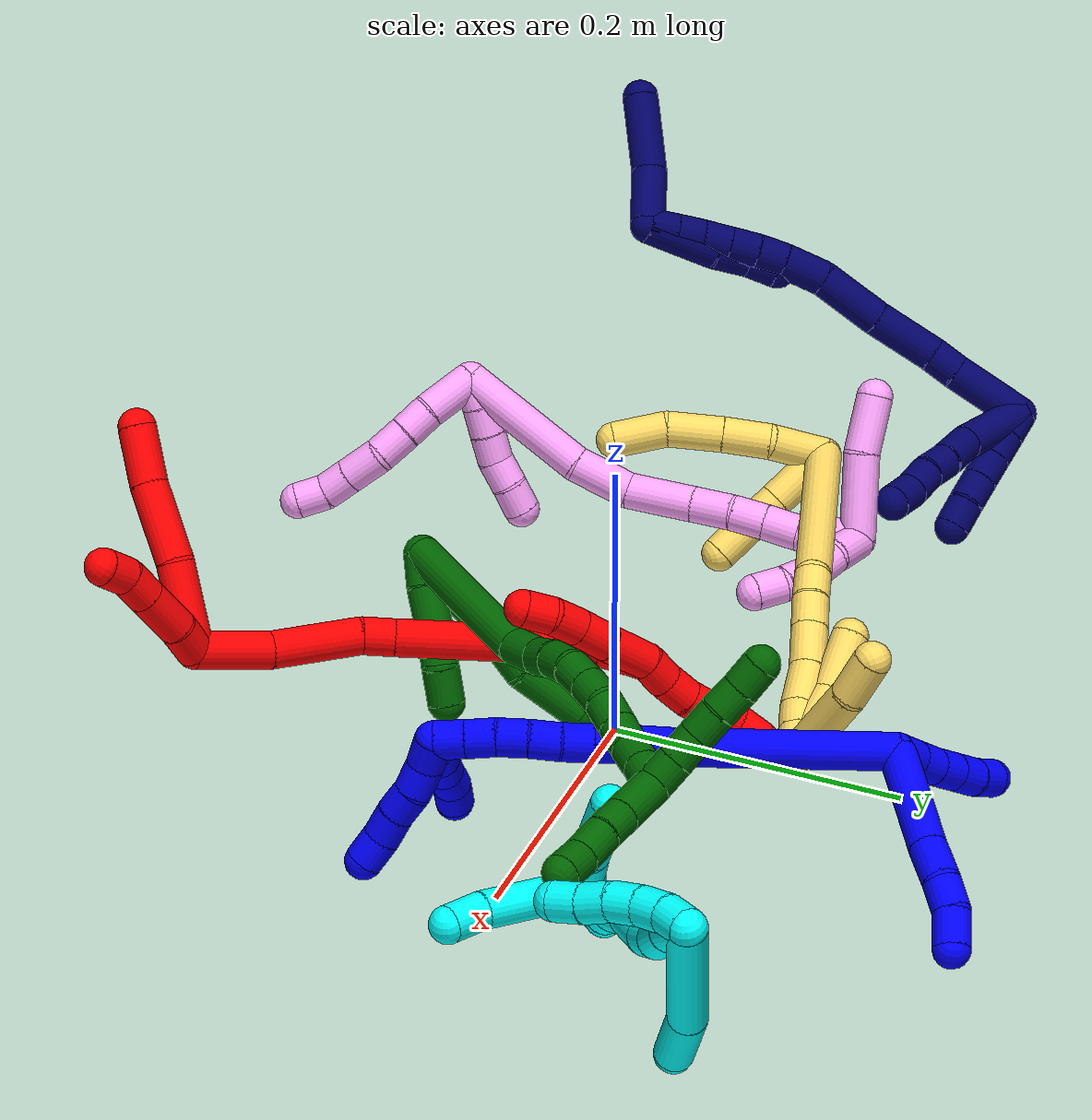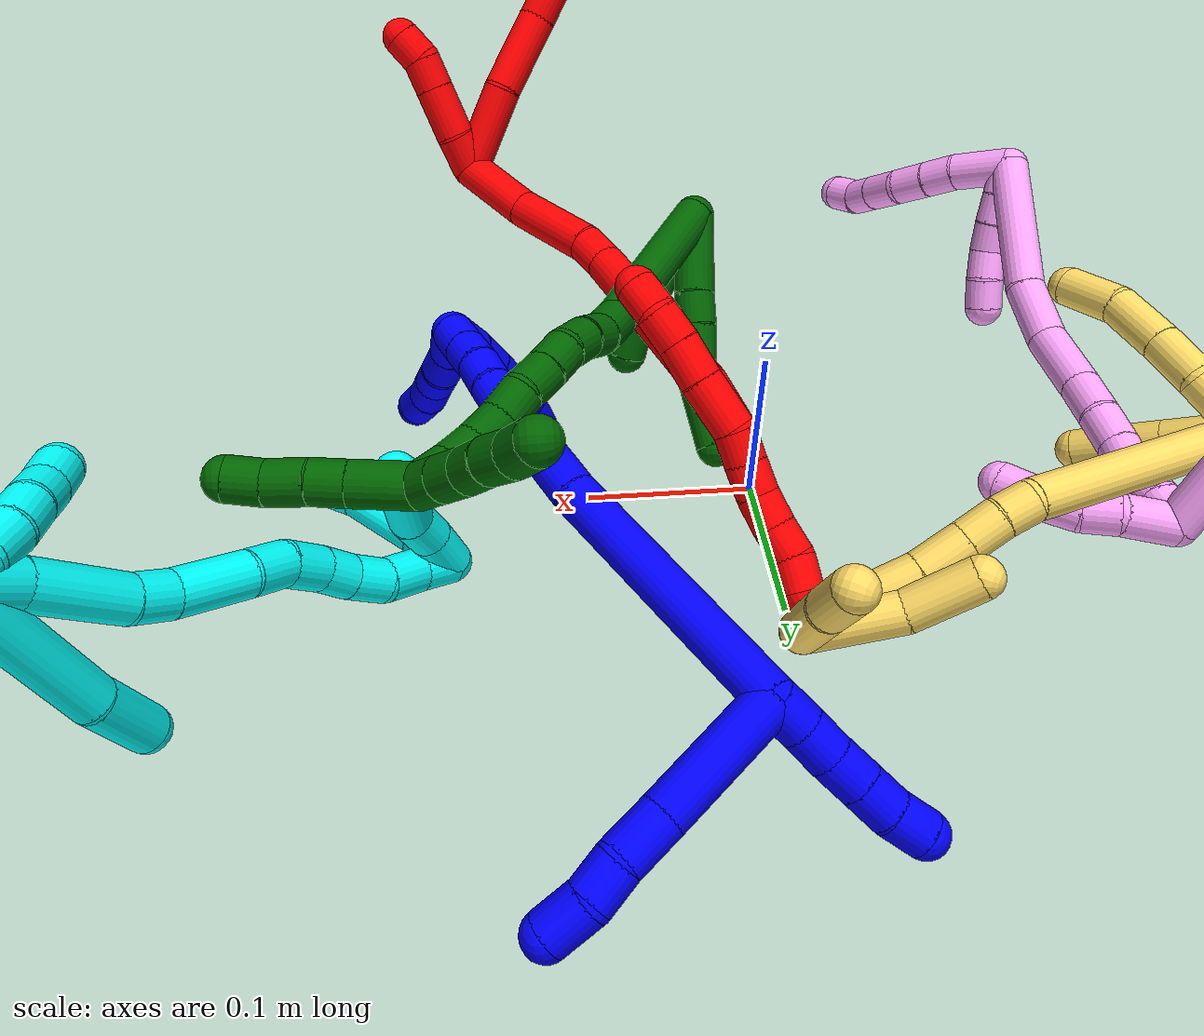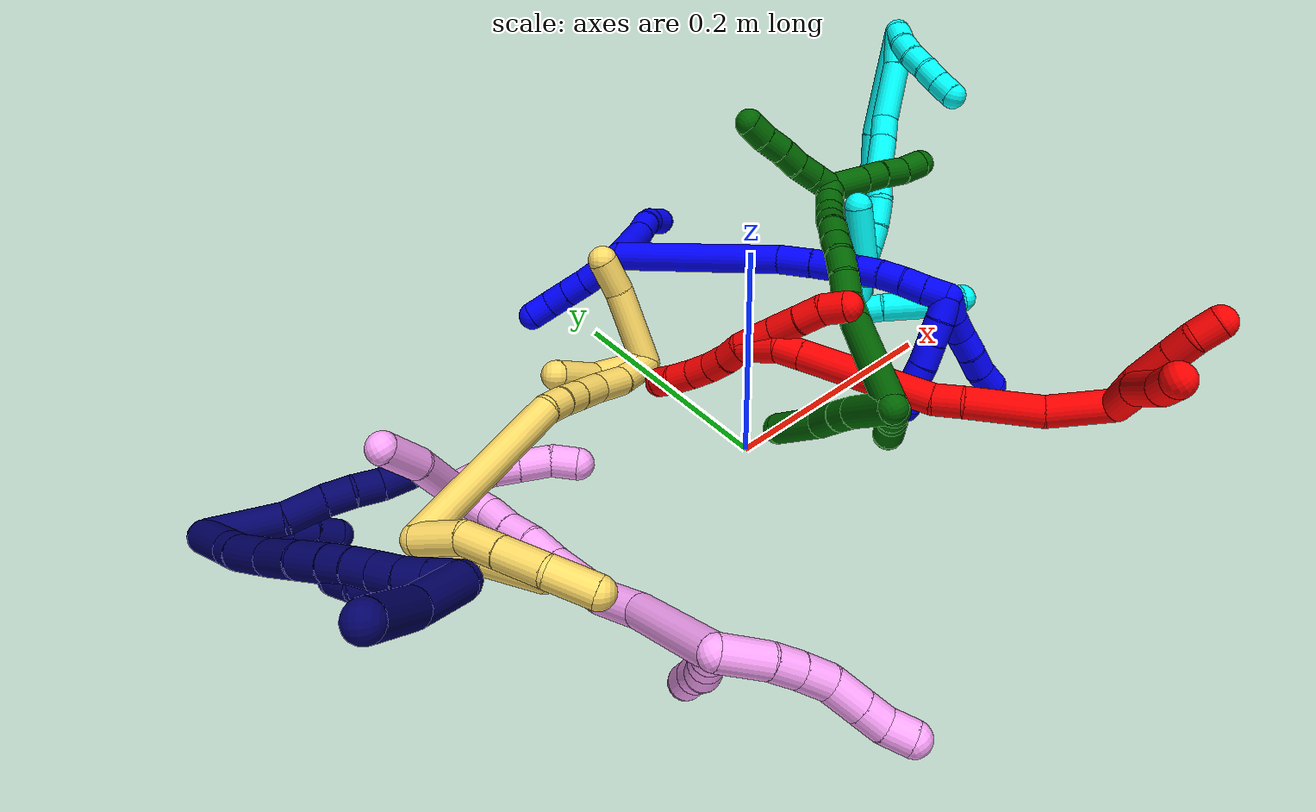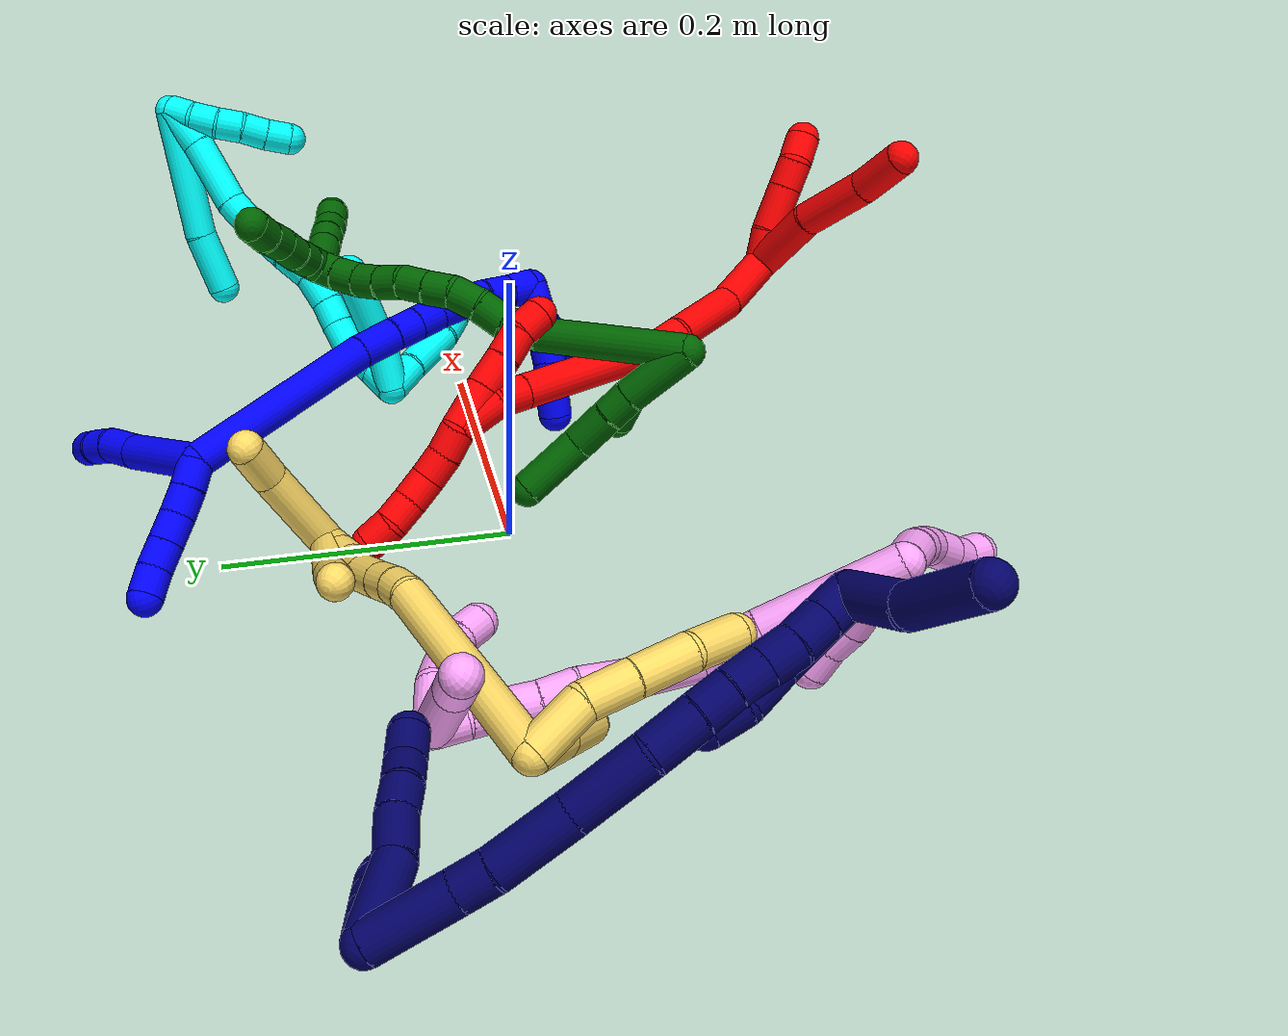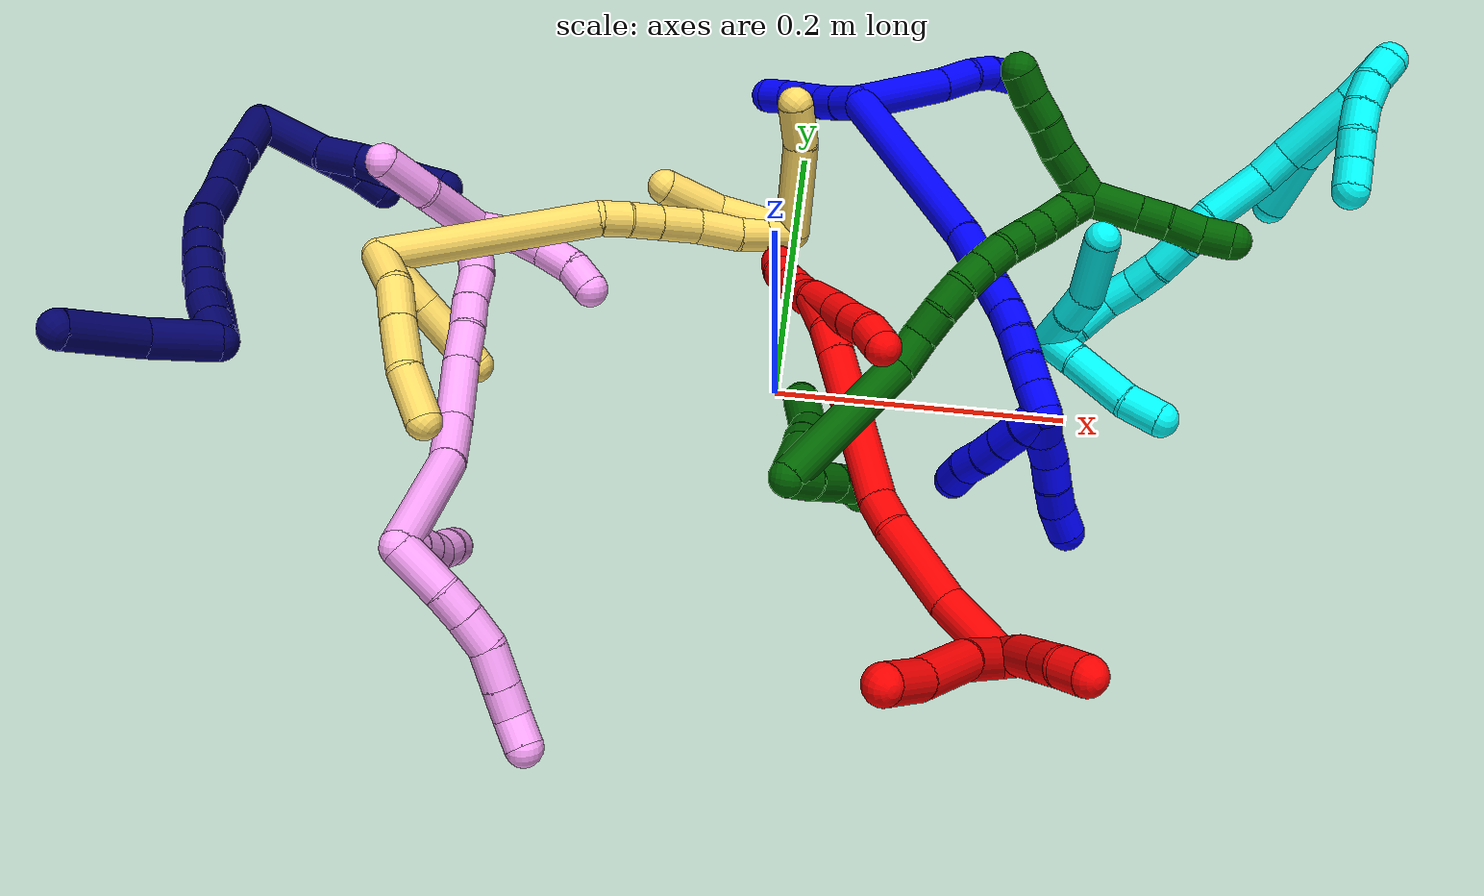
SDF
<sdf version="1.7">
 <world name="default">
  <plugin name="TubeGeneratorPlugin" filename="libtube_generator_plugin.so"/>
  <model name="photoneo_s_sensor">
   <static>1</static>
   <pose>0 0 2 1.57079 1.57079 3.14159</pose>
   <link name="link">
    <inertial><mass>0.1</mass></inertial>
    <sensor name="sensor" type="depth">
     <update_rate>30</update_rate>
     <camera>
      <horizontal_fov>1.22</horizontal_fov>
      <image><width>1920</width><height>1200</height><format>B8G8R8</format></image>
      <clip><near>0.1</near><far>4</far></clip>
      <depth_camera><output>points</output></depth_camera>
     </camera>
     <plugin name="camera_plugin" filename="libgazebo_ros_depth_camera.so">
      <baseline>0.2</baseline>
      <alwaysOn>1</alwaysOn>
      <updateRate>0.0</updateRate>
      <cameraName>camera_ir</cameraName>
      <imageTopicName>/camera/color/image_raw</imageTopicName>
      <cameraInfoTopicName>/camera/color/camera_info</cameraInfoTopicName>
      <depthImageTopicName>/camera/depth/image_raw</depthImageTopicName>
      <depthImageCameraInfoTopicName>/camera/depth/camera_info</depthImageCameraInfoTopicName>
      <pointCloudTopicName>/camera/depth/points</pointCloudTopicName>
      <frameName>fr_optical</frameName>
      <pointCloudCutoff>0.1</pointCloudCutoff>
      <pointCloudCutoffMax>2.0</pointCloudCutoffMax>
      <distortionK1>0</distortionK1>
      <distortionK2>0</distortionK2>
      <distortionK3>0</distortionK3>
      <distortionT1>0</distortionT1>
      <distortionT2>0</distortionT2>
      <CxPrime>0</CxPrime>
      <Cx>0</Cx>
      <Cy>0</Cy>
      <focalLength>0</focalLength>
      <hackBaseline>0</hackBaseline>
     </plugin>
    </sensor>
   </link>
  </model>
  <gravity>0 0 -9.8</gravity>
  <magnetic_field>6e-06 2.3e-05 -4.2e-05</magnetic_field>
  <atmosphere type="adiabatic"/>
  <physics name="default_physics" default="0" type="ode">
   <max_step_size>0.003</max_step_size>
   <real_time_factor>1</real_time_factor>
   <real_time_update_rate>1000</real_time_update_rate>
   <max_contacts>10000</max_contacts>
   <ode>
    <solver>
     <type>quick</type>
     <iters>100</iters>
     <sor>1.3</sor>
     <use_dynamic_moi_rescaling>0</use_dynamic_moi_rescaling>
    </solver>
    <constraints>
     <contact_max_correcting_vel>0</contact_max_correcting_vel>
     <contact_surface_layer>0.001</contact_surface_layer>
     <cfm>0</cfm>
     <erp>0.2</erp>
    </constraints>
   </ode>
  </physics>
  <scene><ambient>0.4 0.4 0.4 1</ambient><background>0.7 0.7 0.7 1</background><shadows>0</shadows></scene>
  <audio><device>default</device></audio>
  <spherical_coordinates>
   <surface_model>EARTH_WGS84</surface_model>
   <latitude_deg>0</latitude_deg>
   <longitude_deg>0</longitude_deg>
   <elevation>0</elevation>
   <heading_deg>0</heading_deg>
  </spherical_coordinates>
  <model name="bin">
   <static>1</static>
   <link name="bottom">
    <collision name="collision-bottom">
     <pose>0 0 -0.01 0 -0 0</pose>
     <geometry><box><size>0.8 0.6 0.02</size></box></geometry>
     <surface>
      <friction><ode><mu>100</mu><mu2>100</mu2></ode></friction>
      <contact><collide_bitmask>65535</collide_bitmask></contact>
     </surface>
    </collision>
   </link>
   <link name="west_wall">
    <collision name="collision-west_wall">
     <pose>-0.41 0 0.1 0 -0 0</pose>
     <geometry><box><size>0.02 0.6 0.2</size></box></geometry>
     <surface>
      <friction><ode><mu>100</mu><mu2>100</mu2></ode></friction>
      <contact><collide_bitmask>65535</collide_bitmask></contact>
     </surface>
    </collision>
   </link>
   <link name="east_wall">
    <collision name="collision-east_wall">
     <pose>0.41 0 0.1 0 -0 0</pose>
     <geometry><box><size>0.02 0.6 0.2</size></box></geometry>
     <surface>
      <friction><ode><mu>100</mu><mu2>100</mu2></ode></friction>
      <contact><collide_bitmask>65535</collide_bitmask></contact>
     </surface>
    </collision>
   </link>
   <link name="south_wall">
    <collision name="collision-south_wall">
     <pose>0 -0.31 0.1 0 -0 0</pose>
     <geometry><box><size>0.8 0.02 0.2</size></box></geometry>
     <surface>
      <friction><ode><mu>100</mu><mu2>100</mu2></ode></friction>
      <contact><collide_bitmask>65535</collide_bitmask></contact>
     </surface>
    </collision>
   </link>
   <link name="north_wall">
    <collision name="collision-north_wall">
     <pose>0 0.31 0.1 0 -0 0</pose>
     <geometry><box><size>0.8 0.02 0.2</size></box></geometry>
     <surface>
      <friction><ode><mu>100</mu><mu2>100</mu2></ode></friction>
      <contact><collide_bitmask>65535</collide_bitmask></contact>
     </surface>
    </collision>
   </link>
  </model>
  <model name="1">
   <static>0</static>
   <link name="1">
    <collision name="collision-cylinder-e_1_2_8">
     <pose>0.028458 0.024304 0.002439 -1.47079 0.861506 -0.787988</pose>
     <geometry><cylinder><radius>0.0125</radius><length>0.075006</length></cylinder></geometry>
     <surface>
      <friction><ode><mu>1.16</mu><mu2>1.16</mu2><slip1>0</slip1><slip2>0</slip2></ode></friction>
      <contact><ode><kp>1e+06</kp><kd>1</kd><max_vel>0</max_vel><min_depth>0.001</min_depth></ode></contact>
     </surface>
    </collision>
    <visual name="visual-cylinder-e_1_2_8">
     <pose>0.028458 0.024304 0.002439 -1.47079 0.861506 -0.787988</pose>
     <geometry><cylinder><radius>0.0125</radius><length>0.075006</length></cylinder></geometry>
     <material><ambient>0 0 1 1</ambient></material>
    </visual>
    <collision name="collision-cylinder-e_2_8_9">
     <pose>0.067397 0.05813 0.007299 -1.32172 0.817628 -0.649778</pose>
     <geometry><cylinder><radius>0.0125</radius><length>0.028733</length></cylinder></geometry>
     <surface>
      <friction><ode><mu>1.16</mu><mu2>1.16</mu2><slip1>0</slip1><slip2>0</slip2></ode></friction>
      <contact><ode><kp>1e+06</kp><kd>1</kd><max_vel>0</max_vel><min_depth>0.001</min_depth></ode></contact>
     </surface>
    </collision>
    <visual name="visual-cylinder-e_2_8_9">
     <pose>0.067397 0.05813 0.007299 -1.32172 0.817628 -0.649778</pose>
     <geometry><cylinder><radius>0.0125</radius><length>0.028733</length></cylinder></geometry>
     <material><ambient>0 0 1 1</ambient></material>
    </visual>
    <collision name="collision-cylinder-e_3_9_10">
     <pose>0.085677 0.074943 0.008899 -1.68322 0.815945 -0.901156</pose>
     <geometry><cylinder><radius>0.0125</radius><length>0.021414</length></cylinder></geometry>
     <surface>
      <friction><ode><mu>1.16</mu><mu2>1.16</mu2><slip1>0</slip1><slip2>0</slip2></ode></friction>
      <contact><ode><kp>1e+06</kp><kd>1</kd><max_vel>0</max_vel><min_depth>0.001</min_depth></ode></contact>
     </surface>
    </collision>
    <visual name="visual-cylinder-e_3_9_10">
     <pose>0.085677 0.074943 0.008899 -1.68322 0.815945 -0.901156</pose>
     <geometry><cylinder><radius>0.0125</radius><length>0.021414</length></cylinder></geometry>
     <material><ambient>0 0 1 1</ambient></material>
    </visual>
    <collision name="collision-cylinder-e_4_10_6">
     <pose>0.104417 0.087758 0.006051 -1.92195 1.07731 -1.41521</pose>
     <geometry><cylinder><radius>0.0125</radius><length>0.024847</length></cylinder></geometry>
     <surface>
      <friction><ode><mu>1.16</mu><mu2>1.16</mu2><slip1>0</slip1><slip2>0</slip2></ode></friction>
      <contact><ode><kp>1e+06</kp><kd>1</kd><max_vel>0</max_vel><min_depth>0.001</min_depth></ode></contact>
     </surface>
    </collision>
    <visual name="visual-cylinder-e_4_10_6">
     <pose>0.104417 0.087758 0.006051 -1.92195 1.07731 -1.41521</pose>
     <geometry><cylinder><radius>0.0125</radius><length>0.024847</length></cylinder></geometry>
     <material><ambient>0 0 1 1</ambient></material>
    </visual>
    <collision name="collision-cylinder-e_1_2_11">
     <pose>-0.004842 0.004885 -0.007259 -2.54933 -0.505404 1.40473</pose>
     <geometry><cylinder><radius>0.0125</radius><length>0.02</length></cylinder></geometry>
     <surface>
      <friction><ode><mu>1.16</mu><mu2>1.16</mu2><slip1>0</slip1><slip2>0</slip2></ode></friction>
      <contact><ode><kp>1e+06</kp><kd>1</kd><max_vel>0</max_vel><min_depth>0.001</min_depth></ode></contact>
     </surface>
    </collision>
    <visual name="visual-cylinder-e_1_2_11">
     <pose>-0.004842 0.004885 -0.007259 -2.54933 -0.505404 1.40473</pose>
     <geometry><cylinder><radius>0.0125</radius><length>0.02</length></cylinder></geometry>
     <material><ambient>0 0 1 1</ambient></material>
    </visual>
    <collision name="collision-cylinder-e_2_11_12">
     <pose>-0.014441 0.015301 -0.021357 -2.46135 -0.495861 1.24188</pose>
     <geometry><cylinder><radius>0.0125</radius><length>0.02</length></cylinder></geometry>
     <surface>
      <friction><ode><mu>1.16</mu><mu2>1.16</mu2><slip1>0</slip1><slip2>0</slip2></ode></friction>
      <contact><ode><kp>1e+06</kp><kd>1</kd><max_vel>0</max_vel><min_depth>0.001</min_depth></ode></contact>
     </surface>
    </collision>
    <visual name="visual-cylinder-e_2_11_12">
     <pose>-0.014441 0.015301 -0.021357 -2.46135 -0.495861 1.24188</pose>
     <geometry><cylinder><radius>0.0125</radius><length>0.02</length></cylinder></geometry>
     <material><ambient>0 0 1 1</ambient></material>
    </visual>
    <collision name="collision-cylinder-e_3_12_13">
     <pose>-0.024557 0.026415 -0.034531 -2.41946 -0.565481 1.31155</pose>
     <geometry><cylinder><radius>0.0125</radius><length>0.02</length></cylinder></geometry>
     <surface>
      <friction><ode><mu>1.16</mu><mu2>1.16</mu2><slip1>0</slip1><slip2>0</slip2></ode></friction>
      <contact><ode><kp>1e+06</kp><kd>1</kd><max_vel>0</max_vel><min_depth>0.001</min_depth></ode></contact>
     </surface>
    </collision>
    <visual name="visual-cylinder-e_3_12_13">
     <pose>-0.024557 0.026415 -0.034531 -2.41946 -0.565481 1.31155</pose>
     <geometry><cylinder><radius>0.0125</radius><length>0.02</length></cylinder></geometry>
     <material><ambient>0 0 1 1</ambient></material>
    </visual>
    <collision name="collision-cylinder-e_4_13_14">
     <pose>-0.035217 0.037587 -0.047241 -2.42149 -0.558747 1.30231</pose>
     <geometry><cylinder><radius>0.0125</radius><length>0.02</length></cylinder></geometry>
     <surface>
      <friction><ode><mu>1.16</mu><mu2>1.16</mu2><slip1>0</slip1><slip2>0</slip2></ode></friction>
      <contact><ode><kp>1e+06</kp><kd>1</kd><max_vel>0</max_vel><min_depth>0.001</min_depth></ode></contact>
     </surface>
    </collision>
    <visual name="visual-cylinder-e_4_13_14">
     <pose>-0.035217 0.037587 -0.047241 -2.42149 -0.558747 1.30231</pose>
     <geometry><cylinder><radius>0.0125</radius><length>0.02</length></cylinder></geometry>
     <material><ambient>0 0 1 1</ambient></material>
    </visual>
    <collision name="collision-cylinder-e_5_14_5">
     <pose>-0.046979 0.047557 -0.059866 -2.53062 -0.70247 1.72033</pose>
     <geometry><cylinder><radius>0.0125</radius><length>0.02</length></cylinder></geometry>
     <surface>
      <friction><ode><mu>1.16</mu><mu2>1.16</mu2><slip1>0</slip1><slip2>0</slip2></ode></friction>
      <contact><ode><kp>1e+06</kp><kd>1</kd><max_vel>0</max_vel><min_depth>0.001</min_depth></ode></contact>
     </surface>
    </collision>
    <visual name="visual-cylinder-e_5_14_5">
     <pose>-0.046979 0.047557 -0.059866 -2.53062 -0.70247 1.72033</pose>
     <geometry><cylinder><radius>0.0125</radius><length>0.02</length></cylinder></geometry>
     <material><ambient>0 0 1 1</ambient></material>
    </visual>
    <collision name="collision-cylinder-e_1_2_15">
     <pose>0.041423 -0.060941 0.011304 1.38739 0.58915 0.494284</pose>
     <geometry><cylinder><radius>0.0125</radius><length>0.149096</length></cylinder></geometry>
     <surface>
      <friction><ode><mu>1.16</mu><mu2>1.16</mu2><slip1>0</slip1><slip2>0</slip2></ode></friction>
      <contact><ode><kp>1e+06</kp><kd>1</kd><max_vel>0</max_vel><min_depth>0.001</min_depth></ode></contact>
     </surface>
    </collision>
    <visual name="visual-cylinder-e_1_2_15">
     <pose>0.041423 -0.060941 0.011304 1.38739 0.58915 0.494284</pose>
     <geometry><cylinder><radius>0.0125</radius><length>0.149096</length></cylinder></geometry>
     <material><ambient>0 0 1 1</ambient></material>
    </visual>
    <collision name="collision-cylinder-e_2_15_16">
     <pose>0.089953 -0.134908 0.023692 1.48777 0.497966 0.459687</pose>
     <geometry><cylinder><radius>0.0125</radius><length>0.029757</length></cylinder></geometry>
     <surface>
      <friction><ode><mu>1.16</mu><mu2>1.16</mu2><slip1>0</slip1><slip2>0</slip2></ode></friction>
      <contact><ode><kp>1e+06</kp><kd>1</kd><max_vel>0</max_vel><min_depth>0.001</min_depth></ode></contact>
     </surface>
    </collision>
    <visual name="visual-cylinder-e_2_15_16">
     <pose>0.089953 -0.134908 0.023692 1.48777 0.497966 0.459687</pose>
     <geometry><cylinder><radius>0.0125</radius><length>0.029757</length></cylinder></geometry>
     <material><ambient>0 0 1 1</ambient></material>
    </visual>
    <collision name="collision-cylinder-e_3_16_17">
     <pose>0.10217 -0.15677 0.025221 1.52041 0.523887 0.499214</pose>
     <geometry><cylinder><radius>0.0125</radius><length>0.020432</length></cylinder></geometry>
     <surface>
      <friction><ode><mu>1.16</mu><mu2>1.16</mu2><slip1>0</slip1><slip2>0</slip2></ode></friction>
      <contact><ode><kp>1e+06</kp><kd>1</kd><max_vel>0</max_vel><min_depth>0.001</min_depth></ode></contact>
     </surface>
    </collision>
    <visual name="visual-cylinder-e_3_16_17">
     <pose>0.10217 -0.15677 0.025221 1.52041 0.523887 0.499214</pose>
     <geometry><cylinder><radius>0.0125</radius><length>0.020432</length></cylinder></geometry>
     <material><ambient>0 0 1 1</ambient></material>
    </visual>
    <collision name="collision-cylinder-e_4_17_18">
     <pose>0.112296 -0.174375 0.026272 1.50189 0.518498 0.485331</pose>
     <geometry><cylinder><radius>0.0125</radius><length>0.020244</length></cylinder></geometry>
     <surface>
      <friction><ode><mu>1.16</mu><mu2>1.16</mu2><slip1>0</slip1><slip2>0</slip2></ode></friction>
      <contact><ode><kp>1e+06</kp><kd>1</kd><max_vel>0</max_vel><min_depth>0.001</min_depth></ode></contact>
     </surface>
    </collision>
    <visual name="visual-cylinder-e_4_17_18">
     <pose>0.112296 -0.174375 0.026272 1.50189 0.518498 0.485331</pose>
     <geometry><cylinder><radius>0.0125</radius><length>0.020244</length></cylinder></geometry>
     <material><ambient>0 0 1 1</ambient></material>
    </visual>
    <collision name="collision-cylinder-e_5_18_19">
     <pose>0.121441 -0.192415 0.027072 1.54985 0.41888 0.41044</pose>
     <geometry><cylinder><radius>0.0125</radius><length>0.020299</length></cylinder></geometry>
     <surface>
      <friction><ode><mu>1.16</mu><mu2>1.16</mu2><slip1>0</slip1><slip2>0</slip2></ode></friction>
      <contact><ode><kp>1e+06</kp><kd>1</kd><max_vel>0</max_vel><min_depth>0.001</min_depth></ode></contact>
     </surface>
    </collision>
    <visual name="visual-cylinder-e_5_18_19">
     <pose>0.121441 -0.192415 0.027072 1.54985 0.41888 0.41044</pose>
     <geometry><cylinder><radius>0.0125</radius><length>0.020299</length></cylinder></geometry>
     <material><ambient>0 0 1 1</ambient></material>
    </visual>
    <collision name="collision-cylinder-e_6_19_20">
     <pose>0.129607 -0.21087 0.026366 1.66853 0.412491 0.453535</pose>
     <geometry><cylinder><radius>0.0125</radius><length>0.020147</length></cylinder></geometry>
     <surface>
      <friction><ode><mu>1.16</mu><mu2>1.16</mu2><slip1>0</slip1><slip2>0</slip2></ode></friction>
      <contact><ode><kp>1e+06</kp><kd>1</kd><max_vel>0</max_vel><min_depth>0.001</min_depth></ode></contact>
     </surface>
    </collision>
    <visual name="visual-cylinder-e_6_19_20">
     <pose>0.129607 -0.21087 0.026366 1.66853 0.412491 0.453535</pose>
     <geometry><cylinder><radius>0.0125</radius><length>0.020147</length></cylinder></geometry>
     <material><ambient>0 0 1 1</ambient></material>
    </visual>
    <collision name="collision-cylinder-e_7_20_21">
     <pose>0.1383 -0.228734 0.023683 1.77326 0.483682 0.587401</pose>
     <geometry><cylinder><radius>0.0125</radius><length>0.020018</length></cylinder></geometry>
     <surface>
      <friction><ode><mu>1.16</mu><mu2>1.16</mu2><slip1>0</slip1><slip2>0</slip2></ode></friction>
      <contact><ode><kp>1e+06</kp><kd>1</kd><max_vel>0</max_vel><min_depth>0.001</min_depth></ode></contact>
     </surface>
    </collision>
    <visual name="visual-cylinder-e_7_20_21">
     <pose>0.1383 -0.228734 0.023683 1.77326 0.483682 0.587401</pose>
     <geometry><cylinder><radius>0.0125</radius><length>0.020018</length></cylinder></geometry>
     <material><ambient>0 0 1 1</ambient></material>
    </visual>
    <collision name="collision-cylinder-e_8_21_1">
     <pose>0.147543 -0.246217 0.020665 1.71034 0.47649 0.544815</pose>
     <geometry><cylinder><radius>0.0125</radius><length>0.020007</length></cylinder></geometry>
     <surface>
      <friction><ode><mu>1.16</mu><mu2>1.16</mu2><slip1>0</slip1><slip2>0</slip2></ode></friction>
      <contact><ode><kp>1e+06</kp><kd>1</kd><max_vel>0</max_vel><min_depth>0.001</min_depth></ode></contact>
     </surface>
    </collision>
    <visual name="visual-cylinder-e_8_21_1">
     <pose>0.147543 -0.246217 0.020665 1.71034 0.47649 0.544815</pose>
     <geometry><cylinder><radius>0.0125</radius><length>0.020007</length></cylinder></geometry>
     <material><ambient>0 0 1 1</ambient></material>
    </visual>
    <collision name="collision-cylinder-e_1_1_22">
     <pose>0.148992 -0.255071 0.009934 3.13623 -0.319368 -3.10829</pose>
     <geometry><cylinder><radius>0.0125</radius><length>0.02</length></cylinder></geometry>
     <surface>
      <friction><ode><mu>1.16</mu><mu2>1.16</mu2><slip1>0</slip1><slip2>0</slip2></ode></friction>
      <contact><ode><kp>1e+06</kp><kd>1</kd><max_vel>0</max_vel><min_depth>0.001</min_depth></ode></contact>
     </surface>
    </collision>
    <visual name="visual-cylinder-e_1_1_22">
     <pose>0.148992 -0.255071 0.009934 3.13623 -0.319368 -3.10829</pose>
     <geometry><cylinder><radius>0.0125</radius><length>0.02</length></cylinder></geometry>
     <material><ambient>0 0 1 1</ambient></material>
    </visual>
    <collision name="collision-cylinder-e_2_22_23">
     <pose>0.14347 -0.254562 -0.009256 -3.08399 -0.240563 2.67358</pose>
     <geometry><cylinder><radius>0.0125</radius><length>0.02</length></cylinder></geometry>
     <surface>
      <friction><ode><mu>1.16</mu><mu2>1.16</mu2><slip1>0</slip1><slip2>0</slip2></ode></friction>
      <contact><ode><kp>1e+06</kp><kd>1</kd><max_vel>0</max_vel><min_depth>0.001</min_depth></ode></contact>
     </surface>
    </collision>
    <visual name="visual-cylinder-e_2_22_23">
     <pose>0.14347 -0.254562 -0.009256 -3.08399 -0.240563 2.67358</pose>
     <geometry><cylinder><radius>0.0125</radius><length>0.02</length></cylinder></geometry>
     <material><ambient>0 0 1 1</ambient></material>
    </visual>
    <collision name="collision-cylinder-e_3_23_24">
     <pose>0.139015 -0.253176 -0.0287 -3.05695 -0.208754 2.37332</pose>
     <geometry><cylinder><radius>0.0125</radius><length>0.02</length></cylinder></geometry>
     <surface>
      <friction><ode><mu>1.16</mu><mu2>1.16</mu2><slip1>0</slip1><slip2>0</slip2></ode></friction>
      <contact><ode><kp>1e+06</kp><kd>1</kd><max_vel>0</max_vel><min_depth>0.001</min_depth></ode></contact>
     </surface>
    </collision>
    <visual name="visual-cylinder-e_3_23_24">
     <pose>0.139015 -0.253176 -0.0287 -3.05695 -0.208754 2.37332</pose>
     <geometry><cylinder><radius>0.0125</radius><length>0.02</length></cylinder></geometry>
     <material><ambient>0 0 1 1</ambient></material>
    </visual>
    <collision name="collision-cylinder-e_4_24_25">
     <pose>0.134628 -0.250331 -0.047964 -2.9326 -0.23358 1.68269</pose>
     <geometry><cylinder><radius>0.0125</radius><length>0.02</length></cylinder></geometry>
     <surface>
      <friction><ode><mu>1.16</mu><mu2>1.16</mu2><slip1>0</slip1><slip2>0</slip2></ode></friction>
      <contact><ode><kp>1e+06</kp><kd>1</kd><max_vel>0</max_vel><min_depth>0.001</min_depth></ode></contact>
     </surface>
    </collision>
    <visual name="visual-cylinder-e_4_24_25">
     <pose>0.134628 -0.250331 -0.047964 -2.9326 -0.23358 1.68269</pose>
     <geometry><cylinder><radius>0.0125</radius><length>0.02</length></cylinder></geometry>
     <material><ambient>0 0 1 1</ambient></material>
    </visual>
    <collision name="collision-cylinder-e_5_25_4">
     <pose>0.131906 -0.246846 -0.067364 -2.99431 -0.040746 0.538925</pose>
     <geometry><cylinder><radius>0.0125</radius><length>0.02</length></cylinder></geometry>
     <surface>
      <friction><ode><mu>1.16</mu><mu2>1.16</mu2><slip1>0</slip1><slip2>0</slip2></ode></friction>
      <contact><ode><kp>1e+06</kp><kd>1</kd><max_vel>0</max_vel><min_depth>0.001</min_depth></ode></contact>
     </surface>
    </collision>
    <visual name="visual-cylinder-e_5_25_4">
     <pose>0.131906 -0.246846 -0.067364 -2.99431 -0.040746 0.538925</pose>
     <geometry><cylinder><radius>0.0125</radius><length>0.02</length></cylinder></geometry>
     <material><ambient>0 0 1 1</ambient></material>
    </visual>
    <collision name="collision-cylinder-e_1_1_26">
     <pose>0.156499 -0.255158 0.010434 3.12622 0.452001 3.07475</pose>
     <geometry><cylinder><radius>0.0125</radius><length>0.02</length></cylinder></geometry>
     <surface>
      <friction><ode><mu>1.16</mu><mu2>1.16</mu2><slip1>0</slip1><slip2>0</slip2></ode></friction>
      <contact><ode><kp>1e+06</kp><kd>1</kd><max_vel>0</max_vel><min_depth>0.001</min_depth></ode></contact>
     </surface>
    </collision>
    <visual name="visual-cylinder-e_1_1_26">
     <pose>0.156499 -0.255158 0.010434 3.12622 0.452001 3.07475</pose>
     <geometry><cylinder><radius>0.0125</radius><length>0.02</length></cylinder></geometry>
     <material><ambient>0 0 1 1</ambient></material>
    </visual>
    <collision name="collision-cylinder-e_2_26_27">
     <pose>0.166991 -0.255999 -0.006435 3.05256 0.659137 2.88259</pose>
     <geometry><cylinder><radius>0.0125</radius><length>0.02</length></cylinder></geometry>
     <surface>
      <friction><ode><mu>1.16</mu><mu2>1.16</mu2><slip1>0</slip1><slip2>0</slip2></ode></friction>
      <contact><ode><kp>1e+06</kp><kd>1</kd><max_vel>0</max_vel><min_depth>0.001</min_depth></ode></contact>
     </surface>
    </collision>
    <visual name="visual-cylinder-e_2_26_27">
     <pose>0.166991 -0.255999 -0.006435 3.05256 0.659137 2.88259</pose>
     <geometry><cylinder><radius>0.0125</radius><length>0.02</length></cylinder></geometry>
     <material><ambient>0 0 1 1</ambient></material>
    </visual>
    <collision name="collision-cylinder-e_3_27_28">
     <pose>0.178471 -0.259549 -0.022259 2.79773 0.56523 2.06374</pose>
     <geometry><cylinder><radius>0.0125</radius><length>0.02</length></cylinder></geometry>
     <surface>
      <friction><ode><mu>1.16</mu><mu2>1.16</mu2><slip1>0</slip1><slip2>0</slip2></ode></friction>
      <contact><ode><kp>1e+06</kp><kd>1</kd><max_vel>0</max_vel><min_depth>0.001</min_depth></ode></contact>
     </surface>
    </collision>
    <visual name="visual-cylinder-e_3_27_28">
     <pose>0.178471 -0.259549 -0.022259 2.79773 0.56523 2.06374</pose>
     <geometry><cylinder><radius>0.0125</radius><length>0.02</length></cylinder></geometry>
     <material><ambient>0 0 1 1</ambient></material>
    </visual>
    <collision name="collision-cylinder-e_4_28_29">
     <pose>0.189469 -0.264049 -0.038299 2.94004 0.599402 2.50908</pose>
     <geometry><cylinder><radius>0.0125</radius><length>0.02</length></cylinder></geometry>
     <surface>
      <friction><ode><mu>1.16</mu><mu2>1.16</mu2><slip1>0</slip1><slip2>0</slip2></ode></friction>
      <contact><ode><kp>1e+06</kp><kd>1</kd><max_vel>0</max_vel><min_depth>0.001</min_depth></ode></contact>
     </surface>
    </collision>
    <visual name="visual-cylinder-e_4_28_29">
     <pose>0.189469 -0.264049 -0.038299 2.94004 0.599402 2.50908</pose>
     <geometry><cylinder><radius>0.0125</radius><length>0.02</length></cylinder></geometry>
     <material><ambient>0 0 1 1</ambient></material>
    </visual>
    <collision name="collision-cylinder-e_5_29_3">
     <pose>0.202034 -0.268089 -0.053198 2.80445 0.764738 2.34094</pose>
     <geometry><cylinder><radius>0.0125</radius><length>0.02</length></cylinder></geometry>
     <surface>
      <friction><ode><mu>1.16</mu><mu2>1.16</mu2><slip1>0</slip1><slip2>0</slip2></ode></friction>
      <contact><ode><kp>1e+06</kp><kd>1</kd><max_vel>0</max_vel><min_depth>0.001</min_depth></ode></contact>
     </surface>
    </collision>
    <visual name="visual-cylinder-e_5_29_3">
     <pose>0.202034 -0.268089 -0.053198 2.80445 0.764738 2.34094</pose>
     <geometry><cylinder><radius>0.0125</radius><length>0.02</length></cylinder></geometry>
     <material><ambient>0 0 1 1</ambient></material>
    </visual>
    <collision name="collision-sphere-3">
     <pose>0.208958 -0.270475 -0.060007 0 -0 0</pose>
     <geometry><sphere><radius>0.0125</radius></sphere></geometry>
     <surface>
      <friction><ode><mu>1.16</mu><mu2>1.16</mu2><slip1>0</slip1><slip2>0</slip2></ode></friction>
      <contact><ode><kp>1e+06</kp><kd>1</kd><max_vel>0</max_vel><min_depth>0.001</min_depth></ode></contact>
     </surface>
    </collision>
    <visual name="visual-sphere-3">
     <pose>0.208958 -0.270475 -0.060007 0 -0 0</pose>
     <geometry><sphere><radius>0.0125</radius></sphere></geometry>
     <material><ambient>0 0 1 1</ambient></material>
    </visual>
    <collision name="collision-sphere-29">
     <pose>0.195111 -0.265702 -0.046388 0 -0 0</pose>
     <geometry><sphere><radius>0.0125</radius></sphere></geometry>
     <surface>
      <friction><ode><mu>1.16</mu><mu2>1.16</mu2><slip1>0</slip1><slip2>0</slip2></ode></friction>
      <contact><ode><kp>1e+06</kp><kd>1</kd><max_vel>0</max_vel><min_depth>0.001</min_depth></ode></contact>
     </surface>
    </collision>
    <visual name="visual-sphere-29">
     <pose>0.195111 -0.265702 -0.046388 0 -0 0</pose>
     <geometry><sphere><radius>0.0125</radius></sphere></geometry>
     <material><ambient>0 0 1 1</ambient></material>
    </visual>
    <collision name="collision-sphere-28">
     <pose>0.183828 -0.262396 -0.030209 0 -0 0</pose>
     <geometry><sphere><radius>0.0125</radius></sphere></geometry>
     <surface>
      <friction><ode><mu>1.16</mu><mu2>1.16</mu2><slip1>0</slip1><slip2>0</slip2></ode></friction>
      <contact><ode><kp>1e+06</kp><kd>1</kd><max_vel>0</max_vel><min_depth>0.001</min_depth></ode></contact>
     </surface>
    </collision>
    <visual name="visual-sphere-28">
     <pose>0.183828 -0.262396 -0.030209 0 -0 0</pose>
     <geometry><sphere><radius>0.0125</radius></sphere></geometry>
     <material><ambient>0 0 1 1</ambient></material>
    </visual>
    <collision name="collision-sphere-27">
     <pose>0.173115 -0.256702 -0.014309 0 -0 0</pose>
     <geometry><sphere><radius>0.0125</radius></sphere></geometry>
     <surface>
      <friction><ode><mu>1.16</mu><mu2>1.16</mu2><slip1>0</slip1><slip2>0</slip2></ode></friction>
      <contact><ode><kp>1e+06</kp><kd>1</kd><max_vel>0</max_vel><min_depth>0.001</min_depth></ode></contact>
     </surface>
    </collision>
    <visual name="visual-sphere-27">
     <pose>0.173115 -0.256702 -0.014309 0 -0 0</pose>
     <geometry><sphere><radius>0.0125</radius></sphere></geometry>
     <material><ambient>0 0 1 1</ambient></material>
    </visual>
    <collision name="collision-sphere-26">
     <pose>0.160867 -0.255296 0.001439 0 -0 0</pose>
     <geometry><sphere><radius>0.0125</radius></sphere></geometry>
     <surface>
      <friction><ode><mu>1.16</mu><mu2>1.16</mu2><slip1>0</slip1><slip2>0</slip2></ode></friction>
      <contact><ode><kp>1e+06</kp><kd>1</kd><max_vel>0</max_vel><min_depth>0.001</min_depth></ode></contact>
     </surface>
    </collision>
    <visual name="visual-sphere-26">
     <pose>0.160867 -0.255296 0.001439 0 -0 0</pose>
     <geometry><sphere><radius>0.0125</radius></sphere></geometry>
     <material><ambient>0 0 1 1</ambient></material>
    </visual>
    <collision name="collision-sphere-4">
     <pose>0.131498 -0.24538 -0.077248 0 -0 0</pose>
     <geometry><sphere><radius>0.0125</radius></sphere></geometry>
     <surface>
      <friction><ode><mu>1.16</mu><mu2>1.16</mu2><slip1>0</slip1><slip2>0</slip2></ode></friction>
      <contact><ode><kp>1e+06</kp><kd>1</kd><max_vel>0</max_vel><min_depth>0.001</min_depth></ode></contact>
     </surface>
    </collision>
    <visual name="visual-sphere-4">
     <pose>0.131498 -0.24538 -0.077248 0 -0 0</pose>
     <geometry><sphere><radius>0.0125</radius></sphere></geometry>
     <material><ambient>0 0 1 1</ambient></material>
    </visual>
    <collision name="collision-sphere-25">
     <pose>0.132313 -0.248312 -0.057481 0 -0 0</pose>
     <geometry><sphere><radius>0.0125</radius></sphere></geometry>
     <surface>
      <friction><ode><mu>1.16</mu><mu2>1.16</mu2><slip1>0</slip1><slip2>0</slip2></ode></friction>
      <contact><ode><kp>1e+06</kp><kd>1</kd><max_vel>0</max_vel><min_depth>0.001</min_depth></ode></contact>
     </surface>
    </collision>
    <visual name="visual-sphere-25">
     <pose>0.132313 -0.248312 -0.057481 0 -0 0</pose>
     <geometry><sphere><radius>0.0125</radius></sphere></geometry>
     <material><ambient>0 0 1 1</ambient></material>
    </visual>
    <collision name="collision-sphere-24">
     <pose>0.136942 -0.252349 -0.038447 0 -0 0</pose>
     <geometry><sphere><radius>0.0125</radius></sphere></geometry>
     <surface>
      <friction><ode><mu>1.16</mu><mu2>1.16</mu2><slip1>0</slip1><slip2>0</slip2></ode></friction>
      <contact><ode><kp>1e+06</kp><kd>1</kd><max_vel>0</max_vel><min_depth>0.001</min_depth></ode></contact>
     </surface>
    </collision>
    <visual name="visual-sphere-24">
     <pose>0.136942 -0.252349 -0.038447 0 -0 0</pose>
     <geometry><sphere><radius>0.0125</radius></sphere></geometry>
     <material><ambient>0 0 1 1</ambient></material>
    </visual>
    <collision name="collision-sphere-23">
     <pose>0.141087 -0.254003 -0.018952 0 -0 0</pose>
     <geometry><sphere><radius>0.0125</radius></sphere></geometry>
     <surface>
      <friction><ode><mu>1.16</mu><mu2>1.16</mu2><slip1>0</slip1><slip2>0</slip2></ode></friction>
      <contact><ode><kp>1e+06</kp><kd>1</kd><max_vel>0</max_vel><min_depth>0.001</min_depth></ode></contact>
     </surface>
    </collision>
    <visual name="visual-sphere-23">
     <pose>0.141087 -0.254003 -0.018952 0 -0 0</pose>
     <geometry><sphere><radius>0.0125</radius></sphere></geometry>
     <material><ambient>0 0 1 1</ambient></material>
    </visual>
    <collision name="collision-sphere-22">
     <pose>0.145852 -0.255121 0.00044 0 -0 0</pose>
     <geometry><sphere><radius>0.0125</radius></sphere></geometry>
     <surface>
      <friction><ode><mu>1.16</mu><mu2>1.16</mu2><slip1>0</slip1><slip2>0</slip2></ode></friction>
      <contact><ode><kp>1e+06</kp><kd>1</kd><max_vel>0</max_vel><min_depth>0.001</min_depth></ode></contact>
     </surface>
    </collision>
    <visual name="visual-sphere-22">
     <pose>0.145852 -0.255121 0.00044 0 -0 0</pose>
     <geometry><sphere><radius>0.0125</radius></sphere></geometry>
     <material><ambient>0 0 1 1</ambient></material>
    </visual>
    <collision name="collision-sphere-1">
     <pose>0.152131 -0.25502 0.019429 0 -0 0</pose>
     <geometry><sphere><radius>0.0125</radius></sphere></geometry>
     <surface>
      <friction><ode><mu>1.16</mu><mu2>1.16</mu2><slip1>0</slip1><slip2>0</slip2></ode></friction>
      <contact><ode><kp>1e+06</kp><kd>1</kd><max_vel>0</max_vel><min_depth>0.001</min_depth></ode></contact>
     </surface>
    </collision>
    <visual name="visual-sphere-1">
     <pose>0.152131 -0.25502 0.019429 0 -0 0</pose>
     <geometry><sphere><radius>0.0125</radius></sphere></geometry>
     <material><ambient>0 0 1 1</ambient></material>
    </visual>
    <collision name="collision-sphere-21">
     <pose>0.142955 -0.237414 0.021901 0 -0 0</pose>
     <geometry><sphere><radius>0.0125</radius></sphere></geometry>
     <surface>
      <friction><ode><mu>1.16</mu><mu2>1.16</mu2><slip1>0</slip1><slip2>0</slip2></ode></friction>
      <contact><ode><kp>1e+06</kp><kd>1</kd><max_vel>0</max_vel><min_depth>0.001</min_depth></ode></contact>
     </surface>
    </collision>
    <visual name="visual-sphere-21">
     <pose>0.142955 -0.237414 0.021901 0 -0 0</pose>
     <geometry><sphere><radius>0.0125</radius></sphere></geometry>
     <material><ambient>0 0 1 1</ambient></material>
    </visual>
    <collision name="collision-sphere-11">
     <pose>-0.009683 0.009769 -0.014519 0 -0 0</pose>
     <geometry><sphere><radius>0.0125</radius></sphere></geometry>
     <surface>
      <friction><ode><mu>1.16</mu><mu2>1.16</mu2><slip1>0</slip1><slip2>0</slip2></ode></friction>
      <contact><ode><kp>1e+06</kp><kd>1</kd><max_vel>0</max_vel><min_depth>0.001</min_depth></ode></contact>
     </surface>
    </collision>
    <visual name="visual-sphere-11">
     <pose>-0.009683 0.009769 -0.014519 0 -0 0</pose>
     <geometry><sphere><radius>0.0125</radius></sphere></geometry>
     <material><ambient>0 0 1 1</ambient></material>
    </visual>
    <collision name="collision-sphere-6">
     <pose>0.115358 0.093284 0.004027 0 -0 0</pose>
     <geometry><sphere><radius>0.0125</radius></sphere></geometry>
     <surface>
      <friction><ode><mu>1.16</mu><mu2>1.16</mu2><slip1>0</slip1><slip2>0</slip2></ode></friction>
      <contact><ode><kp>1e+06</kp><kd>1</kd><max_vel>0</max_vel><min_depth>0.001</min_depth></ode></contact>
     </surface>
    </collision>
    <visual name="visual-sphere-6">
     <pose>0.115358 0.093284 0.004027 0 -0 0</pose>
     <geometry><sphere><radius>0.0125</radius></sphere></geometry>
     <material><ambient>0 0 1 1</ambient></material>
    </visual>
    <collision name="collision-sphere-10">
     <pose>0.093475 0.082233 0.008075 0 -0 0</pose>
     <geometry><sphere><radius>0.0125</radius></sphere></geometry>
     <surface>
      <friction><ode><mu>1.16</mu><mu2>1.16</mu2><slip1>0</slip1><slip2>0</slip2></ode></friction>
      <contact><ode><kp>1e+06</kp><kd>1</kd><max_vel>0</max_vel><min_depth>0.001</min_depth></ode></contact>
     </surface>
    </collision>
    <visual name="visual-sphere-10">
     <pose>0.093475 0.082233 0.008075 0 -0 0</pose>
     <geometry><sphere><radius>0.0125</radius></sphere></geometry>
     <material><ambient>0 0 1 1</ambient></material>
    </visual>
    <collision name="collision-sphere-9">
     <pose>0.077878 0.067653 0.009722 0 -0 0</pose>
     <geometry><sphere><radius>0.0125</radius></sphere></geometry>
     <surface>
      <friction><ode><mu>1.16</mu><mu2>1.16</mu2><slip1>0</slip1><slip2>0</slip2></ode></friction>
      <contact><ode><kp>1e+06</kp><kd>1</kd><max_vel>0</max_vel><min_depth>0.001</min_depth></ode></contact>
     </surface>
    </collision>
    <visual name="visual-sphere-9">
     <pose>0.077878 0.067653 0.009722 0 -0 0</pose>
     <geometry><sphere><radius>0.0125</radius></sphere></geometry>
     <material><ambient>0 0 1 1</ambient></material>
    </visual>
    <collision name="collision-sphere-2">
     <geometry><sphere><radius>0.0125</radius></sphere></geometry>
     <surface>
      <friction><ode><mu>1.16</mu><mu2>1.16</mu2><slip1>0</slip1><slip2>0</slip2></ode></friction>
      <contact><ode><kp>1e+06</kp><kd>1</kd><max_vel>0</max_vel><min_depth>0.001</min_depth></ode></contact>
     </surface>
    </collision>
    <visual name="visual-sphere-2">
     <geometry><sphere><radius>0.0125</radius></sphere></geometry>
     <material><ambient>0 0 1 1</ambient></material>
    </visual>
    <collision name="collision-sphere-19">
     <pose>0.125569 -0.201685 0.027266 0 -0 0</pose>
     <geometry><sphere><radius>0.0125</radius></sphere></geometry>
     <surface>
      <friction><ode><mu>1.16</mu><mu2>1.16</mu2><slip1>0</slip1><slip2>0</slip2></ode></friction>
      <contact><ode><kp>1e+06</kp><kd>1</kd><max_vel>0</max_vel><min_depth>0.001</min_depth></ode></contact>
     </surface>
    </collision>
    <visual name="visual-sphere-19">
     <pose>0.125569 -0.201685 0.027266 0 -0 0</pose>
     <geometry><sphere><radius>0.0125</radius></sphere></geometry>
     <material><ambient>0 0 1 1</ambient></material>
    </visual>
    <collision name="collision-sphere-8">
     <pose>0.056917 0.048607 0.004877 0 -0 0</pose>
     <geometry><sphere><radius>0.0125</radius></sphere></geometry>
     <surface>
      <friction><ode><mu>1.16</mu><mu2>1.16</mu2><slip1>0</slip1><slip2>0</slip2></ode></friction>
      <contact><ode><kp>1e+06</kp><kd>1</kd><max_vel>0</max_vel><min_depth>0.001</min_depth></ode></contact>
     </surface>
    </collision>
    <visual name="visual-sphere-8">
     <pose>0.056917 0.048607 0.004877 0 -0 0</pose>
     <geometry><sphere><radius>0.0125</radius></sphere></geometry>
     <material><ambient>0 0 1 1</ambient></material>
    </visual>
    <collision name="collision-sphere-12">
     <pose>-0.019199 0.020834 -0.028195 0 -0 0</pose>
     <geometry><sphere><radius>0.0125</radius></sphere></geometry>
     <surface>
      <friction><ode><mu>1.16</mu><mu2>1.16</mu2><slip1>0</slip1><slip2>0</slip2></ode></friction>
      <contact><ode><kp>1e+06</kp><kd>1</kd><max_vel>0</max_vel><min_depth>0.001</min_depth></ode></contact>
     </surface>
    </collision>
    <visual name="visual-sphere-12">
     <pose>-0.019199 0.020834 -0.028195 0 -0 0</pose>
     <geometry><sphere><radius>0.0125</radius></sphere></geometry>
     <material><ambient>0 0 1 1</ambient></material>
    </visual>
    <collision name="collision-sphere-13">
     <pose>-0.029915 0.031995 -0.040866 0 -0 0</pose>
     <geometry><sphere><radius>0.0125</radius></sphere></geometry>
     <surface>
      <friction><ode><mu>1.16</mu><mu2>1.16</mu2><slip1>0</slip1><slip2>0</slip2></ode></friction>
      <contact><ode><kp>1e+06</kp><kd>1</kd><max_vel>0</max_vel><min_depth>0.001</min_depth></ode></contact>
     </surface>
    </collision>
    <visual name="visual-sphere-13">
     <pose>-0.029915 0.031995 -0.040866 0 -0 0</pose>
     <geometry><sphere><radius>0.0125</radius></sphere></geometry>
     <material><ambient>0 0 1 1</ambient></material>
    </visual>
    <collision name="collision-sphere-14">
     <pose>-0.040518 0.043179 -0.053615 0 -0 0</pose>
     <geometry><sphere><radius>0.0125</radius></sphere></geometry>
     <surface>
      <friction><ode><mu>1.16</mu><mu2>1.16</mu2><slip1>0</slip1><slip2>0</slip2></ode></friction>
      <contact><ode><kp>1e+06</kp><kd>1</kd><max_vel>0</max_vel><min_depth>0.001</min_depth></ode></contact>
     </surface>
    </collision>
    <visual name="visual-sphere-14">
     <pose>-0.040518 0.043179 -0.053615 0 -0 0</pose>
     <geometry><sphere><radius>0.0125</radius></sphere></geometry>
     <material><ambient>0 0 1 1</ambient></material>
    </visual>
    <collision name="collision-sphere-5">
     <pose>-0.05344 0.051936 -0.066118 0 -0 0</pose>
     <geometry><sphere><radius>0.0125</radius></sphere></geometry>
     <surface>
      <friction><ode><mu>1.16</mu><mu2>1.16</mu2><slip1>0</slip1><slip2>0</slip2></ode></friction>
      <contact><ode><kp>1e+06</kp><kd>1</kd><max_vel>0</max_vel><min_depth>0.001</min_depth></ode></contact>
     </surface>
    </collision>
    <visual name="visual-sphere-5">
     <pose>-0.05344 0.051936 -0.066118 0 -0 0</pose>
     <geometry><sphere><radius>0.0125</radius></sphere></geometry>
     <material><ambient>0 0 1 1</ambient></material>
    </visual>
    <collision name="collision-sphere-15">
     <pose>0.082846 -0.121881 0.022608 0 -0 0</pose>
     <geometry><sphere><radius>0.0125</radius></sphere></geometry>
     <surface>
      <friction><ode><mu>1.16</mu><mu2>1.16</mu2><slip1>0</slip1><slip2>0</slip2></ode></friction>
      <contact><ode><kp>1e+06</kp><kd>1</kd><max_vel>0</max_vel><min_depth>0.001</min_depth></ode></contact>
     </surface>
    </collision>
    <visual name="visual-sphere-15">
     <pose>0.082846 -0.121881 0.022608 0 -0 0</pose>
     <geometry><sphere><radius>0.0125</radius></sphere></geometry>
     <material><ambient>0 0 1 1</ambient></material>
    </visual>
    <collision name="collision-sphere-16">
     <pose>0.097059 -0.147935 0.024776 0 -0 0</pose>
     <geometry><sphere><radius>0.0125</radius></sphere></geometry>
     <surface>
      <friction><ode><mu>1.16</mu><mu2>1.16</mu2><slip1>0</slip1><slip2>0</slip2></ode></friction>
      <contact><ode><kp>1e+06</kp><kd>1</kd><max_vel>0</max_vel><min_depth>0.001</min_depth></ode></contact>
     </surface>
    </collision>
    <visual name="visual-sphere-16">
     <pose>0.097059 -0.147935 0.024776 0 -0 0</pose>
     <geometry><sphere><radius>0.0125</radius></sphere></geometry>
     <material><ambient>0 0 1 1</ambient></material>
    </visual>
    <collision name="collision-sphere-17">
     <pose>0.10728 -0.165604 0.025667 0 -0 0</pose>
     <geometry><sphere><radius>0.0125</radius></sphere></geometry>
     <surface>
      <friction><ode><mu>1.16</mu><mu2>1.16</mu2><slip1>0</slip1><slip2>0</slip2></ode></friction>
      <contact><ode><kp>1e+06</kp><kd>1</kd><max_vel>0</max_vel><min_depth>0.001</min_depth></ode></contact>
     </surface>
    </collision>
    <visual name="visual-sphere-17">
     <pose>0.10728 -0.165604 0.025667 0 -0 0</pose>
     <geometry><sphere><radius>0.0125</radius></sphere></geometry>
     <material><ambient>0 0 1 1</ambient></material>
    </visual>
    <collision name="collision-sphere-18">
     <pose>0.117313 -0.183145 0.026878 0 -0 0</pose>
     <geometry><sphere><radius>0.0125</radius></sphere></geometry>
     <surface>
      <friction><ode><mu>1.16</mu><mu2>1.16</mu2><slip1>0</slip1><slip2>0</slip2></ode></friction>
      <contact><ode><kp>1e+06</kp><kd>1</kd><max_vel>0</max_vel><min_depth>0.001</min_depth></ode></contact>
     </surface>
    </collision>
    <visual name="visual-sphere-18">
     <pose>0.117313 -0.183145 0.026878 0 -0 0</pose>
     <geometry><sphere><radius>0.0125</radius></sphere></geometry>
     <material><ambient>0 0 1 1</ambient></material>
    </visual>
    <collision name="collision-sphere-20">
     <pose>0.133646 -0.220054 0.025465 0 -0 0</pose>
     <geometry><sphere><radius>0.0125</radius></sphere></geometry>
     <surface>
      <friction><ode><mu>1.16</mu><mu2>1.16</mu2><slip1>0</slip1><slip2>0</slip2></ode></friction>
      <contact><ode><kp>1e+06</kp><kd>1</kd><max_vel>0</max_vel><min_depth>0.001</min_depth></ode></contact>
     </surface>
    </collision>
    <visual name="visual-sphere-20">
     <pose>0.133646 -0.220054 0.025465 0 -0 0</pose>
     <geometry><sphere><radius>0.0125</radius></sphere></geometry>
     <material><ambient>0 0 1 1</ambient></material>
    </visual>
    <inertial>
     <pose>0.082426 -0.105115 -0.003104 0 -0 0</pose>
     <mass>0.75</mass>
     <inertia><ixx>0.000357</ixx><ixy>0</ixy><ixz>0</ixz><iyy>0.000258</iyy><iyz>0</iyz><izz>-3e-06</izz></inertia>
    </inertial>
   </link>
   <pose>0.037323 0.209343 0.06402 -0.256174 0.322226 -0.117654</pose>
  </model>
  <model name="2">
   <static>0</static>
   <link name="2">
    <collision name="collision-cylinder-e_1_2_8">
     <pose>-0.023908 0.004154 0.015631 -0.259778 -0.976037 0.138461</pose>
     <geometry><cylinder><radius>0.0125</radius><length>0.05773</length></cylinder></geometry>
     <surface>
      <friction><ode><mu>1.16</mu><mu2>1.16</mu2><slip1>0</slip1><slip2>0</slip2></ode></friction>
      <contact><ode><kp>1e+06</kp><kd>1</kd><max_vel>0</max_vel><min_depth>0.001</min_depth></ode></contact>
     </surface>
    </collision>
    <visual name="visual-cylinder-e_1_2_8">
     <pose>-0.023908 0.004154 0.015631 -0.259778 -0.976037 0.138461</pose>
     <geometry><cylinder><radius>0.0125</radius><length>0.05773</length></cylinder></geometry>
     <material><ambient>1 0 0 1</ambient></material>
    </visual>
    <collision name="collision-cylinder-e_2_8_9">
     <pose>-0.070997 0.006758 0.044806 0.113989 -1.03916 -0.06525</pose>
     <geometry><cylinder><radius>0.0125</radius><length>0.053785</length></cylinder></geometry>
     <surface>
      <friction><ode><mu>1.16</mu><mu2>1.16</mu2><slip1>0</slip1><slip2>0</slip2></ode></friction>
      <contact><ode><kp>1e+06</kp><kd>1</kd><max_vel>0</max_vel><min_depth>0.001</min_depth></ode></contact>
     </surface>
    </collision>
    <visual name="visual-cylinder-e_2_8_9">
     <pose>-0.070997 0.006758 0.044806 0.113989 -1.03916 -0.06525</pose>
     <geometry><cylinder><radius>0.0125</radius><length>0.053785</length></cylinder></geometry>
     <material><ambient>1 0 0 1</ambient></material>
    </visual>
    <collision name="collision-cylinder-e_3_9_6">
     <pose>-0.110969 0.006924 0.067591 -0.183696 -1.06048 0.107889</pose>
     <geometry><cylinder><radius>0.0125</radius><length>0.038485</length></cylinder></geometry>
     <surface>
      <friction><ode><mu>1.16</mu><mu2>1.16</mu2><slip1>0</slip1><slip2>0</slip2></ode></friction>
      <contact><ode><kp>1e+06</kp><kd>1</kd><max_vel>0</max_vel><min_depth>0.001</min_depth></ode></contact>
     </surface>
    </collision>
    <visual name="visual-cylinder-e_3_9_6">
     <pose>-0.110969 0.006924 0.067591 -0.183696 -1.06048 0.107889</pose>
     <geometry><cylinder><radius>0.0125</radius><length>0.038485</length></cylinder></geometry>
     <material><ambient>1 0 0 1</ambient></material>
    </visual>
    <collision name="collision-cylinder-e_1_2_10">
     <pose>-0.00161 0.004662 0.011435 -0.387093 -0.129664 0.025448</pose>
     <geometry><cylinder><radius>0.0125</radius><length>0.024907</length></cylinder></geometry>
     <surface>
      <friction><ode><mu>1.16</mu><mu2>1.16</mu2><slip1>0</slip1><slip2>0</slip2></ode></friction>
      <contact><ode><kp>1e+06</kp><kd>1</kd><max_vel>0</max_vel><min_depth>0.001</min_depth></ode></contact>
     </surface>
    </collision>
    <visual name="visual-cylinder-e_1_2_10">
     <pose>-0.00161 0.004662 0.011435 -0.387093 -0.129664 0.025448</pose>
     <geometry><cylinder><radius>0.0125</radius><length>0.024907</length></cylinder></geometry>
     <material><ambient>1 0 0 1</ambient></material>
    </visual>
    <collision name="collision-cylinder-e_2_10_11">
     <pose>-0.00611 0.012871 0.039297 -0.212685 -0.170269 0.018219</pose>
     <geometry><cylinder><radius>0.0125</radius><length>0.034104</length></cylinder></geometry>
     <surface>
      <friction><ode><mu>1.16</mu><mu2>1.16</mu2><slip1>0</slip1><slip2>0</slip2></ode></friction>
      <contact><ode><kp>1e+06</kp><kd>1</kd><max_vel>0</max_vel><min_depth>0.001</min_depth></ode></contact>
     </surface>
    </collision>
    <visual name="visual-cylinder-e_2_10_11">
     <pose>-0.00611 0.012871 0.039297 -0.212685 -0.170269 0.018219</pose>
     <geometry><cylinder><radius>0.0125</radius><length>0.034104</length></cylinder></geometry>
     <material><ambient>1 0 0 1</ambient></material>
    </visual>
    <collision name="collision-cylinder-e_3_11_12">
     <pose>-0.010772 0.018577 0.065816 -0.210771 -0.170129 0.018039</pose>
     <geometry><cylinder><radius>0.0125</radius><length>0.020943</length></cylinder></geometry>
     <surface>
      <friction><ode><mu>1.16</mu><mu2>1.16</mu2><slip1>0</slip1><slip2>0</slip2></ode></friction>
      <contact><ode><kp>1e+06</kp><kd>1</kd><max_vel>0</max_vel><min_depth>0.001</min_depth></ode></contact>
     </surface>
    </collision>
    <visual name="visual-cylinder-e_3_11_12">
     <pose>-0.010772 0.018577 0.065816 -0.210771 -0.170129 0.018039</pose>
     <geometry><cylinder><radius>0.0125</radius><length>0.020943</length></cylinder></geometry>
     <material><ambient>1 0 0 1</ambient></material>
    </visual>
    <collision name="collision-cylinder-e_4_12_5">
     <pose>-0.011059 0.021689 0.085774 -0.096279 0.148843 -0.007184</pose>
     <geometry><cylinder><radius>0.0125</radius><length>0.020046</length></cylinder></geometry>
     <surface>
      <friction><ode><mu>1.16</mu><mu2>1.16</mu2><slip1>0</slip1><slip2>0</slip2></ode></friction>
      <contact><ode><kp>1e+06</kp><kd>1</kd><max_vel>0</max_vel><min_depth>0.001</min_depth></ode></contact>
     </surface>
    </collision>
    <visual name="visual-cylinder-e_4_12_5">
     <pose>-0.011059 0.021689 0.085774 -0.096279 0.148843 -0.007184</pose>
     <geometry><cylinder><radius>0.0125</radius><length>0.020046</length></cylinder></geometry>
     <material><ambient>1 0 0 1</ambient></material>
    </visual>
    <collision name="collision-cylinder-e_1_2_13">
     <pose>-0.007062 0.009367 -0.022995 -2.75476 -0.277088 1.23734</pose>
     <geometry><cylinder><radius>0.0125</radius><length>0.051628</length></cylinder></geometry>
     <surface>
      <friction><ode><mu>1.16</mu><mu2>1.16</mu2><slip1>0</slip1><slip2>0</slip2></ode></friction>
      <contact><ode><kp>1e+06</kp><kd>1</kd><max_vel>0</max_vel><min_depth>0.001</min_depth></ode></contact>
     </surface>
    </collision>
    <visual name="visual-cylinder-e_1_2_13">
     <pose>-0.007062 0.009367 -0.022995 -2.75476 -0.277088 1.23734</pose>
     <geometry><cylinder><radius>0.0125</radius><length>0.051628</length></cylinder></geometry>
     <material><ambient>1 0 0 1</ambient></material>
    </visual>
    <collision name="collision-cylinder-e_2_13_14">
     <pose>-0.024042 0.035461 -0.06896 -2.51221 -0.335844 0.960269</pose>
     <geometry><cylinder><radius>0.0125</radius><length>0.060193</length></cylinder></geometry>
     <surface>
      <friction><ode><mu>1.16</mu><mu2>1.16</mu2><slip1>0</slip1><slip2>0</slip2></ode></friction>
      <contact><ode><kp>1e+06</kp><kd>1</kd><max_vel>0</max_vel><min_depth>0.001</min_depth></ode></contact>
     </surface>
    </collision>
    <visual name="visual-cylinder-e_2_13_14">
     <pose>-0.024042 0.035461 -0.06896 -2.51221 -0.335844 0.960269</pose>
     <geometry><cylinder><radius>0.0125</radius><length>0.060193</length></cylinder></geometry>
     <material><ambient>1 0 0 1</ambient></material>
    </visual>
    <collision name="collision-cylinder-e_3_14_15">
     <pose>-0.035409 0.058054 -0.101333 -2.5837 -0.129927 0.446695</pose>
     <geometry><cylinder><radius>0.0125</radius><length>0.022355</length></cylinder></geometry>
     <surface>
      <friction><ode><mu>1.16</mu><mu2>1.16</mu2><slip1>0</slip1><slip2>0</slip2></ode></friction>
      <contact><ode><kp>1e+06</kp><kd>1</kd><max_vel>0</max_vel><min_depth>0.001</min_depth></ode></contact>
     </surface>
    </collision>
    <visual name="visual-cylinder-e_3_14_15">
     <pose>-0.035409 0.058054 -0.101333 -2.5837 -0.129927 0.446695</pose>
     <geometry><cylinder><radius>0.0125</radius><length>0.022355</length></cylinder></geometry>
     <material><ambient>1 0 0 1</ambient></material>
    </visual>
    <collision name="collision-cylinder-e_4_15_16">
     <pose>-0.038482 0.102372 -0.150372 -2.37137 -0.029409 0.072525</pose>
     <geometry><cylinder><radius>0.0125</radius><length>0.110491</length></cylinder></geometry>
     <surface>
      <friction><ode><mu>1.16</mu><mu2>1.16</mu2><slip1>0</slip1><slip2>0</slip2></ode></friction>
      <contact><ode><kp>1e+06</kp><kd>1</kd><max_vel>0</max_vel><min_depth>0.001</min_depth></ode></contact>
     </surface>
    </collision>
    <visual name="visual-cylinder-e_4_15_16">
     <pose>-0.038482 0.102372 -0.150372 -2.37137 -0.029409 0.072525</pose>
     <geometry><cylinder><radius>0.0125</radius><length>0.110491</length></cylinder></geometry>
     <material><ambient>1 0 0 1</ambient></material>
    </visual>
    <collision name="collision-cylinder-e_5_16_17">
     <pose>-0.040493 0.148232 -0.197763 -2.37907 -0.036103 0.09001</pose>
     <geometry><cylinder><radius>0.0125</radius><length>0.021465</length></cylinder></geometry>
     <surface>
      <friction><ode><mu>1.16</mu><mu2>1.16</mu2><slip1>0</slip1><slip2>0</slip2></ode></friction>
      <contact><ode><kp>1e+06</kp><kd>1</kd><max_vel>0</max_vel><min_depth>0.001</min_depth></ode></contact>
     </surface>
    </collision>
    <visual name="visual-cylinder-e_5_16_17">
     <pose>-0.040493 0.148232 -0.197763 -2.37907 -0.036103 0.09001</pose>
     <geometry><cylinder><radius>0.0125</radius><length>0.021465</length></cylinder></geometry>
     <material><ambient>1 0 0 1</ambient></material>
    </visual>
    <collision name="collision-cylinder-e_6_17_1">
     <pose>-0.039632 0.162966 -0.220735 -2.69292 0.073799 -0.320799</pose>
     <geometry><cylinder><radius>0.0125</radius><length>0.033868</length></cylinder></geometry>
     <surface>
      <friction><ode><mu>1.16</mu><mu2>1.16</mu2><slip1>0</slip1><slip2>0</slip2></ode></friction>
      <contact><ode><kp>1e+06</kp><kd>1</kd><max_vel>0</max_vel><min_depth>0.001</min_depth></ode></contact>
     </surface>
    </collision>
    <visual name="visual-cylinder-e_6_17_1">
     <pose>-0.039632 0.162966 -0.220735 -2.69292 0.073799 -0.320799</pose>
     <geometry><cylinder><radius>0.0125</radius><length>0.033868</length></cylinder></geometry>
     <material><ambient>1 0 0 1</ambient></material>
    </visual>
    <collision name="collision-cylinder-e_1_1_18">
     <pose>-0.038269 0.169275 -0.219383 0.06127 0.006886 0.000211</pose>
     <geometry><cylinder><radius>0.0125</radius><length>0.033199</length></cylinder></geometry>
     <surface>
      <friction><ode><mu>1.16</mu><mu2>1.16</mu2><slip1>0</slip1><slip2>0</slip2></ode></friction>
      <contact><ode><kp>1e+06</kp><kd>1</kd><max_vel>0</max_vel><min_depth>0.001</min_depth></ode></contact>
     </surface>
    </collision>
    <visual name="visual-cylinder-e_1_1_18">
     <pose>-0.038269 0.169275 -0.219383 0.06127 0.006886 0.000211</pose>
     <geometry><cylinder><radius>0.0125</radius><length>0.033199</length></cylinder></geometry>
     <material><ambient>1 0 0 1</ambient></material>
    </visual>
    <collision name="collision-cylinder-e_2_18_19">
     <pose>-0.038887 0.167168 -0.19043 0.087776 -0.058813 -0.002584</pose>
     <geometry><cylinder><radius>0.0125</radius><length>0.02491</length></cylinder></geometry>
     <surface>
      <friction><ode><mu>1.16</mu><mu2>1.16</mu2><slip1>0</slip1><slip2>0</slip2></ode></friction>
      <contact><ode><kp>1e+06</kp><kd>1</kd><max_vel>0</max_vel><min_depth>0.001</min_depth></ode></contact>
     </surface>
    </collision>
    <visual name="visual-cylinder-e_2_18_19">
     <pose>-0.038887 0.167168 -0.19043 0.087776 -0.058813 -0.002584</pose>
     <geometry><cylinder><radius>0.0125</radius><length>0.02491</length></cylinder></geometry>
     <material><ambient>1 0 0 1</ambient></material>
    </visual>
    <collision name="collision-cylinder-e_3_19_20">
     <pose>-0.039246 0.165293 -0.167235 0.072549 0.03439 0.001248</pose>
     <geometry><cylinder><radius>0.0125</radius><length>0.021689</length></cylinder></geometry>
     <surface>
      <friction><ode><mu>1.16</mu><mu2>1.16</mu2><slip1>0</slip1><slip2>0</slip2></ode></friction>
      <contact><ode><kp>1e+06</kp><kd>1</kd><max_vel>0</max_vel><min_depth>0.001</min_depth></ode></contact>
     </surface>
    </collision>
    <visual name="visual-cylinder-e_3_19_20">
     <pose>-0.039246 0.165293 -0.167235 0.072549 0.03439 0.001248</pose>
     <geometry><cylinder><radius>0.0125</radius><length>0.021689</length></cylinder></geometry>
     <material><ambient>1 0 0 1</ambient></material>
    </visual>
    <collision name="collision-cylinder-e_4_20_4">
     <pose>-0.038477 0.16096 -0.146976 0.359129 0.03924 0.007124</pose>
     <geometry><cylinder><radius>0.0125</radius><length>0.020203</length></cylinder></geometry>
     <surface>
      <friction><ode><mu>1.16</mu><mu2>1.16</mu2><slip1>0</slip1><slip2>0</slip2></ode></friction>
      <contact><ode><kp>1e+06</kp><kd>1</kd><max_vel>0</max_vel><min_depth>0.001</min_depth></ode></contact>
     </surface>
    </collision>
    <visual name="visual-cylinder-e_4_20_4">
     <pose>-0.038477 0.16096 -0.146976 0.359129 0.03924 0.007124</pose>
     <geometry><cylinder><radius>0.0125</radius><length>0.020203</length></cylinder></geometry>
     <material><ambient>1 0 0 1</ambient></material>
    </visual>
    <collision name="collision-cylinder-e_1_1_21">
     <pose>-0.035974 0.169275 -0.245603 3.03674 0.243367 2.3309</pose>
     <geometry><cylinder><radius>0.0125</radius><length>0.02</length></cylinder></geometry>
     <surface>
      <friction><ode><mu>1.16</mu><mu2>1.16</mu2><slip1>0</slip1><slip2>0</slip2></ode></friction>
      <contact><ode><kp>1e+06</kp><kd>1</kd><max_vel>0</max_vel><min_depth>0.001</min_depth></ode></contact>
     </surface>
    </collision>
    <visual name="visual-cylinder-e_1_1_21">
     <pose>-0.035974 0.169275 -0.245603 3.03674 0.243367 2.3309</pose>
     <geometry><cylinder><radius>0.0125</radius><length>0.02</length></cylinder></geometry>
     <material><ambient>1 0 0 1</ambient></material>
    </visual>
    <collision name="collision-cylinder-e_2_21_22">
     <pose>-0.031207 0.168714 -0.264963 -3.09482 0.237965 -2.75517</pose>
     <geometry><cylinder><radius>0.0125</radius><length>0.02</length></cylinder></geometry>
     <surface>
      <friction><ode><mu>1.16</mu><mu2>1.16</mu2><slip1>0</slip1><slip2>0</slip2></ode></friction>
      <contact><ode><kp>1e+06</kp><kd>1</kd><max_vel>0</max_vel><min_depth>0.001</min_depth></ode></contact>
     </surface>
    </collision>
    <visual name="visual-cylinder-e_2_21_22">
     <pose>-0.031207 0.168714 -0.264963 -3.09482 0.237965 -2.75517</pose>
     <geometry><cylinder><radius>0.0125</radius><length>0.02</length></cylinder></geometry>
     <material><ambient>1 0 0 1</ambient></material>
    </visual>
    <collision name="collision-cylinder-e_3_22_23">
     <pose>-0.027689 0.170505 -0.284512 -3.00654 0.116364 -1.42202</pose>
     <geometry><cylinder><radius>0.0125</radius><length>0.02</length></cylinder></geometry>
     <surface>
      <friction><ode><mu>1.16</mu><mu2>1.16</mu2><slip1>0</slip1><slip2>0</slip2></ode></friction>
      <contact><ode><kp>1e+06</kp><kd>1</kd><max_vel>0</max_vel><min_depth>0.001</min_depth></ode></contact>
     </surface>
    </collision>
    <visual name="visual-cylinder-e_3_22_23">
     <pose>-0.027689 0.170505 -0.284512 -3.00654 0.116364 -1.42202</pose>
     <geometry><cylinder><radius>0.0125</radius><length>0.02</length></cylinder></geometry>
     <material><ambient>1 0 0 1</ambient></material>
    </visual>
    <collision name="collision-cylinder-e_4_23_24">
     <pose>-0.02608 0.173804 -0.30415 -2.94401 0.044772 -0.44434</pose>
     <geometry><cylinder><radius>0.0125</radius><length>0.02</length></cylinder></geometry>
     <surface>
      <friction><ode><mu>1.16</mu><mu2>1.16</mu2><slip1>0</slip1><slip2>0</slip2></ode></friction>
      <contact><ode><kp>1e+06</kp><kd>1</kd><max_vel>0</max_vel><min_depth>0.001</min_depth></ode></contact>
     </surface>
    </collision>
    <visual name="visual-cylinder-e_4_23_24">
     <pose>-0.02608 0.173804 -0.30415 -2.94401 0.044772 -0.44434</pose>
     <geometry><cylinder><radius>0.0125</radius><length>0.02</length></cylinder></geometry>
     <material><ambient>1 0 0 1</ambient></material>
    </visual>
    <collision name="collision-cylinder-e_5_24_3">
     <pose>-0.022304 0.178112 -0.323078 -2.89008 0.339344 -1.8701</pose>
     <geometry><cylinder><radius>0.0125</radius><length>0.02</length></cylinder></geometry>
     <surface>
      <friction><ode><mu>1.16</mu><mu2>1.16</mu2><slip1>0</slip1><slip2>0</slip2></ode></friction>
      <contact><ode><kp>1e+06</kp><kd>1</kd><max_vel>0</max_vel><min_depth>0.001</min_depth></ode></contact>
     </surface>
    </collision>
    <visual name="visual-cylinder-e_5_24_3">
     <pose>-0.022304 0.178112 -0.323078 -2.89008 0.339344 -1.8701</pose>
     <geometry><cylinder><radius>0.0125</radius><length>0.02</length></cylinder></geometry>
     <material><ambient>1 0 0 1</ambient></material>
    </visual>
    <collision name="collision-sphere-3">
     <pose>-0.018975 0.180458 -0.332211 0 -0 0</pose>
     <geometry><sphere><radius>0.0125</radius></sphere></geometry>
     <surface>
      <friction><ode><mu>1.16</mu><mu2>1.16</mu2><slip1>0</slip1><slip2>0</slip2></ode></friction>
      <contact><ode><kp>1e+06</kp><kd>1</kd><max_vel>0</max_vel><min_depth>0.001</min_depth></ode></contact>
     </surface>
    </collision>
    <visual name="visual-sphere-3">
     <pose>-0.018975 0.180458 -0.332211 0 -0 0</pose>
     <geometry><sphere><radius>0.0125</radius></sphere></geometry>
     <material><ambient>1 0 0 1</ambient></material>
    </visual>
    <collision name="collision-sphere-24">
     <pose>-0.025633 0.175765 -0.313945 0 -0 0</pose>
     <geometry><sphere><radius>0.0125</radius></sphere></geometry>
     <surface>
      <friction><ode><mu>1.16</mu><mu2>1.16</mu2><slip1>0</slip1><slip2>0</slip2></ode></friction>
      <contact><ode><kp>1e+06</kp><kd>1</kd><max_vel>0</max_vel><min_depth>0.001</min_depth></ode></contact>
     </surface>
    </collision>
    <visual name="visual-sphere-24">
     <pose>-0.025633 0.175765 -0.313945 0 -0 0</pose>
     <geometry><sphere><radius>0.0125</radius></sphere></geometry>
     <material><ambient>1 0 0 1</ambient></material>
    </visual>
    <collision name="collision-sphere-23">
     <pose>-0.026528 0.171843 -0.294354 0 -0 0</pose>
     <geometry><sphere><radius>0.0125</radius></sphere></geometry>
     <surface>
      <friction><ode><mu>1.16</mu><mu2>1.16</mu2><slip1>0</slip1><slip2>0</slip2></ode></friction>
      <contact><ode><kp>1e+06</kp><kd>1</kd><max_vel>0</max_vel><min_depth>0.001</min_depth></ode></contact>
     </surface>
    </collision>
    <visual name="visual-sphere-23">
     <pose>-0.026528 0.171843 -0.294354 0 -0 0</pose>
     <geometry><sphere><radius>0.0125</radius></sphere></geometry>
     <material><ambient>1 0 0 1</ambient></material>
    </visual>
    <collision name="collision-sphere-22">
     <pose>-0.02885 0.169168 -0.27467 0 -0 0</pose>
     <geometry><sphere><radius>0.0125</radius></sphere></geometry>
     <surface>
      <friction><ode><mu>1.16</mu><mu2>1.16</mu2><slip1>0</slip1><slip2>0</slip2></ode></friction>
      <contact><ode><kp>1e+06</kp><kd>1</kd><max_vel>0</max_vel><min_depth>0.001</min_depth></ode></contact>
     </surface>
    </collision>
    <visual name="visual-sphere-22">
     <pose>-0.02885 0.169168 -0.27467 0 -0 0</pose>
     <geometry><sphere><radius>0.0125</radius></sphere></geometry>
     <material><ambient>1 0 0 1</ambient></material>
    </visual>
    <collision name="collision-sphere-21">
     <pose>-0.033564 0.168259 -0.255255 0 -0 0</pose>
     <geometry><sphere><radius>0.0125</radius></sphere></geometry>
     <surface>
      <friction><ode><mu>1.16</mu><mu2>1.16</mu2><slip1>0</slip1><slip2>0</slip2></ode></friction>
      <contact><ode><kp>1e+06</kp><kd>1</kd><max_vel>0</max_vel><min_depth>0.001</min_depth></ode></contact>
     </surface>
    </collision>
    <visual name="visual-sphere-21">
     <pose>-0.033564 0.168259 -0.255255 0 -0 0</pose>
     <geometry><sphere><radius>0.0125</radius></sphere></geometry>
     <material><ambient>1 0 0 1</ambient></material>
    </visual>
    <collision name="collision-sphere-4">
     <pose>-0.038081 0.157412 -0.137526 0 -0 0</pose>
     <geometry><sphere><radius>0.0125</radius></sphere></geometry>
     <surface>
      <friction><ode><mu>1.16</mu><mu2>1.16</mu2><slip1>0</slip1><slip2>0</slip2></ode></friction>
      <contact><ode><kp>1e+06</kp><kd>1</kd><max_vel>0</max_vel><min_depth>0.001</min_depth></ode></contact>
     </surface>
    </collision>
    <visual name="visual-sphere-4">
     <pose>-0.038081 0.157412 -0.137526 0 -0 0</pose>
     <geometry><sphere><radius>0.0125</radius></sphere></geometry>
     <material><ambient>1 0 0 1</ambient></material>
    </visual>
    <collision name="collision-sphere-20">
     <pose>-0.038873 0.164507 -0.156425 0 -0 0</pose>
     <geometry><sphere><radius>0.0125</radius></sphere></geometry>
     <surface>
      <friction><ode><mu>1.16</mu><mu2>1.16</mu2><slip1>0</slip1><slip2>0</slip2></ode></friction>
      <contact><ode><kp>1e+06</kp><kd>1</kd><max_vel>0</max_vel><min_depth>0.001</min_depth></ode></contact>
     </surface>
    </collision>
    <visual name="visual-sphere-20">
     <pose>-0.038873 0.164507 -0.156425 0 -0 0</pose>
     <geometry><sphere><radius>0.0125</radius></sphere></geometry>
     <material><ambient>1 0 0 1</ambient></material>
    </visual>
    <collision name="collision-sphere-11">
     <pose>-0.008999 0.016418 0.055724 0 -0 0</pose>
     <geometry><sphere><radius>0.0125</radius></sphere></geometry>
     <surface>
      <friction><ode><mu>1.16</mu><mu2>1.16</mu2><slip1>0</slip1><slip2>0</slip2></ode></friction>
      <contact><ode><kp>1e+06</kp><kd>1</kd><max_vel>0</max_vel><min_depth>0.001</min_depth></ode></contact>
     </surface>
    </collision>
    <visual name="visual-sphere-11">
     <pose>-0.008999 0.016418 0.055724 0 -0 0</pose>
     <geometry><sphere><radius>0.0125</radius></sphere></geometry>
     <material><ambient>1 0 0 1</ambient></material>
    </visual>
    <collision name="collision-sphere-10">
     <pose>-0.003221 0.009324 0.022871 0 -0 0</pose>
     <geometry><sphere><radius>0.0125</radius></sphere></geometry>
     <surface>
      <friction><ode><mu>1.16</mu><mu2>1.16</mu2><slip1>0</slip1><slip2>0</slip2></ode></friction>
      <contact><ode><kp>1e+06</kp><kd>1</kd><max_vel>0</max_vel><min_depth>0.001</min_depth></ode></contact>
     </surface>
    </collision>
    <visual name="visual-sphere-10">
     <pose>-0.003221 0.009324 0.022871 0 -0 0</pose>
     <geometry><sphere><radius>0.0125</radius></sphere></geometry>
     <material><ambient>1 0 0 1</ambient></material>
    </visual>
    <collision name="collision-sphere-6">
     <pose>-0.12776 0.008641 0.076832 0 -0 0</pose>
     <geometry><sphere><radius>0.0125</radius></sphere></geometry>
     <surface>
      <friction><ode><mu>1.16</mu><mu2>1.16</mu2><slip1>0</slip1><slip2>0</slip2></ode></friction>
      <contact><ode><kp>1e+06</kp><kd>1</kd><max_vel>0</max_vel><min_depth>0.001</min_depth></ode></contact>
     </surface>
    </collision>
    <visual name="visual-sphere-6">
     <pose>-0.12776 0.008641 0.076832 0 -0 0</pose>
     <geometry><sphere><radius>0.0125</radius></sphere></geometry>
     <material><ambient>1 0 0 1</ambient></material>
    </visual>
    <collision name="collision-sphere-9">
     <pose>-0.094178 0.005207 0.05835 0 -0 0</pose>
     <geometry><sphere><radius>0.0125</radius></sphere></geometry>
     <surface>
      <friction><ode><mu>1.16</mu><mu2>1.16</mu2><slip1>0</slip1><slip2>0</slip2></ode></friction>
      <contact><ode><kp>1e+06</kp><kd>1</kd><max_vel>0</max_vel><min_depth>0.001</min_depth></ode></contact>
     </surface>
    </collision>
    <visual name="visual-sphere-9">
     <pose>-0.094178 0.005207 0.05835 0 -0 0</pose>
     <geometry><sphere><radius>0.0125</radius></sphere></geometry>
     <material><ambient>1 0 0 1</ambient></material>
    </visual>
    <collision name="collision-sphere-2">
     <geometry><sphere><radius>0.0125</radius></sphere></geometry>
     <surface>
      <friction><ode><mu>1.16</mu><mu2>1.16</mu2><slip1>0</slip1><slip2>0</slip2></ode></friction>
      <contact><ode><kp>1e+06</kp><kd>1</kd><max_vel>0</max_vel><min_depth>0.001</min_depth></ode></contact>
     </surface>
    </collision>
    <visual name="visual-sphere-2">
     <geometry><sphere><radius>0.0125</radius></sphere></geometry>
     <material><ambient>1 0 0 1</ambient></material>
    </visual>
    <collision name="collision-sphere-19">
     <pose>-0.039619 0.166078 -0.178045 0 -0 0</pose>
     <geometry><sphere><radius>0.0125</radius></sphere></geometry>
     <surface>
      <friction><ode><mu>1.16</mu><mu2>1.16</mu2><slip1>0</slip1><slip2>0</slip2></ode></friction>
      <contact><ode><kp>1e+06</kp><kd>1</kd><max_vel>0</max_vel><min_depth>0.001</min_depth></ode></contact>
     </surface>
    </collision>
    <visual name="visual-sphere-19">
     <pose>-0.039619 0.166078 -0.178045 0 -0 0</pose>
     <geometry><sphere><radius>0.0125</radius></sphere></geometry>
     <material><ambient>1 0 0 1</ambient></material>
    </visual>
    <collision name="collision-sphere-8">
     <pose>-0.047817 0.008309 0.031261 0 -0 0</pose>
     <geometry><sphere><radius>0.0125</radius></sphere></geometry>
     <surface>
      <friction><ode><mu>1.16</mu><mu2>1.16</mu2><slip1>0</slip1><slip2>0</slip2></ode></friction>
      <contact><ode><kp>1e+06</kp><kd>1</kd><max_vel>0</max_vel><min_depth>0.001</min_depth></ode></contact>
     </surface>
    </collision>
    <visual name="visual-sphere-8">
     <pose>-0.047817 0.008309 0.031261 0 -0 0</pose>
     <geometry><sphere><radius>0.0125</radius></sphere></geometry>
     <material><ambient>1 0 0 1</ambient></material>
    </visual>
    <collision name="collision-sphere-12">
     <pose>-0.012545 0.020737 0.075908 0 -0 0</pose>
     <geometry><sphere><radius>0.0125</radius></sphere></geometry>
     <surface>
      <friction><ode><mu>1.16</mu><mu2>1.16</mu2><slip1>0</slip1><slip2>0</slip2></ode></friction>
      <contact><ode><kp>1e+06</kp><kd>1</kd><max_vel>0</max_vel><min_depth>0.001</min_depth></ode></contact>
     </surface>
    </collision>
    <visual name="visual-sphere-12">
     <pose>-0.012545 0.020737 0.075908 0 -0 0</pose>
     <geometry><sphere><radius>0.0125</radius></sphere></geometry>
     <material><ambient>1 0 0 1</ambient></material>
    </visual>
    <collision name="collision-sphere-5">
     <pose>-0.009573 0.022642 0.09564 0 -0 0</pose>
     <geometry><sphere><radius>0.0125</radius></sphere></geometry>
     <surface>
      <friction><ode><mu>1.16</mu><mu2>1.16</mu2><slip1>0</slip1><slip2>0</slip2></ode></friction>
      <contact><ode><kp>1e+06</kp><kd>1</kd><max_vel>0</max_vel><min_depth>0.001</min_depth></ode></contact>
     </surface>
    </collision>
    <visual name="visual-sphere-5">
     <pose>-0.009573 0.022642 0.09564 0 -0 0</pose>
     <geometry><sphere><radius>0.0125</radius></sphere></geometry>
     <material><ambient>1 0 0 1</ambient></material>
    </visual>
    <collision name="collision-sphere-13">
     <pose>-0.014123 0.018734 -0.04599 0 -0 0</pose>
     <geometry><sphere><radius>0.0125</radius></sphere></geometry>
     <surface>
      <friction><ode><mu>1.16</mu><mu2>1.16</mu2><slip1>0</slip1><slip2>0</slip2></ode></friction>
      <contact><ode><kp>1e+06</kp><kd>1</kd><max_vel>0</max_vel><min_depth>0.001</min_depth></ode></contact>
     </surface>
    </collision>
    <visual name="visual-sphere-13">
     <pose>-0.014123 0.018734 -0.04599 0 -0 0</pose>
     <geometry><sphere><radius>0.0125</radius></sphere></geometry>
     <material><ambient>1 0 0 1</ambient></material>
    </visual>
    <collision name="collision-sphere-14">
     <pose>-0.033961 0.052187 -0.091931 0 -0 0</pose>
     <geometry><sphere><radius>0.0125</radius></sphere></geometry>
     <surface>
      <friction><ode><mu>1.16</mu><mu2>1.16</mu2><slip1>0</slip1><slip2>0</slip2></ode></friction>
      <contact><ode><kp>1e+06</kp><kd>1</kd><max_vel>0</max_vel><min_depth>0.001</min_depth></ode></contact>
     </surface>
    </collision>
    <visual name="visual-sphere-14">
     <pose>-0.033961 0.052187 -0.091931 0 -0 0</pose>
     <geometry><sphere><radius>0.0125</radius></sphere></geometry>
     <material><ambient>1 0 0 1</ambient></material>
    </visual>
    <collision name="collision-sphere-15">
     <pose>-0.036857 0.063922 -0.110736 0 -0 0</pose>
     <geometry><sphere><radius>0.0125</radius></sphere></geometry>
     <surface>
      <friction><ode><mu>1.16</mu><mu2>1.16</mu2><slip1>0</slip1><slip2>0</slip2></ode></friction>
      <contact><ode><kp>1e+06</kp><kd>1</kd><max_vel>0</max_vel><min_depth>0.001</min_depth></ode></contact>
     </surface>
    </collision>
    <visual name="visual-sphere-15">
     <pose>-0.036857 0.063922 -0.110736 0 -0 0</pose>
     <geometry><sphere><radius>0.0125</radius></sphere></geometry>
     <material><ambient>1 0 0 1</ambient></material>
    </visual>
    <collision name="collision-sphere-16">
     <pose>-0.040106 0.140823 -0.190007 0 -0 0</pose>
     <geometry><sphere><radius>0.0125</radius></sphere></geometry>
     <surface>
      <friction><ode><mu>1.16</mu><mu2>1.16</mu2><slip1>0</slip1><slip2>0</slip2></ode></friction>
      <contact><ode><kp>1e+06</kp><kd>1</kd><max_vel>0</max_vel><min_depth>0.001</min_depth></ode></contact>
     </surface>
    </collision>
    <visual name="visual-sphere-16">
     <pose>-0.040106 0.140823 -0.190007 0 -0 0</pose>
     <geometry><sphere><radius>0.0125</radius></sphere></geometry>
     <material><ambient>1 0 0 1</ambient></material>
    </visual>
    <collision name="collision-sphere-17">
     <pose>-0.040881 0.15564 -0.205518 0 -0 0</pose>
     <geometry><sphere><radius>0.0125</radius></sphere></geometry>
     <surface>
      <friction><ode><mu>1.16</mu><mu2>1.16</mu2><slip1>0</slip1><slip2>0</slip2></ode></friction>
      <contact><ode><kp>1e+06</kp><kd>1</kd><max_vel>0</max_vel><min_depth>0.001</min_depth></ode></contact>
     </surface>
    </collision>
    <visual name="visual-sphere-17">
     <pose>-0.040881 0.15564 -0.205518 0 -0 0</pose>
     <geometry><sphere><radius>0.0125</radius></sphere></geometry>
     <material><ambient>1 0 0 1</ambient></material>
    </visual>
    <collision name="collision-sphere-1">
     <pose>-0.038384 0.170291 -0.235951 0 -0 0</pose>
     <geometry><sphere><radius>0.0125</radius></sphere></geometry>
     <surface>
      <friction><ode><mu>1.16</mu><mu2>1.16</mu2><slip1>0</slip1><slip2>0</slip2></ode></friction>
      <contact><ode><kp>1e+06</kp><kd>1</kd><max_vel>0</max_vel><min_depth>0.001</min_depth></ode></contact>
     </surface>
    </collision>
    <visual name="visual-sphere-1">
     <pose>-0.038384 0.170291 -0.235951 0 -0 0</pose>
     <geometry><sphere><radius>0.0125</radius></sphere></geometry>
     <material><ambient>1 0 0 1</ambient></material>
    </visual>
    <collision name="collision-sphere-18">
     <pose>-0.038155 0.168258 -0.202815 0 -0 0</pose>
     <geometry><sphere><radius>0.0125</radius></sphere></geometry>
     <surface>
      <friction><ode><mu>1.16</mu><mu2>1.16</mu2><slip1>0</slip1><slip2>0</slip2></ode></friction>
      <contact><ode><kp>1e+06</kp><kd>1</kd><max_vel>0</max_vel><min_depth>0.001</min_depth></ode></contact>
     </surface>
    </collision>
    <visual name="visual-sphere-18">
     <pose>-0.038155 0.168258 -0.202815 0 -0 0</pose>
     <geometry><sphere><radius>0.0125</radius></sphere></geometry>
     <material><ambient>1 0 0 1</ambient></material>
    </visual>
    <inertial>
     <pose>-0.03462 0.080008 -0.096496 0 -0 0</pose>
     <mass>0.75</mass>
     <inertia>
      <ixx>0.000201</ixx>
      <ixy>0</ixy>
      <ixz>0</ixz>
      <iyy>1.1e-05</iyy>
      <iyz>0</iyz>
      <izz>-6.3e-05</izz>
     </inertia>
    </inertial>
   </link>
   <pose>0.160298 -0.226141 0.106271 0.767823 0.465758 0.293377</pose>
  </model>
  <model name="3">
   <static>0</static>
   <link name="3">
    <collision name="collision-cylinder-e_1_2_8">
     <pose>0.008674 0.001951 0.050682 -0.038471 0.169378 -0.003266</pose>
     <geometry><cylinder><radius>0.0125</radius><length>0.102912</length></cylinder></geometry>
     <surface>
      <friction><ode><mu>1.16</mu><mu2>1.16</mu2><slip1>0</slip1><slip2>0</slip2></ode></friction>
      <contact><ode><kp>1e+06</kp><kd>1</kd><max_vel>0</max_vel><min_depth>0.001</min_depth></ode></contact>
     </surface>
    </collision>
    <visual name="visual-cylinder-e_1_2_8">
     <pose>0.008674 0.001951 0.050682 -0.038471 0.169378 -0.003266</pose>
     <geometry><cylinder><radius>0.0125</radius><length>0.102912</length></cylinder></geometry>
     <material><ambient>0.003922 1 0.996078 1</ambient></material>
    </visual>
    <collision name="collision-cylinder-e_2_8_6">
     <pose>0.024608 0.002081 0.123686 0.081369 0.313485 0.012866</pose>
     <geometry><cylinder><radius>0.0125</radius><length>0.047088</length></cylinder></geometry>
     <surface>
      <friction><ode><mu>1.16</mu><mu2>1.16</mu2><slip1>0</slip1><slip2>0</slip2></ode></friction>
      <contact><ode><kp>1e+06</kp><kd>1</kd><max_vel>0</max_vel><min_depth>0.001</min_depth></ode></contact>
     </surface>
    </collision>
    <visual name="visual-cylinder-e_2_8_6">
     <pose>0.024608 0.002081 0.123686 0.081369 0.313485 0.012866</pose>
     <geometry><cylinder><radius>0.0125</radius><length>0.047088</length></cylinder></geometry>
     <material><ambient>0.003922 1 0.996078 1</ambient></material>
    </visual>
    <collision name="collision-cylinder-e_1_2_9">
     <pose>0.009676 0.000721 0.00242 -0.289399 1.31552 -0.224197</pose>
     <geometry><cylinder><radius>0.0125</radius><length>0.02</length></cylinder></geometry>
     <surface>
      <friction><ode><mu>1.16</mu><mu2>1.16</mu2><slip1>0</slip1><slip2>0</slip2></ode></friction>
      <contact><ode><kp>1e+06</kp><kd>1</kd><max_vel>0</max_vel><min_depth>0.001</min_depth></ode></contact>
     </surface>
    </collision>
    <visual name="visual-cylinder-e_1_2_9">
     <pose>0.009676 0.000721 0.00242 -0.289399 1.31552 -0.224197</pose>
     <geometry><cylinder><radius>0.0125</radius><length>0.02</length></cylinder></geometry>
     <material><ambient>0.003922 1 0.996078 1</ambient></material>
    </visual>
    <collision name="collision-cylinder-e_2_9_10">
     <pose>0.028825 -0.000435 0.007437 0.625631 1.2447 0.456034</pose>
     <geometry><cylinder><radius>0.0125</radius><length>0.02</length></cylinder></geometry>
     <surface>
      <friction><ode><mu>1.16</mu><mu2>1.16</mu2><slip1>0</slip1><slip2>0</slip2></ode></friction>
      <contact><ode><kp>1e+06</kp><kd>1</kd><max_vel>0</max_vel><min_depth>0.001</min_depth></ode></contact>
     </surface>
    </collision>
    <visual name="visual-cylinder-e_2_9_10">
     <pose>0.028825 -0.000435 0.007437 0.625631 1.2447 0.456034</pose>
     <geometry><cylinder><radius>0.0125</radius><length>0.02</length></cylinder></geometry>
     <material><ambient>0.003922 1 0.996078 1</ambient></material>
    </visual>
    <collision name="collision-cylinder-e_3_10_11">
     <pose>0.047292 -0.005999 0.012381 1.00408 1.11833 0.661797</pose>
     <geometry><cylinder><radius>0.0125</radius><length>0.02</length></cylinder></geometry>
     <surface>
      <friction><ode><mu>1.16</mu><mu2>1.16</mu2><slip1>0</slip1><slip2>0</slip2></ode></friction>
      <contact><ode><kp>1e+06</kp><kd>1</kd><max_vel>0</max_vel><min_depth>0.001</min_depth></ode></contact>
     </surface>
    </collision>
    <visual name="visual-cylinder-e_3_10_11">
     <pose>0.047292 -0.005999 0.012381 1.00408 1.11833 0.661797</pose>
     <geometry><cylinder><radius>0.0125</radius><length>0.02</length></cylinder></geometry>
     <material><ambient>0.003922 1 0.996078 1</ambient></material>
    </visual>
    <collision name="collision-cylinder-e_4_11_12">
     <pose>0.064378 -0.014325 0.018334 0.90989 0.942863 0.488757</pose>
     <geometry><cylinder><radius>0.0125</radius><length>0.02</length></cylinder></geometry>
     <surface>
      <friction><ode><mu>1.16</mu><mu2>1.16</mu2><slip1>0</slip1><slip2>0</slip2></ode></friction>
      <contact><ode><kp>1e+06</kp><kd>1</kd><max_vel>0</max_vel><min_depth>0.001</min_depth></ode></contact>
     </surface>
    </collision>
    <visual name="visual-cylinder-e_4_11_12">
     <pose>0.064378 -0.014325 0.018334 0.90989 0.942863 0.488757</pose>
     <geometry><cylinder><radius>0.0125</radius><length>0.02</length></cylinder></geometry>
     <material><ambient>0.003922 1 0.996078 1</ambient></material>
    </visual>
    <collision name="collision-cylinder-e_5_12_5">
     <pose>0.081156 -0.023243 0.024439 1.04236 1.05228 0.643658</pose>
     <geometry><cylinder><radius>0.0125</radius><length>0.02</length></cylinder></geometry>
     <surface>
      <friction><ode><mu>1.16</mu><mu2>1.16</mu2><slip1>0</slip1><slip2>0</slip2></ode></friction>
      <contact><ode><kp>1e+06</kp><kd>1</kd><max_vel>0</max_vel><min_depth>0.001</min_depth></ode></contact>
     </surface>
    </collision>
    <visual name="visual-cylinder-e_5_12_5">
     <pose>0.081156 -0.023243 0.024439 1.04236 1.05228 0.643658</pose>
     <geometry><cylinder><radius>0.0125</radius><length>0.02</length></cylinder></geometry>
     <material><ambient>0.003922 1 0.996078 1</ambient></material>
    </visual>
    <collision name="collision-cylinder-e_1_2_13">
     <pose>0.01168 0.002018 0.013361 -0.149895 0.712791 -0.055895</pose>
     <geometry><cylinder><radius>0.0125</radius><length>0.035721</length></cylinder></geometry>
     <surface>
      <friction><ode><mu>1.16</mu><mu2>1.16</mu2><slip1>0</slip1><slip2>0</slip2></ode></friction>
      <contact><ode><kp>1e+06</kp><kd>1</kd><max_vel>0</max_vel><min_depth>0.001</min_depth></ode></contact>
     </surface>
    </collision>
    <visual name="visual-cylinder-e_1_2_13">
     <pose>0.01168 0.002018 0.013361 -0.149895 0.712791 -0.055895</pose>
     <geometry><cylinder><radius>0.0125</radius><length>0.035721</length></cylinder></geometry>
     <material><ambient>0.003922 1 0.996078 1</ambient></material>
    </visual>
    <collision name="collision-cylinder-e_2_13_14">
     <pose>0.038735 0.010242 0.048886 -0.273036 0.588934 -0.083278</pose>
     <geometry><cylinder><radius>0.0125</radius><length>0.05536</length></cylinder></geometry>
     <surface>
      <friction><ode><mu>1.16</mu><mu2>1.16</mu2><slip1>0</slip1><slip2>0</slip2></ode></friction>
      <contact><ode><kp>1e+06</kp><kd>1</kd><max_vel>0</max_vel><min_depth>0.001</min_depth></ode></contact>
     </surface>
    </collision>
    <visual name="visual-cylinder-e_2_13_14">
     <pose>0.038735 0.010242 0.048886 -0.273036 0.588934 -0.083278</pose>
     <geometry><cylinder><radius>0.0125</radius><length>0.05536</length></cylinder></geometry>
     <material><ambient>0.003922 1 0.996078 1</ambient></material>
    </visual>
    <collision name="collision-cylinder-e_3_14_15">
     <pose>0.062365 0.018638 0.078633 -0.281088 0.807781 -0.120784</pose>
     <geometry><cylinder><radius>0.0125</radius><length>0.022842</length></cylinder></geometry>
     <surface>
      <friction><ode><mu>1.16</mu><mu2>1.16</mu2><slip1>0</slip1><slip2>0</slip2></ode></friction>
      <contact><ode><kp>1e+06</kp><kd>1</kd><max_vel>0</max_vel><min_depth>0.001</min_depth></ode></contact>
     </surface>
    </collision>
    <visual name="visual-cylinder-e_3_14_15">
     <pose>0.062365 0.018638 0.078633 -0.281088 0.807781 -0.120784</pose>
     <geometry><cylinder><radius>0.0125</radius><length>0.022842</length></cylinder></geometry>
     <material><ambient>0.003922 1 0.996078 1</ambient></material>
    </visual>
    <collision name="collision-cylinder-e_4_15_16">
     <pose>0.087838 0.027366 0.097364 -0.530427 0.926916 -0.269834</pose>
     <geometry><cylinder><radius>0.0125</radius><length>0.043058</length></cylinder></geometry>
     <surface>
      <friction><ode><mu>1.16</mu><mu2>1.16</mu2><slip1>0</slip1><slip2>0</slip2></ode></friction>
      <contact><ode><kp>1e+06</kp><kd>1</kd><max_vel>0</max_vel><min_depth>0.001</min_depth></ode></contact>
     </surface>
    </collision>
    <visual name="visual-cylinder-e_4_15_16">
     <pose>0.087838 0.027366 0.097364 -0.530427 0.926916 -0.269834</pose>
     <geometry><cylinder><radius>0.0125</radius><length>0.043058</length></cylinder></geometry>
     <material><ambient>0.003922 1 0.996078 1</ambient></material>
    </visual>
    <collision name="collision-cylinder-e_5_16_17">
     <pose>0.115409 0.035409 0.115991 -0.198596 0.935797 -0.100602</pose>
     <geometry><cylinder><radius>0.0125</radius><length>0.02572</length></cylinder></geometry>
     <surface>
      <friction><ode><mu>1.16</mu><mu2>1.16</mu2><slip1>0</slip1><slip2>0</slip2></ode></friction>
      <contact><ode><kp>1e+06</kp><kd>1</kd><max_vel>0</max_vel><min_depth>0.001</min_depth></ode></contact>
     </surface>
    </collision>
    <visual name="visual-cylinder-e_5_16_17">
     <pose>0.115409 0.035409 0.115991 -0.198596 0.935797 -0.100602</pose>
     <geometry><cylinder><radius>0.0125</radius><length>0.02572</length></cylinder></geometry>
     <material><ambient>0.003922 1 0.996078 1</ambient></material>
    </visual>
    <collision name="collision-cylinder-e_6_17_18">
     <pose>0.133086 0.039239 0.133353 -0.231034 0.624867 -0.074925</pose>
     <geometry><cylinder><radius>0.0125</radius><length>0.025038</length></cylinder></geometry>
     <surface>
      <friction><ode><mu>1.16</mu><mu2>1.16</mu2><slip1>0</slip1><slip2>0</slip2></ode></friction>
      <contact><ode><kp>1e+06</kp><kd>1</kd><max_vel>0</max_vel><min_depth>0.001</min_depth></ode></contact>
     </surface>
    </collision>
    <visual name="visual-cylinder-e_6_17_18">
     <pose>0.133086 0.039239 0.133353 -0.231034 0.624867 -0.074925</pose>
     <geometry><cylinder><radius>0.0125</radius><length>0.025038</length></cylinder></geometry>
     <material><ambient>0.003922 1 0.996078 1</ambient></material>
    </visual>
    <collision name="collision-cylinder-e_7_18_19">
     <pose>0.145471 0.044509 0.151697 -0.334976 0.514275 -0.088859</pose>
     <geometry><cylinder><radius>0.0125</radius><length>0.020579</length></cylinder></geometry>
     <surface>
      <friction><ode><mu>1.16</mu><mu2>1.16</mu2><slip1>0</slip1><slip2>0</slip2></ode></friction>
      <contact><ode><kp>1e+06</kp><kd>1</kd><max_vel>0</max_vel><min_depth>0.001</min_depth></ode></contact>
     </surface>
    </collision>
    <visual name="visual-cylinder-e_7_18_19">
     <pose>0.145471 0.044509 0.151697 -0.334976 0.514275 -0.088859</pose>
     <geometry><cylinder><radius>0.0125</radius><length>0.020579</length></cylinder></geometry>
     <material><ambient>0.003922 1 0.996078 1</ambient></material>
    </visual>
    <collision name="collision-cylinder-e_8_19_20">
     <pose>0.157062 0.051943 0.168658 -0.485807 0.596687 -0.152111</pose>
     <geometry><cylinder><radius>0.0125</radius><length>0.023241</length></cylinder></geometry>
     <surface>
      <friction><ode><mu>1.16</mu><mu2>1.16</mu2><slip1>0</slip1><slip2>0</slip2></ode></friction>
      <contact><ode><kp>1e+06</kp><kd>1</kd><max_vel>0</max_vel><min_depth>0.001</min_depth></ode></contact>
     </surface>
    </collision>
    <visual name="visual-cylinder-e_8_19_20">
     <pose>0.157062 0.051943 0.168658 -0.485807 0.596687 -0.152111</pose>
     <geometry><cylinder><radius>0.0125</radius><length>0.023241</length></cylinder></geometry>
     <material><ambient>0.003922 1 0.996078 1</ambient></material>
    </visual>
    <collision name="collision-cylinder-e_9_20_21">
     <pose>0.174228 0.059633 0.184216 -0.425963 0.941107 -0.219127</pose>
     <geometry><cylinder><radius>0.0125</radius><length>0.026319</length></cylinder></geometry>
     <surface>
      <friction><ode><mu>1.16</mu><mu2>1.16</mu2><slip1>0</slip1><slip2>0</slip2></ode></friction>
      <contact><ode><kp>1e+06</kp><kd>1</kd><max_vel>0</max_vel><min_depth>0.001</min_depth></ode></contact>
     </surface>
    </collision>
    <visual name="visual-cylinder-e_9_20_21">
     <pose>0.174228 0.059633 0.184216 -0.425963 0.941107 -0.219127</pose>
     <geometry><cylinder><radius>0.0125</radius><length>0.026319</length></cylinder></geometry>
     <material><ambient>0.003922 1 0.996078 1</ambient></material>
    </visual>
    <collision name="collision-cylinder-e_10_21_1">
     <pose>0.193437 0.067684 0.196306 -0.766774 0.886903 -0.378593</pose>
     <geometry><cylinder><radius>0.0125</radius><length>0.022122</length></cylinder></geometry>
     <surface>
      <friction><ode><mu>1.16</mu><mu2>1.16</mu2><slip1>0</slip1><slip2>0</slip2></ode></friction>
      <contact><ode><kp>1e+06</kp><kd>1</kd><max_vel>0</max_vel><min_depth>0.001</min_depth></ode></contact>
     </surface>
    </collision>
    <visual name="visual-cylinder-e_10_21_1">
     <pose>0.193437 0.067684 0.196306 -0.766774 0.886903 -0.378593</pose>
     <geometry><cylinder><radius>0.0125</radius><length>0.022122</length></cylinder></geometry>
     <material><ambient>0.003922 1 0.996078 1</ambient></material>
    </visual>
    <collision name="collision-cylinder-e_1_1_22">
     <pose>0.20632 0.06119 0.196138 2.00064 0.332592 0.511713</pose>
     <geometry><cylinder><radius>0.0125</radius><length>0.026402</length></cylinder></geometry>
     <surface>
      <friction><ode><mu>1.16</mu><mu2>1.16</mu2><slip1>0</slip1><slip2>0</slip2></ode></friction>
      <contact><ode><kp>1e+06</kp><kd>1</kd><max_vel>0</max_vel><min_depth>0.001</min_depth></ode></contact>
     </surface>
    </collision>
    <visual name="visual-cylinder-e_1_1_22">
     <pose>0.20632 0.06119 0.196138 2.00064 0.332592 0.511713</pose>
     <geometry><cylinder><radius>0.0125</radius><length>0.026402</length></cylinder></geometry>
     <material><ambient>0.003922 1 0.996078 1</ambient></material>
    </visual>
    <collision name="collision-cylinder-e_2_22_23">
     <pose>0.216874 0.028224 0.184594 1.85622 0.270293 0.359301</pose>
     <geometry><cylinder><radius>0.0125</radius><length>0.046768</length></cylinder></geometry>
     <surface>
      <friction><ode><mu>1.16</mu><mu2>1.16</mu2><slip1>0</slip1><slip2>0</slip2></ode></friction>
      <contact><ode><kp>1e+06</kp><kd>1</kd><max_vel>0</max_vel><min_depth>0.001</min_depth></ode></contact>
     </surface>
    </collision>
    <visual name="visual-cylinder-e_2_22_23">
     <pose>0.216874 0.028224 0.184594 1.85622 0.270293 0.359301</pose>
     <geometry><cylinder><radius>0.0125</radius><length>0.046768</length></cylinder></geometry>
     <material><ambient>0.003922 1 0.996078 1</ambient></material>
    </visual>
    <collision name="collision-cylinder-e_3_23_4">
     <pose>0.223689 -0.006233 0.174385 1.86321 0.042585 0.057285</pose>
     <geometry><cylinder><radius>0.0125</radius><length>0.026829</length></cylinder></geometry>
     <surface>
      <friction><ode><mu>1.16</mu><mu2>1.16</mu2><slip1>0</slip1><slip2>0</slip2></ode></friction>
      <contact><ode><kp>1e+06</kp><kd>1</kd><max_vel>0</max_vel><min_depth>0.001</min_depth></ode></contact>
     </surface>
    </collision>
    <visual name="visual-cylinder-e_3_23_4">
     <pose>0.223689 -0.006233 0.174385 1.86321 0.042585 0.057285</pose>
     <geometry><cylinder><radius>0.0125</radius><length>0.026829</length></cylinder></geometry>
     <material><ambient>0.003922 1 0.996078 1</ambient></material>
    </visual>
    <collision name="collision-cylinder-e_1_1_24">
     <pose>0.199231 0.071892 0.187697 3.09468 -0.200768 -2.68386</pose>
     <geometry><cylinder><radius>0.0125</radius><length>0.027872</length></cylinder></geometry>
     <surface>
      <friction><ode><mu>1.16</mu><mu2>1.16</mu2><slip1>0</slip1><slip2>0</slip2></ode></friction>
      <contact><ode><kp>1e+06</kp><kd>1</kd><max_vel>0</max_vel><min_depth>0.001</min_depth></ode></contact>
     </surface>
    </collision>
    <visual name="visual-cylinder-e_1_1_24">
     <pose>0.199231 0.071892 0.187697 3.09468 -0.200768 -2.68386</pose>
     <geometry><cylinder><radius>0.0125</radius><length>0.027872</length></cylinder></geometry>
     <material><ambient>0.003922 1 0.996078 1</ambient></material>
    </visual>
    <collision name="collision-cylinder-e_2_24_25">
     <pose>0.192758 0.070951 0.163127 3.11409 -0.325818 -2.97463</pose>
     <geometry><cylinder><radius>0.0125</radius><length>0.02308</length></cylinder></geometry>
     <surface>
      <friction><ode><mu>1.16</mu><mu2>1.16</mu2><slip1>0</slip1><slip2>0</slip2></ode></friction>
      <contact><ode><kp>1e+06</kp><kd>1</kd><max_vel>0</max_vel><min_depth>0.001</min_depth></ode></contact>
     </surface>
    </collision>
    <visual name="visual-cylinder-e_2_24_25">
     <pose>0.192758 0.070951 0.163127 3.11409 -0.325818 -2.97463</pose>
     <geometry><cylinder><radius>0.0125</radius><length>0.02308</length></cylinder></geometry>
     <material><ambient>0.003922 1 0.996078 1</ambient></material>
    </visual>
    <collision name="collision-cylinder-e_3_25_3">
     <pose>0.183813 0.077524 0.129251 -2.85058 -0.215821 1.27316</pose>
     <geometry><cylinder><radius>0.0125</radius><length>0.049048</length></cylinder></geometry>
     <surface>
      <friction><ode><mu>1.16</mu><mu2>1.16</mu2><slip1>0</slip1><slip2>0</slip2></ode></friction>
      <contact><ode><kp>1e+06</kp><kd>1</kd><max_vel>0</max_vel><min_depth>0.001</min_depth></ode></contact>
     </surface>
    </collision>
    <visual name="visual-cylinder-e_3_25_3">
     <pose>0.183813 0.077524 0.129251 -2.85058 -0.215821 1.27316</pose>
     <geometry><cylinder><radius>0.0125</radius><length>0.049048</length></cylinder></geometry>
     <material><ambient>0.003922 1 0.996078 1</ambient></material>
    </visual>
    <collision name="collision-sphere-3">
     <pose>0.178561 0.084397 0.106303 0 -0 0</pose>
     <geometry><sphere><radius>0.0125</radius></sphere></geometry>
     <surface>
      <friction><ode><mu>1.16</mu><mu2>1.16</mu2><slip1>0</slip1><slip2>0</slip2></ode></friction>
      <contact><ode><kp>1e+06</kp><kd>1</kd><max_vel>0</max_vel><min_depth>0.001</min_depth></ode></contact>
     </surface>
    </collision>
    <visual name="visual-sphere-3">
     <pose>0.178561 0.084397 0.106303 0 -0 0</pose>
     <geometry><sphere><radius>0.0125</radius></sphere></geometry>
     <material><ambient>0.003922 1 0.996078 1</ambient></material>
    </visual>
    <collision name="collision-sphere-25">
     <pose>0.189065 0.070651 0.152199 0 -0 0</pose>
     <geometry><sphere><radius>0.0125</radius></sphere></geometry>
     <surface>
      <friction><ode><mu>1.16</mu><mu2>1.16</mu2><slip1>0</slip1><slip2>0</slip2></ode></friction>
      <contact><ode><kp>1e+06</kp><kd>1</kd><max_vel>0</max_vel><min_depth>0.001</min_depth></ode></contact>
     </surface>
    </collision>
    <visual name="visual-sphere-25">
     <pose>0.189065 0.070651 0.152199 0 -0 0</pose>
     <geometry><sphere><radius>0.0125</radius></sphere></geometry>
     <material><ambient>0.003922 1 0.996078 1</ambient></material>
    </visual>
    <collision name="collision-sphere-24">
     <pose>0.196452 0.071252 0.174056 0 -0 0</pose>
     <geometry><sphere><radius>0.0125</radius></sphere></geometry>
     <surface>
      <friction><ode><mu>1.16</mu><mu2>1.16</mu2><slip1>0</slip1><slip2>0</slip2></ode></friction>
      <contact><ode><kp>1e+06</kp><kd>1</kd><max_vel>0</max_vel><min_depth>0.001</min_depth></ode></contact>
     </surface>
    </collision>
    <visual name="visual-sphere-24">
     <pose>0.196452 0.071252 0.174056 0 -0 0</pose>
     <geometry><sphere><radius>0.0125</radius></sphere></geometry>
     <material><ambient>0.003922 1 0.996078 1</ambient></material>
    </visual>
    <collision name="collision-sphere-4">
     <pose>0.22426 -0.019067 0.170522 0 -0 0</pose>
     <geometry><sphere><radius>0.0125</radius></sphere></geometry>
     <surface>
      <friction><ode><mu>1.16</mu><mu2>1.16</mu2><slip1>0</slip1><slip2>0</slip2></ode></friction>
      <contact><ode><kp>1e+06</kp><kd>1</kd><max_vel>0</max_vel><min_depth>0.001</min_depth></ode></contact>
     </surface>
    </collision>
    <visual name="visual-sphere-4">
     <pose>0.22426 -0.019067 0.170522 0 -0 0</pose>
     <geometry><sphere><radius>0.0125</radius></sphere></geometry>
     <material><ambient>0.003922 1 0.996078 1</ambient></material>
    </visual>
    <collision name="collision-sphere-23">
     <pose>0.223118 0.006601 0.178248 0 -0 0</pose>
     <geometry><sphere><radius>0.0125</radius></sphere></geometry>
     <surface>
      <friction><ode><mu>1.16</mu><mu2>1.16</mu2><slip1>0</slip1><slip2>0</slip2></ode></friction>
      <contact><ode><kp>1e+06</kp><kd>1</kd><max_vel>0</max_vel><min_depth>0.001</min_depth></ode></contact>
     </surface>
    </collision>
    <visual name="visual-sphere-23">
     <pose>0.223118 0.006601 0.178248 0 -0 0</pose>
     <geometry><sphere><radius>0.0125</radius></sphere></geometry>
     <material><ambient>0.003922 1 0.996078 1</ambient></material>
    </visual>
    <collision name="collision-sphere-22">
     <pose>0.210631 0.049848 0.190939 0 -0 0</pose>
     <geometry><sphere><radius>0.0125</radius></sphere></geometry>
     <surface>
      <friction><ode><mu>1.16</mu><mu2>1.16</mu2><slip1>0</slip1><slip2>0</slip2></ode></friction>
      <contact><ode><kp>1e+06</kp><kd>1</kd><max_vel>0</max_vel><min_depth>0.001</min_depth></ode></contact>
     </surface>
    </collision>
    <visual name="visual-sphere-22">
     <pose>0.210631 0.049848 0.190939 0 -0 0</pose>
     <geometry><sphere><radius>0.0125</radius></sphere></geometry>
     <material><ambient>0.003922 1 0.996078 1</ambient></material>
    </visual>
    <collision name="collision-sphere-1">
     <pose>0.20201 0.072533 0.201338 0 -0 0</pose>
     <geometry><sphere><radius>0.0125</radius></sphere></geometry>
     <surface>
      <friction><ode><mu>1.16</mu><mu2>1.16</mu2><slip1>0</slip1><slip2>0</slip2></ode></friction>
      <contact><ode><kp>1e+06</kp><kd>1</kd><max_vel>0</max_vel><min_depth>0.001</min_depth></ode></contact>
     </surface>
    </collision>
    <visual name="visual-sphere-1">
     <pose>0.20201 0.072533 0.201338 0 -0 0</pose>
     <geometry><sphere><radius>0.0125</radius></sphere></geometry>
     <material><ambient>0.003922 1 0.996078 1</ambient></material>
    </visual>
    <collision name="collision-sphere-21">
     <pose>0.184863 0.062835 0.191273 0 -0 0</pose>
     <geometry><sphere><radius>0.0125</radius></sphere></geometry>
     <surface>
      <friction><ode><mu>1.16</mu><mu2>1.16</mu2><slip1>0</slip1><slip2>0</slip2></ode></friction>
      <contact><ode><kp>1e+06</kp><kd>1</kd><max_vel>0</max_vel><min_depth>0.001</min_depth></ode></contact>
     </surface>
    </collision>
    <visual name="visual-sphere-21">
     <pose>0.184863 0.062835 0.191273 0 -0 0</pose>
     <geometry><sphere><radius>0.0125</radius></sphere></geometry>
     <material><ambient>0.003922 1 0.996078 1</ambient></material>
    </visual>
    <collision name="collision-sphere-11">
     <pose>0.056285 -0.009687 0.014728 0 -0 0</pose>
     <geometry><sphere><radius>0.0125</radius></sphere></geometry>
     <surface>
      <friction><ode><mu>1.16</mu><mu2>1.16</mu2><slip1>0</slip1><slip2>0</slip2></ode></friction>
      <contact><ode><kp>1e+06</kp><kd>1</kd><max_vel>0</max_vel><min_depth>0.001</min_depth></ode></contact>
     </surface>
    </collision>
    <visual name="visual-sphere-11">
     <pose>0.056285 -0.009687 0.014728 0 -0 0</pose>
     <geometry><sphere><radius>0.0125</radius></sphere></geometry>
     <material><ambient>0.003922 1 0.996078 1</ambient></material>
    </visual>
    <collision name="collision-sphere-10">
     <pose>0.038298 -0.002311 0.010034 0 -0 0</pose>
     <geometry><sphere><radius>0.0125</radius></sphere></geometry>
     <surface>
      <friction><ode><mu>1.16</mu><mu2>1.16</mu2><slip1>0</slip1><slip2>0</slip2></ode></friction>
      <contact><ode><kp>1e+06</kp><kd>1</kd><max_vel>0</max_vel><min_depth>0.001</min_depth></ode></contact>
     </surface>
    </collision>
    <visual name="visual-sphere-10">
     <pose>0.038298 -0.002311 0.010034 0 -0 0</pose>
     <geometry><sphere><radius>0.0125</radius></sphere></geometry>
     <material><ambient>0.003922 1 0.996078 1</ambient></material>
    </visual>
    <collision name="collision-sphere-6">
     <pose>0.031869 0.000261 0.146009 0 -0 0</pose>
     <geometry><sphere><radius>0.0125</radius></sphere></geometry>
     <surface>
      <friction><ode><mu>1.16</mu><mu2>1.16</mu2><slip1>0</slip1><slip2>0</slip2></ode></friction>
      <contact><ode><kp>1e+06</kp><kd>1</kd><max_vel>0</max_vel><min_depth>0.001</min_depth></ode></contact>
     </surface>
    </collision>
    <visual name="visual-sphere-6">
     <pose>0.031869 0.000261 0.146009 0 -0 0</pose>
     <geometry><sphere><radius>0.0125</radius></sphere></geometry>
     <material><ambient>0.003922 1 0.996078 1</ambient></material>
    </visual>
    <collision name="collision-sphere-9">
     <pose>0.019352 0.001441 0.00484 0 -0 0</pose>
     <geometry><sphere><radius>0.0125</radius></sphere></geometry>
     <surface>
      <friction><ode><mu>1.16</mu><mu2>1.16</mu2><slip1>0</slip1><slip2>0</slip2></ode></friction>
      <contact><ode><kp>1e+06</kp><kd>1</kd><max_vel>0</max_vel><min_depth>0.001</min_depth></ode></contact>
     </surface>
    </collision>
    <visual name="visual-sphere-9">
     <pose>0.019352 0.001441 0.00484 0 -0 0</pose>
     <geometry><sphere><radius>0.0125</radius></sphere></geometry>
     <material><ambient>0.003922 1 0.996078 1</ambient></material>
    </visual>
    <collision name="collision-sphere-2">
     <geometry><sphere><radius>0.0125</radius></sphere></geometry>
     <surface>
      <friction><ode><mu>1.16</mu><mu2>1.16</mu2><slip1>0</slip1><slip2>0</slip2></ode></friction>
      <contact><ode><kp>1e+06</kp><kd>1</kd><max_vel>0</max_vel><min_depth>0.001</min_depth></ode></contact>
     </surface>
    </collision>
    <visual name="visual-sphere-2">
     <geometry><sphere><radius>0.0125</radius></sphere></geometry>
     <material><ambient>0.003922 1 0.996078 1</ambient></material>
    </visual>
    <collision name="collision-sphere-19">
     <pose>0.150533 0.047455 0.160158 0 -0 0</pose>
     <geometry><sphere><radius>0.0125</radius></sphere></geometry>
     <surface>
      <friction><ode><mu>1.16</mu><mu2>1.16</mu2><slip1>0</slip1><slip2>0</slip2></ode></friction>
      <contact><ode><kp>1e+06</kp><kd>1</kd><max_vel>0</max_vel><min_depth>0.001</min_depth></ode></contact>
     </surface>
    </collision>
    <visual name="visual-sphere-19">
     <pose>0.150533 0.047455 0.160158 0 -0 0</pose>
     <geometry><sphere><radius>0.0125</radius></sphere></geometry>
     <material><ambient>0.003922 1 0.996078 1</ambient></material>
    </visual>
    <collision name="collision-sphere-8">
     <pose>0.017348 0.003902 0.101364 0 -0 0</pose>
     <geometry><sphere><radius>0.0125</radius></sphere></geometry>
     <surface>
      <friction><ode><mu>1.16</mu><mu2>1.16</mu2><slip1>0</slip1><slip2>0</slip2></ode></friction>
      <contact><ode><kp>1e+06</kp><kd>1</kd><max_vel>0</max_vel><min_depth>0.001</min_depth></ode></contact>
     </surface>
    </collision>
    <visual name="visual-sphere-8">
     <pose>0.017348 0.003902 0.101364 0 -0 0</pose>
     <geometry><sphere><radius>0.0125</radius></sphere></geometry>
     <material><ambient>0.003922 1 0.996078 1</ambient></material>
    </visual>
    <collision name="collision-sphere-12">
     <pose>0.07247 -0.018963 0.02194 0 -0 0</pose>
     <geometry><sphere><radius>0.0125</radius></sphere></geometry>
     <surface>
      <friction><ode><mu>1.16</mu><mu2>1.16</mu2><slip1>0</slip1><slip2>0</slip2></ode></friction>
      <contact><ode><kp>1e+06</kp><kd>1</kd><max_vel>0</max_vel><min_depth>0.001</min_depth></ode></contact>
     </surface>
    </collision>
    <visual name="visual-sphere-12">
     <pose>0.07247 -0.018963 0.02194 0 -0 0</pose>
     <geometry><sphere><radius>0.0125</radius></sphere></geometry>
     <material><ambient>0.003922 1 0.996078 1</ambient></material>
    </visual>
    <collision name="collision-sphere-5">
     <pose>0.089841 -0.027523 0.026937 0 -0 0</pose>
     <geometry><sphere><radius>0.0125</radius></sphere></geometry>
     <surface>
      <friction><ode><mu>1.16</mu><mu2>1.16</mu2><slip1>0</slip1><slip2>0</slip2></ode></friction>
      <contact><ode><kp>1e+06</kp><kd>1</kd><max_vel>0</max_vel><min_depth>0.001</min_depth></ode></contact>
     </surface>
    </collision>
    <visual name="visual-sphere-5">
     <pose>0.089841 -0.027523 0.026937 0 -0 0</pose>
     <geometry><sphere><radius>0.0125</radius></sphere></geometry>
     <material><ambient>0.003922 1 0.996078 1</ambient></material>
    </visual>
    <collision name="collision-sphere-13">
     <pose>0.02336 0.004036 0.026722 0 -0 0</pose>
     <geometry><sphere><radius>0.0125</radius></sphere></geometry>
     <surface>
      <friction><ode><mu>1.16</mu><mu2>1.16</mu2><slip1>0</slip1><slip2>0</slip2></ode></friction>
      <contact><ode><kp>1e+06</kp><kd>1</kd><max_vel>0</max_vel><min_depth>0.001</min_depth></ode></contact>
     </surface>
    </collision>
    <visual name="visual-sphere-13">
     <pose>0.02336 0.004036 0.026722 0 -0 0</pose>
     <geometry><sphere><radius>0.0125</radius></sphere></geometry>
     <material><ambient>0.003922 1 0.996078 1</ambient></material>
    </visual>
    <collision name="collision-sphere-14">
     <pose>0.054111 0.016449 0.07105 0 -0 0</pose>
     <geometry><sphere><radius>0.0125</radius></sphere></geometry>
     <surface>
      <friction><ode><mu>1.16</mu><mu2>1.16</mu2><slip1>0</slip1><slip2>0</slip2></ode></friction>
      <contact><ode><kp>1e+06</kp><kd>1</kd><max_vel>0</max_vel><min_depth>0.001</min_depth></ode></contact>
     </surface>
    </collision>
    <visual name="visual-sphere-14">
     <pose>0.054111 0.016449 0.07105 0 -0 0</pose>
     <geometry><sphere><radius>0.0125</radius></sphere></geometry>
     <material><ambient>0.003922 1 0.996078 1</ambient></material>
    </visual>
    <collision name="collision-sphere-15">
     <pose>0.07062 0.020828 0.086216 0 -0 0</pose>
     <geometry><sphere><radius>0.0125</radius></sphere></geometry>
     <surface>
      <friction><ode><mu>1.16</mu><mu2>1.16</mu2><slip1>0</slip1><slip2>0</slip2></ode></friction>
      <contact><ode><kp>1e+06</kp><kd>1</kd><max_vel>0</max_vel><min_depth>0.001</min_depth></ode></contact>
     </surface>
    </collision>
    <visual name="visual-sphere-15">
     <pose>0.07062 0.020828 0.086216 0 -0 0</pose>
     <geometry><sphere><radius>0.0125</radius></sphere></geometry>
     <material><ambient>0.003922 1 0.996078 1</ambient></material>
    </visual>
    <collision name="collision-sphere-16">
     <pose>0.105056 0.033904 0.108512 0 -0 0</pose>
     <geometry><sphere><radius>0.0125</radius></sphere></geometry>
     <surface>
      <friction><ode><mu>1.16</mu><mu2>1.16</mu2><slip1>0</slip1><slip2>0</slip2></ode></friction>
      <contact><ode><kp>1e+06</kp><kd>1</kd><max_vel>0</max_vel><min_depth>0.001</min_depth></ode></contact>
     </surface>
    </collision>
    <visual name="visual-sphere-16">
     <pose>0.105056 0.033904 0.108512 0 -0 0</pose>
     <geometry><sphere><radius>0.0125</radius></sphere></geometry>
     <material><ambient>0.003922 1 0.996078 1</ambient></material>
    </visual>
    <collision name="collision-sphere-17">
     <pose>0.125763 0.036914 0.123469 0 -0 0</pose>
     <geometry><sphere><radius>0.0125</radius></sphere></geometry>
     <surface>
      <friction><ode><mu>1.16</mu><mu2>1.16</mu2><slip1>0</slip1><slip2>0</slip2></ode></friction>
      <contact><ode><kp>1e+06</kp><kd>1</kd><max_vel>0</max_vel><min_depth>0.001</min_depth></ode></contact>
     </surface>
    </collision>
    <visual name="visual-sphere-17">
     <pose>0.125763 0.036914 0.123469 0 -0 0</pose>
     <geometry><sphere><radius>0.0125</radius></sphere></geometry>
     <material><ambient>0.003922 1 0.996078 1</ambient></material>
    </visual>
    <collision name="collision-sphere-18">
     <pose>0.14041 0.041564 0.143236 0 -0 0</pose>
     <geometry><sphere><radius>0.0125</radius></sphere></geometry>
     <surface>
      <friction><ode><mu>1.16</mu><mu2>1.16</mu2><slip1>0</slip1><slip2>0</slip2></ode></friction>
      <contact><ode><kp>1e+06</kp><kd>1</kd><max_vel>0</max_vel><min_depth>0.001</min_depth></ode></contact>
     </surface>
    </collision>
    <visual name="visual-sphere-18">
     <pose>0.14041 0.041564 0.143236 0 -0 0</pose>
     <geometry><sphere><radius>0.0125</radius></sphere></geometry>
     <material><ambient>0.003922 1 0.996078 1</ambient></material>
    </visual>
    <collision name="collision-sphere-20">
     <pose>0.163592 0.056431 0.177159 0 -0 0</pose>
     <geometry><sphere><radius>0.0125</radius></sphere></geometry>
     <surface>
      <friction><ode><mu>1.16</mu><mu2>1.16</mu2><slip1>0</slip1><slip2>0</slip2></ode></friction>
      <contact><ode><kp>1e+06</kp><kd>1</kd><max_vel>0</max_vel><min_depth>0.001</min_depth></ode></contact>
     </surface>
    </collision>
    <visual name="visual-sphere-20">
     <pose>0.163592 0.056431 0.177159 0 -0 0</pose>
     <geometry><sphere><radius>0.0125</radius></sphere></geometry>
     <material><ambient>0.003922 1 0.996078 1</ambient></material>
    </visual>
    <inertial>
     <pose>0.102486 0.025295 0.103858 0 -0 0</pose>
     <mass>0.75</mass>
     <inertia>
      <ixx>0.000188</ixx>
      <ixy>0</ixy>
      <ixz>0</ixz>
      <iyy>0.000162</iyy>
      <iyz>0</iyz>
      <izz>-3.5e-05</izz>
     </inertia>
    </inertial>
   </link>
   <pose>0.388503 0.203066 0.168165 2.90967 -0.107022 -2.02627</pose>
  </model>
  <model name="4">
   <static>0</static>
   <link name="4">
    <collision name="collision-cylinder-e_1_2_8">
     <pose>-0.011294 -0.007604 0.012873 0.533528 -0.646955 -0.182724</pose>
     <geometry><cylinder><radius>0.0125</radius><length>0.037475</length></cylinder></geometry>
     <surface>
      <friction><ode><mu>1.16</mu><mu2>1.16</mu2><slip1>0</slip1><slip2>0</slip2></ode></friction>
      <contact><ode><kp>1e+06</kp><kd>1</kd><max_vel>0</max_vel><min_depth>0.001</min_depth></ode></contact>
     </surface>
    </collision>
    <visual name="visual-cylinder-e_1_2_8">
     <pose>-0.011294 -0.007604 0.012873 0.533528 -0.646955 -0.182724</pose>
     <geometry><cylinder><radius>0.0125</radius><length>0.037475</length></cylinder></geometry>
     <material><ambient>1 0.65098 0.996078 1</ambient></material>
    </visual>
    <collision name="collision-cylinder-e_2_8_9">
     <pose>-0.028753 -0.01819 0.034156 0.340768 -0.604575 -0.107204</pose>
     <geometry><cylinder><radius>0.0125</radius><length>0.02169</length></cylinder></geometry>
     <surface>
      <friction><ode><mu>1.16</mu><mu2>1.16</mu2><slip1>0</slip1><slip2>0</slip2></ode></friction>
      <contact><ode><kp>1e+06</kp><kd>1</kd><max_vel>0</max_vel><min_depth>0.001</min_depth></ode></contact>
     </surface>
    </collision>
    <visual name="visual-cylinder-e_2_8_9">
     <pose>-0.028753 -0.01819 0.034156 0.340768 -0.604575 -0.107204</pose>
     <geometry><cylinder><radius>0.0125</radius><length>0.02169</length></cylinder></geometry>
     <material><ambient>1 0.65098 0.996078 1</ambient></material>
    </visual>
    <collision name="collision-cylinder-e_3_9_10">
     <pose>-0.04091 -0.024404 0.052118 0.326267 -0.536186 -0.09037</pose>
     <geometry><cylinder><radius>0.0125</radius><length>0.023463</length></cylinder></geometry>
     <surface>
      <friction><ode><mu>1.16</mu><mu2>1.16</mu2><slip1>0</slip1><slip2>0</slip2></ode></friction>
      <contact><ode><kp>1e+06</kp><kd>1</kd><max_vel>0</max_vel><min_depth>0.001</min_depth></ode></contact>
     </surface>
    </collision>
    <visual name="visual-cylinder-e_3_9_10">
     <pose>-0.04091 -0.024404 0.052118 0.326267 -0.536186 -0.09037</pose>
     <geometry><cylinder><radius>0.0125</radius><length>0.023463</length></cylinder></geometry>
     <material><ambient>1 0.65098 0.996078 1</ambient></material>
    </visual>
    <collision name="collision-cylinder-e_4_10_11">
     <pose>-0.050103 -0.031087 0.073909 0.274849 -0.246522 -0.034263</pose>
     <geometry><cylinder><radius>0.0125</radius><length>0.026221</length></cylinder></geometry>
     <surface>
      <friction><ode><mu>1.16</mu><mu2>1.16</mu2><slip1>0</slip1><slip2>0</slip2></ode></friction>
      <contact><ode><kp>1e+06</kp><kd>1</kd><max_vel>0</max_vel><min_depth>0.001</min_depth></ode></contact>
     </surface>
    </collision>
    <visual name="visual-cylinder-e_4_10_11">
     <pose>-0.050103 -0.031087 0.073909 0.274849 -0.246522 -0.034263</pose>
     <geometry><cylinder><radius>0.0125</radius><length>0.026221</length></cylinder></geometry>
     <material><ambient>1 0.65098 0.996078 1</ambient></material>
    </visual>
    <collision name="collision-cylinder-e_5_11_12">
     <pose>-0.05581 -0.037244 0.095742 0.274896 -0.246418 -0.034255</pose>
     <geometry><cylinder><radius>0.0125</radius><length>0.020563</length></cylinder></geometry>
     <surface>
      <friction><ode><mu>1.16</mu><mu2>1.16</mu2><slip1>0</slip1><slip2>0</slip2></ode></friction>
      <contact><ode><kp>1e+06</kp><kd>1</kd><max_vel>0</max_vel><min_depth>0.001</min_depth></ode></contact>
     </surface>
    </collision>
    <visual name="visual-cylinder-e_5_11_12">
     <pose>-0.05581 -0.037244 0.095742 0.274896 -0.246418 -0.034255</pose>
     <geometry><cylinder><radius>0.0125</radius><length>0.020563</length></cylinder></geometry>
     <material><ambient>1 0.65098 0.996078 1</ambient></material>
    </visual>
    <collision name="collision-cylinder-e_6_12_6">
     <pose>-0.060555 -0.045869 0.113459 0.629794 -0.218996 -0.071591</pose>
     <geometry><cylinder><radius>0.0125</radius><length>0.020588</length></cylinder></geometry>
     <surface>
      <friction><ode><mu>1.16</mu><mu2>1.16</mu2><slip1>0</slip1><slip2>0</slip2></ode></friction>
      <contact><ode><kp>1e+06</kp><kd>1</kd><max_vel>0</max_vel><min_depth>0.001</min_depth></ode></contact>
     </surface>
    </collision>
    <visual name="visual-cylinder-e_6_12_6">
     <pose>-0.060555 -0.045869 0.113459 0.629794 -0.218996 -0.071591</pose>
     <geometry><cylinder><radius>0.0125</radius><length>0.020588</length></cylinder></geometry>
     <material><ambient>1 0.65098 0.996078 1</ambient></material>
    </visual>
    <collision name="collision-cylinder-e_1_2_13">
     <pose>-0.005333 0.007639 0.003633 -1.12685 -0.562517 0.361064</pose>
     <geometry><cylinder><radius>0.0125</radius><length>0.02</length></cylinder></geometry>
     <surface>
      <friction><ode><mu>1.16</mu><mu2>1.16</mu2><slip1>0</slip1><slip2>0</slip2></ode></friction>
      <contact><ode><kp>1e+06</kp><kd>1</kd><max_vel>0</max_vel><min_depth>0.001</min_depth></ode></contact>
     </surface>
    </collision>
    <visual name="visual-cylinder-e_1_2_13">
     <pose>-0.005333 0.007639 0.003633 -1.12685 -0.562517 0.361064</pose>
     <geometry><cylinder><radius>0.0125</radius><length>0.02</length></cylinder></geometry>
     <material><ambient>1 0.65098 0.996078 1</ambient></material>
    </visual>
    <collision name="collision-cylinder-e_2_13_14">
     <pose>-0.015463 0.022686 0.01197 -1.00504 -0.500272 0.278997</pose>
     <geometry><cylinder><radius>0.0125</radius><length>0.02</length></cylinder></geometry>
     <surface>
      <friction><ode><mu>1.16</mu><mu2>1.16</mu2><slip1>0</slip1><slip2>0</slip2></ode></friction>
      <contact><ode><kp>1e+06</kp><kd>1</kd><max_vel>0</max_vel><min_depth>0.001</min_depth></ode></contact>
     </surface>
    </collision>
    <visual name="visual-cylinder-e_2_13_14">
     <pose>-0.015463 0.022686 0.01197 -1.00504 -0.500272 0.278997</pose>
     <geometry><cylinder><radius>0.0125</radius><length>0.02</length></cylinder></geometry>
     <material><ambient>1 0.65098 0.996078 1</ambient></material>
    </visual>
    <collision name="collision-cylinder-e_3_14_15">
     <pose>-0.024437 0.037744 0.021573 -1.00125 -0.430996 0.238389</pose>
     <geometry><cylinder><radius>0.0125</radius><length>0.02</length></cylinder></geometry>
     <surface>
      <friction><ode><mu>1.16</mu><mu2>1.16</mu2><slip1>0</slip1><slip2>0</slip2></ode></friction>
      <contact><ode><kp>1e+06</kp><kd>1</kd><max_vel>0</max_vel><min_depth>0.001</min_depth></ode></contact>
     </surface>
    </collision>
    <visual name="visual-cylinder-e_3_14_15">
     <pose>-0.024437 0.037744 0.021573 -1.00125 -0.430996 0.238389</pose>
     <geometry><cylinder><radius>0.0125</radius><length>0.02</length></cylinder></geometry>
     <material><ambient>1 0.65098 0.996078 1</ambient></material>
    </visual>
    <collision name="collision-cylinder-e_4_15_16">
     <pose>-0.033467 0.053803 0.028875 -1.29245 -0.506588 0.385635</pose>
     <geometry><cylinder><radius>0.0125</radius><length>0.02</length></cylinder></geometry>
     <surface>
      <friction><ode><mu>1.16</mu><mu2>1.16</mu2><slip1>0</slip1><slip2>0</slip2></ode></friction>
      <contact><ode><kp>1e+06</kp><kd>1</kd><max_vel>0</max_vel><min_depth>0.001</min_depth></ode></contact>
     </surface>
    </collision>
    <visual name="visual-cylinder-e_4_15_16">
     <pose>-0.033467 0.053803 0.028875 -1.29245 -0.506588 0.385635</pose>
     <geometry><cylinder><radius>0.0125</radius><length>0.02</length></cylinder></geometry>
     <material><ambient>1 0.65098 0.996078 1</ambient></material>
    </visual>
    <collision name="collision-cylinder-e_5_16_5">
     <pose>-0.041873 0.070882 0.034766 -1.18829 -0.363281 0.246896</pose>
     <geometry><cylinder><radius>0.0125</radius><length>0.02</length></cylinder></geometry>
     <surface>
      <friction><ode><mu>1.16</mu><mu2>1.16</mu2><slip1>0</slip1><slip2>0</slip2></ode></friction>
      <contact><ode><kp>1e+06</kp><kd>1</kd><max_vel>0</max_vel><min_depth>0.001</min_depth></ode></contact>
     </surface>
    </collision>
    <visual name="visual-cylinder-e_5_16_5">
     <pose>-0.041873 0.070882 0.034766 -1.18829 -0.363281 0.246896</pose>
     <geometry><cylinder><radius>0.0125</radius><length>0.02</length></cylinder></geometry>
     <material><ambient>1 0.65098 0.996078 1</ambient></material>
    </visual>
    <collision name="collision-cylinder-e_1_2_17">
     <pose>-0.022107 0.040545 -0.010052 -1.81381 -0.48676 0.61464</pose>
     <geometry><cylinder><radius>0.0125</radius><length>0.094523</length></cylinder></geometry>
     <surface>
      <friction><ode><mu>1.16</mu><mu2>1.16</mu2><slip1>0</slip1><slip2>0</slip2></ode></friction>
      <contact><ode><kp>1e+06</kp><kd>1</kd><max_vel>0</max_vel><min_depth>0.001</min_depth></ode></contact>
     </surface>
    </collision>
    <visual name="visual-cylinder-e_1_2_17">
     <pose>-0.022107 0.040545 -0.010052 -1.81381 -0.48676 0.61464</pose>
     <geometry><cylinder><radius>0.0125</radius><length>0.094523</length></cylinder></geometry>
     <material><ambient>1 0.65098 0.996078 1</ambient></material>
    </visual>
    <collision name="collision-cylinder-e_2_17_18">
     <pose>-0.049775 0.099453 -0.026644 -1.91298 -0.277847 0.391393</pose>
     <geometry><cylinder><radius>0.0125</radius><length>0.040541</length></cylinder></geometry>
     <surface>
      <friction><ode><mu>1.16</mu><mu2>1.16</mu2><slip1>0</slip1><slip2>0</slip2></ode></friction>
      <contact><ode><kp>1e+06</kp><kd>1</kd><max_vel>0</max_vel><min_depth>0.001</min_depth></ode></contact>
     </surface>
    </collision>
    <visual name="visual-cylinder-e_2_17_18">
     <pose>-0.049775 0.099453 -0.026644 -1.91298 -0.277847 0.391393</pose>
     <geometry><cylinder><radius>0.0125</radius><length>0.040541</length></cylinder></geometry>
     <material><ambient>1 0.65098 0.996078 1</ambient></material>
    </visual>
    <collision name="collision-cylinder-e_3_18_19">
     <pose>-0.061369 0.135413 -0.047771 -2.26293 -0.258128 0.53889</pose>
     <geometry><cylinder><radius>0.0125</radius><length>0.04728</length></cylinder></geometry>
     <surface>
      <friction><ode><mu>1.16</mu><mu2>1.16</mu2><slip1>0</slip1><slip2>0</slip2></ode></friction>
      <contact><ode><kp>1e+06</kp><kd>1</kd><max_vel>0</max_vel><min_depth>0.001</min_depth></ode></contact>
     </surface>
    </collision>
    <visual name="visual-cylinder-e_3_18_19">
     <pose>-0.061369 0.135413 -0.047771 -2.26293 -0.258128 0.53889</pose>
     <geometry><cylinder><radius>0.0125</radius><length>0.04728</length></cylinder></geometry>
     <material><ambient>1 0.65098 0.996078 1</ambient></material>
    </visual>
    <collision name="collision-cylinder-e_4_19_20">
     <pose>-0.071716 0.162721 -0.071412 -2.32118 -0.31402 0.698254</pose>
     <geometry><cylinder><radius>0.0125</radius><length>0.027918</length></cylinder></geometry>
     <surface>
      <friction><ode><mu>1.16</mu><mu2>1.16</mu2><slip1>0</slip1><slip2>0</slip2></ode></friction>
      <contact><ode><kp>1e+06</kp><kd>1</kd><max_vel>0</max_vel><min_depth>0.001</min_depth></ode></contact>
     </surface>
    </collision>
    <visual name="visual-cylinder-e_4_19_20">
     <pose>-0.071716 0.162721 -0.071412 -2.32118 -0.31402 0.698254</pose>
     <geometry><cylinder><radius>0.0125</radius><length>0.027918</length></cylinder></geometry>
     <material><ambient>1 0.65098 0.996078 1</ambient></material>
    </visual>
    <collision name="collision-cylinder-e_5_20_21">
     <pose>-0.079004 0.182296 -0.086875 -2.14702 -0.247859 0.451183</pose>
     <geometry><cylinder><radius>0.0125</radius><length>0.024269</length></cylinder></geometry>
     <surface>
      <friction><ode><mu>1.16</mu><mu2>1.16</mu2><slip1>0</slip1><slip2>0</slip2></ode></friction>
      <contact><ode><kp>1e+06</kp><kd>1</kd><max_vel>0</max_vel><min_depth>0.001</min_depth></ode></contact>
     </surface>
    </collision>
    <visual name="visual-cylinder-e_5_20_21">
     <pose>-0.079004 0.182296 -0.086875 -2.14702 -0.247859 0.451183</pose>
     <geometry><cylinder><radius>0.0125</radius><length>0.024269</length></cylinder></geometry>
     <material><ambient>1 0.65098 0.996078 1</ambient></material>
    </visual>
    <collision name="collision-cylinder-e_6_21_22">
     <pose>-0.086434 0.201578 -0.100432 -2.21998 -0.360201 0.703036</pose>
     <geometry><cylinder><radius>0.0125</radius><length>0.025267</length></cylinder></geometry>
     <surface>
      <friction><ode><mu>1.16</mu><mu2>1.16</mu2><slip1>0</slip1><slip2>0</slip2></ode></friction>
      <contact><ode><kp>1e+06</kp><kd>1</kd><max_vel>0</max_vel><min_depth>0.001</min_depth></ode></contact>
     </surface>
    </collision>
    <visual name="visual-cylinder-e_6_21_22">
     <pose>-0.086434 0.201578 -0.100432 -2.21998 -0.360201 0.703036</pose>
     <geometry><cylinder><radius>0.0125</radius><length>0.025267</length></cylinder></geometry>
     <material><ambient>1 0.65098 0.996078 1</ambient></material>
    </visual>
    <collision name="collision-cylinder-e_7_22_23">
     <pose>-0.091745 0.218197 -0.114565 -2.34107 -0.085359 0.201187</pose>
     <geometry><cylinder><radius>0.0125</radius><length>0.02014</length></cylinder></geometry>
     <surface>
      <friction><ode><mu>1.16</mu><mu2>1.16</mu2><slip1>0</slip1><slip2>0</slip2></ode></friction>
      <contact><ode><kp>1e+06</kp><kd>1</kd><max_vel>0</max_vel><min_depth>0.001</min_depth></ode></contact>
     </surface>
    </collision>
    <visual name="visual-cylinder-e_7_22_23">
     <pose>-0.091745 0.218197 -0.114565 -2.34107 -0.085359 0.201187</pose>
     <geometry><cylinder><radius>0.0125</radius><length>0.02014</length></cylinder></geometry>
     <material><ambient>1 0.65098 0.996078 1</ambient></material>
    </visual>
    <collision name="collision-cylinder-e_8_23_1">
     <pose>-0.095061 0.233112 -0.127474 -2.22559 -0.247449 0.494227</pose>
     <geometry><cylinder><radius>0.0125</radius><length>0.020061</length></cylinder></geometry>
     <surface>
      <friction><ode><mu>1.16</mu><mu2>1.16</mu2><slip1>0</slip1><slip2>0</slip2></ode></friction>
      <contact><ode><kp>1e+06</kp><kd>1</kd><max_vel>0</max_vel><min_depth>0.001</min_depth></ode></contact>
     </surface>
    </collision>
    <visual name="visual-cylinder-e_8_23_1">
     <pose>-0.095061 0.233112 -0.127474 -2.22559 -0.247449 0.494227</pose>
     <geometry><cylinder><radius>0.0125</radius><length>0.020061</length></cylinder></geometry>
     <material><ambient>1 0.65098 0.996078 1</ambient></material>
    </visual>
    <collision name="collision-cylinder-e_1_1_24">
     <pose>-0.077979 0.226769 -0.151397 2.47858 0.707691 1.64134</pose>
     <geometry><cylinder><radius>0.0125</radius><length>0.060111</length></cylinder></geometry>
     <surface>
      <friction><ode><mu>1.16</mu><mu2>1.16</mu2><slip1>0</slip1><slip2>0</slip2></ode></friction>
      <contact><ode><kp>1e+06</kp><kd>1</kd><max_vel>0</max_vel><min_depth>0.001</min_depth></ode></contact>
     </surface>
    </collision>
    <visual name="visual-cylinder-e_1_1_24">
     <pose>-0.077979 0.226769 -0.151397 2.47858 0.707691 1.64134</pose>
     <geometry><cylinder><radius>0.0125</radius><length>0.060111</length></cylinder></geometry>
     <material><ambient>1 0.65098 0.996078 1</ambient></material>
    </visual>
    <collision name="collision-cylinder-e_2_24_4">
     <pose>-0.044036 0.207324 -0.182095 2.74034 0.807007 2.25252</pose>
     <geometry><cylinder><radius>0.0125</radius><length>0.039889</length></cylinder></geometry>
     <surface>
      <friction><ode><mu>1.16</mu><mu2>1.16</mu2><slip1>0</slip1><slip2>0</slip2></ode></friction>
      <contact><ode><kp>1e+06</kp><kd>1</kd><max_vel>0</max_vel><min_depth>0.001</min_depth></ode></contact>
     </surface>
    </collision>
    <visual name="visual-cylinder-e_2_24_4">
     <pose>-0.044036 0.207324 -0.182095 2.74034 0.807007 2.25252</pose>
     <geometry><cylinder><radius>0.0125</radius><length>0.039889</length></cylinder></geometry>
     <material><ambient>1 0.65098 0.996078 1</ambient></material>
    </visual>
    <collision name="collision-cylinder-e_1_1_25">
     <pose>-0.110289 0.23133 -0.131827 1.40695 -0.924985 -0.800177</pose>
     <geometry><cylinder><radius>0.0125</radius><length>0.031984</length></cylinder></geometry>
     <surface>
      <friction><ode><mu>1.16</mu><mu2>1.16</mu2><slip1>0</slip1><slip2>0</slip2></ode></friction>
      <contact><ode><kp>1e+06</kp><kd>1</kd><max_vel>0</max_vel><min_depth>0.001</min_depth></ode></contact>
     </surface>
    </collision>
    <visual name="visual-cylinder-e_1_1_25">
     <pose>-0.110289 0.23133 -0.131827 1.40695 -0.924985 -0.800177</pose>
     <geometry><cylinder><radius>0.0125</radius><length>0.031984</length></cylinder></geometry>
     <material><ambient>1 0.65098 0.996078 1</ambient></material>
    </visual>
    <collision name="collision-cylinder-e_2_25_26">
     <pose>-0.131096 0.216511 -0.126004 0.89668 -0.867492 -0.438412</pose>
     <geometry><cylinder><radius>0.0125</radius><length>0.021071</length></cylinder></geometry>
     <surface>
      <friction><ode><mu>1.16</mu><mu2>1.16</mu2><slip1>0</slip1><slip2>0</slip2></ode></friction>
      <contact><ode><kp>1e+06</kp><kd>1</kd><max_vel>0</max_vel><min_depth>0.001</min_depth></ode></contact>
     </surface>
    </collision>
    <visual name="visual-cylinder-e_2_25_26">
     <pose>-0.131096 0.216511 -0.126004 0.89668 -0.867492 -0.438412</pose>
     <geometry><cylinder><radius>0.0125</radius><length>0.021071</length></cylinder></geometry>
     <material><ambient>1 0.65098 0.996078 1</ambient></material>
    </visual>
    <collision name="collision-cylinder-e_3_26_27">
     <pose>-0.147345 0.202183 -0.117019 1.08696 -0.679298 -0.420644</pose>
     <geometry><cylinder><radius>0.0125</radius><length>0.026149</length></cylinder></geometry>
     <surface>
      <friction><ode><mu>1.16</mu><mu2>1.16</mu2><slip1>0</slip1><slip2>0</slip2></ode></friction>
      <contact><ode><kp>1e+06</kp><kd>1</kd><max_vel>0</max_vel><min_depth>0.001</min_depth></ode></contact>
     </surface>
    </collision>
    <visual name="visual-cylinder-e_3_26_27">
     <pose>-0.147345 0.202183 -0.117019 1.08696 -0.679298 -0.420644</pose>
     <geometry><cylinder><radius>0.0125</radius><length>0.026149</length></cylinder></geometry>
     <material><ambient>1 0.65098 0.996078 1</ambient></material>
    </visual>
    <collision name="collision-cylinder-e_4_27_3">
     <pose>-0.159738 0.185885 -0.106166 0.872538 -0.413578 -0.194999</pose>
     <geometry><cylinder><radius>0.0125</radius><length>0.020796</length></cylinder></geometry>
     <surface>
      <friction><ode><mu>1.16</mu><mu2>1.16</mu2><slip1>0</slip1><slip2>0</slip2></ode></friction>
      <contact><ode><kp>1e+06</kp><kd>1</kd><max_vel>0</max_vel><min_depth>0.001</min_depth></ode></contact>
     </surface>
    </collision>
    <visual name="visual-cylinder-e_4_27_3">
     <pose>-0.159738 0.185885 -0.106166 0.872538 -0.413578 -0.194999</pose>
     <geometry><cylinder><radius>0.0125</radius><length>0.020796</length></cylinder></geometry>
     <material><ambient>1 0.65098 0.996078 1</ambient></material>
    </visual>
    <collision name="collision-sphere-3">
     <pose>-0.163917 0.178592 -0.100045 0 -0 0</pose>
     <geometry><sphere><radius>0.0125</radius></sphere></geometry>
     <surface>
      <friction><ode><mu>1.16</mu><mu2>1.16</mu2><slip1>0</slip1><slip2>0</slip2></ode></friction>
      <contact><ode><kp>1e+06</kp><kd>1</kd><max_vel>0</max_vel><min_depth>0.001</min_depth></ode></contact>
     </surface>
    </collision>
    <visual name="visual-sphere-3">
     <pose>-0.163917 0.178592 -0.100045 0 -0 0</pose>
     <geometry><sphere><radius>0.0125</radius></sphere></geometry>
     <material><ambient>1 0.65098 0.996078 1</ambient></material>
    </visual>
    <collision name="collision-sphere-27">
     <pose>-0.155559 0.193178 -0.112287 0 -0 0</pose>
     <geometry><sphere><radius>0.0125</radius></sphere></geometry>
     <surface>
      <friction><ode><mu>1.16</mu><mu2>1.16</mu2><slip1>0</slip1><slip2>0</slip2></ode></friction>
      <contact><ode><kp>1e+06</kp><kd>1</kd><max_vel>0</max_vel><min_depth>0.001</min_depth></ode></contact>
     </surface>
    </collision>
    <visual name="visual-sphere-27">
     <pose>-0.155559 0.193178 -0.112287 0 -0 0</pose>
     <geometry><sphere><radius>0.0125</radius></sphere></geometry>
     <material><ambient>1 0.65098 0.996078 1</ambient></material>
    </visual>
    <collision name="collision-sphere-26">
     <pose>-0.139131 0.211188 -0.121751 0 -0 0</pose>
     <geometry><sphere><radius>0.0125</radius></sphere></geometry>
     <surface>
      <friction><ode><mu>1.16</mu><mu2>1.16</mu2><slip1>0</slip1><slip2>0</slip2></ode></friction>
      <contact><ode><kp>1e+06</kp><kd>1</kd><max_vel>0</max_vel><min_depth>0.001</min_depth></ode></contact>
     </surface>
    </collision>
    <visual name="visual-sphere-26">
     <pose>-0.139131 0.211188 -0.121751 0 -0 0</pose>
     <geometry><sphere><radius>0.0125</radius></sphere></geometry>
     <material><ambient>1 0.65098 0.996078 1</ambient></material>
    </visual>
    <collision name="collision-sphere-25">
     <pose>-0.12306 0.221834 -0.130257 0 -0 0</pose>
     <geometry><sphere><radius>0.0125</radius></sphere></geometry>
     <surface>
      <friction><ode><mu>1.16</mu><mu2>1.16</mu2><slip1>0</slip1><slip2>0</slip2></ode></friction>
      <contact><ode><kp>1e+06</kp><kd>1</kd><max_vel>0</max_vel><min_depth>0.001</min_depth></ode></contact>
     </surface>
    </collision>
    <visual name="visual-sphere-25">
     <pose>-0.12306 0.221834 -0.130257 0 -0 0</pose>
     <geometry><sphere><radius>0.0125</radius></sphere></geometry>
     <material><ambient>1 0.65098 0.996078 1</ambient></material>
    </visual>
    <collision name="collision-sphere-4">
     <pose>-0.029632 0.201936 -0.194795 0 -0 0</pose>
     <geometry><sphere><radius>0.0125</radius></sphere></geometry>
     <surface>
      <friction><ode><mu>1.16</mu><mu2>1.16</mu2><slip1>0</slip1><slip2>0</slip2></ode></friction>
      <contact><ode><kp>1e+06</kp><kd>1</kd><max_vel>0</max_vel><min_depth>0.001</min_depth></ode></contact>
     </surface>
    </collision>
    <visual name="visual-sphere-4">
     <pose>-0.029632 0.201936 -0.194795 0 -0 0</pose>
     <geometry><sphere><radius>0.0125</radius></sphere></geometry>
     <material><ambient>1 0.65098 0.996078 1</ambient></material>
    </visual>
    <collision name="collision-sphere-24">
     <pose>-0.058441 0.212712 -0.169396 0 -0 0</pose>
     <geometry><sphere><radius>0.0125</radius></sphere></geometry>
     <surface>
      <friction><ode><mu>1.16</mu><mu2>1.16</mu2><slip1>0</slip1><slip2>0</slip2></ode></friction>
      <contact><ode><kp>1e+06</kp><kd>1</kd><max_vel>0</max_vel><min_depth>0.001</min_depth></ode></contact>
     </surface>
    </collision>
    <visual name="visual-sphere-24">
     <pose>-0.058441 0.212712 -0.169396 0 -0 0</pose>
     <geometry><sphere><radius>0.0125</radius></sphere></geometry>
     <material><ambient>1 0.65098 0.996078 1</ambient></material>
    </visual>
    <collision name="collision-sphere-1">
     <pose>-0.097518 0.240825 -0.133397 0 -0 0</pose>
     <geometry><sphere><radius>0.0125</radius></sphere></geometry>
     <surface>
      <friction><ode><mu>1.16</mu><mu2>1.16</mu2><slip1>0</slip1><slip2>0</slip2></ode></friction>
      <contact><ode><kp>1e+06</kp><kd>1</kd><max_vel>0</max_vel><min_depth>0.001</min_depth></ode></contact>
     </surface>
    </collision>
    <visual name="visual-sphere-1">
     <pose>-0.097518 0.240825 -0.133397 0 -0 0</pose>
     <geometry><sphere><radius>0.0125</radius></sphere></geometry>
     <material><ambient>1 0.65098 0.996078 1</ambient></material>
    </visual>
    <collision name="collision-sphere-23">
     <pose>-0.092604 0.225398 -0.121552 0 -0 0</pose>
     <geometry><sphere><radius>0.0125</radius></sphere></geometry>
     <surface>
      <friction><ode><mu>1.16</mu><mu2>1.16</mu2><slip1>0</slip1><slip2>0</slip2></ode></friction>
      <contact><ode><kp>1e+06</kp><kd>1</kd><max_vel>0</max_vel><min_depth>0.001</min_depth></ode></contact>
     </surface>
    </collision>
    <visual name="visual-sphere-23">
     <pose>-0.092604 0.225398 -0.121552 0 -0 0</pose>
     <geometry><sphere><radius>0.0125</radius></sphere></geometry>
     <material><ambient>1 0.65098 0.996078 1</ambient></material>
    </visual>
    <collision name="collision-sphere-22">
     <pose>-0.090887 0.210996 -0.107579 0 -0 0</pose>
     <geometry><sphere><radius>0.0125</radius></sphere></geometry>
     <surface>
      <friction><ode><mu>1.16</mu><mu2>1.16</mu2><slip1>0</slip1><slip2>0</slip2></ode></friction>
      <contact><ode><kp>1e+06</kp><kd>1</kd><max_vel>0</max_vel><min_depth>0.001</min_depth></ode></contact>
     </surface>
    </collision>
    <visual name="visual-sphere-22">
     <pose>-0.090887 0.210996 -0.107579 0 -0 0</pose>
     <geometry><sphere><radius>0.0125</radius></sphere></geometry>
     <material><ambient>1 0.65098 0.996078 1</ambient></material>
    </visual>
    <collision name="collision-sphere-21">
     <pose>-0.081981 0.19216 -0.093284 0 -0 0</pose>
     <geometry><sphere><radius>0.0125</radius></sphere></geometry>
     <surface>
      <friction><ode><mu>1.16</mu><mu2>1.16</mu2><slip1>0</slip1><slip2>0</slip2></ode></friction>
      <contact><ode><kp>1e+06</kp><kd>1</kd><max_vel>0</max_vel><min_depth>0.001</min_depth></ode></contact>
     </surface>
    </collision>
    <visual name="visual-sphere-21">
     <pose>-0.081981 0.19216 -0.093284 0 -0 0</pose>
     <geometry><sphere><radius>0.0125</radius></sphere></geometry>
     <material><ambient>1 0.65098 0.996078 1</ambient></material>
    </visual>
    <collision name="collision-sphere-12">
     <pose>-0.058318 -0.039951 0.105338 0 -0 0</pose>
     <geometry><sphere><radius>0.0125</radius></sphere></geometry>
     <surface>
      <friction><ode><mu>1.16</mu><mu2>1.16</mu2><slip1>0</slip1><slip2>0</slip2></ode></friction>
      <contact><ode><kp>1e+06</kp><kd>1</kd><max_vel>0</max_vel><min_depth>0.001</min_depth></ode></contact>
     </surface>
    </collision>
    <visual name="visual-sphere-12">
     <pose>-0.058318 -0.039951 0.105338 0 -0 0</pose>
     <geometry><sphere><radius>0.0125</radius></sphere></geometry>
     <material><ambient>1 0.65098 0.996078 1</ambient></material>
    </visual>
    <collision name="collision-sphere-11">
     <pose>-0.053302 -0.034538 0.086146 0 -0 0</pose>
     <geometry><sphere><radius>0.0125</radius></sphere></geometry>
     <surface>
      <friction><ode><mu>1.16</mu><mu2>1.16</mu2><slip1>0</slip1><slip2>0</slip2></ode></friction>
      <contact><ode><kp>1e+06</kp><kd>1</kd><max_vel>0</max_vel><min_depth>0.001</min_depth></ode></contact>
     </surface>
    </collision>
    <visual name="visual-sphere-11">
     <pose>-0.053302 -0.034538 0.086146 0 -0 0</pose>
     <geometry><sphere><radius>0.0125</radius></sphere></geometry>
     <material><ambient>1 0.65098 0.996078 1</ambient></material>
    </visual>
    <collision name="collision-sphere-10">
     <pose>-0.046903 -0.027636 0.061671 0 -0 0</pose>
     <geometry><sphere><radius>0.0125</radius></sphere></geometry>
     <surface>
      <friction><ode><mu>1.16</mu><mu2>1.16</mu2><slip1>0</slip1><slip2>0</slip2></ode></friction>
      <contact><ode><kp>1e+06</kp><kd>1</kd><max_vel>0</max_vel><min_depth>0.001</min_depth></ode></contact>
     </surface>
    </collision>
    <visual name="visual-sphere-10">
     <pose>-0.046903 -0.027636 0.061671 0 -0 0</pose>
     <geometry><sphere><radius>0.0125</radius></sphere></geometry>
     <material><ambient>1 0.65098 0.996078 1</ambient></material>
    </visual>
    <collision name="collision-sphere-9">
     <pose>-0.034917 -0.021172 0.042565 0 -0 0</pose>
     <geometry><sphere><radius>0.0125</radius></sphere></geometry>
     <surface>
      <friction><ode><mu>1.16</mu><mu2>1.16</mu2><slip1>0</slip1><slip2>0</slip2></ode></friction>
      <contact><ode><kp>1e+06</kp><kd>1</kd><max_vel>0</max_vel><min_depth>0.001</min_depth></ode></contact>
     </surface>
    </collision>
    <visual name="visual-sphere-9">
     <pose>-0.034917 -0.021172 0.042565 0 -0 0</pose>
     <geometry><sphere><radius>0.0125</radius></sphere></geometry>
     <material><ambient>1 0.65098 0.996078 1</ambient></material>
    </visual>
    <collision name="collision-sphere-2">
     <geometry><sphere><radius>0.0125</radius></sphere></geometry>
     <surface>
      <friction><ode><mu>1.16</mu><mu2>1.16</mu2><slip1>0</slip1><slip2>0</slip2></ode></friction>
      <contact><ode><kp>1e+06</kp><kd>1</kd><max_vel>0</max_vel><min_depth>0.001</min_depth></ode></contact>
     </surface>
    </collision>
    <visual name="visual-sphere-2">
     <geometry><sphere><radius>0.0125</radius></sphere></geometry>
     <material><ambient>1 0.65098 0.996078 1</ambient></material>
    </visual>
    <collision name="collision-sphere-19">
     <pose>-0.067404 0.15301 -0.062358 0 -0 0</pose>
     <geometry><sphere><radius>0.0125</radius></sphere></geometry>
     <surface>
      <friction><ode><mu>1.16</mu><mu2>1.16</mu2><slip1>0</slip1><slip2>0</slip2></ode></friction>
      <contact><ode><kp>1e+06</kp><kd>1</kd><max_vel>0</max_vel><min_depth>0.001</min_depth></ode></contact>
     </surface>
    </collision>
    <visual name="visual-sphere-19">
     <pose>-0.067404 0.15301 -0.062358 0 -0 0</pose>
     <geometry><sphere><radius>0.0125</radius></sphere></geometry>
     <material><ambient>1 0.65098 0.996078 1</ambient></material>
    </visual>
    <collision name="collision-sphere-8">
     <pose>-0.022589 -0.015208 0.025747 0 -0 0</pose>
     <geometry><sphere><radius>0.0125</radius></sphere></geometry>
     <surface>
      <friction><ode><mu>1.16</mu><mu2>1.16</mu2><slip1>0</slip1><slip2>0</slip2></ode></friction>
      <contact><ode><kp>1e+06</kp><kd>1</kd><max_vel>0</max_vel><min_depth>0.001</min_depth></ode></contact>
     </surface>
    </collision>
    <visual name="visual-sphere-8">
     <pose>-0.022589 -0.015208 0.025747 0 -0 0</pose>
     <geometry><sphere><radius>0.0125</radius></sphere></geometry>
     <material><ambient>1 0.65098 0.996078 1</ambient></material>
    </visual>
    <collision name="collision-sphere-6">
     <pose>-0.062791 -0.051787 0.121579 0 -0 0</pose>
     <geometry><sphere><radius>0.0125</radius></sphere></geometry>
     <surface>
      <friction><ode><mu>1.16</mu><mu2>1.16</mu2><slip1>0</slip1><slip2>0</slip2></ode></friction>
      <contact><ode><kp>1e+06</kp><kd>1</kd><max_vel>0</max_vel><min_depth>0.001</min_depth></ode></contact>
     </surface>
    </collision>
    <visual name="visual-sphere-6">
     <pose>-0.062791 -0.051787 0.121579 0 -0 0</pose>
     <geometry><sphere><radius>0.0125</radius></sphere></geometry>
     <material><ambient>1 0.65098 0.996078 1</ambient></material>
    </visual>
    <collision name="collision-sphere-13">
     <pose>-0.010666 0.015278 0.007266 0 -0 0</pose>
     <geometry><sphere><radius>0.0125</radius></sphere></geometry>
     <surface>
      <friction><ode><mu>1.16</mu><mu2>1.16</mu2><slip1>0</slip1><slip2>0</slip2></ode></friction>
      <contact><ode><kp>1e+06</kp><kd>1</kd><max_vel>0</max_vel><min_depth>0.001</min_depth></ode></contact>
     </surface>
    </collision>
    <visual name="visual-sphere-13">
     <pose>-0.010666 0.015278 0.007266 0 -0 0</pose>
     <geometry><sphere><radius>0.0125</radius></sphere></geometry>
     <material><ambient>1 0.65098 0.996078 1</ambient></material>
    </visual>
    <collision name="collision-sphere-14">
     <pose>-0.02026 0.030093 0.016674 0 -0 0</pose>
     <geometry><sphere><radius>0.0125</radius></sphere></geometry>
     <surface>
      <friction><ode><mu>1.16</mu><mu2>1.16</mu2><slip1>0</slip1><slip2>0</slip2></ode></friction>
      <contact><ode><kp>1e+06</kp><kd>1</kd><max_vel>0</max_vel><min_depth>0.001</min_depth></ode></contact>
     </surface>
    </collision>
    <visual name="visual-sphere-14">
     <pose>-0.02026 0.030093 0.016674 0 -0 0</pose>
     <geometry><sphere><radius>0.0125</radius></sphere></geometry>
     <material><ambient>1 0.65098 0.996078 1</ambient></material>
    </visual>
    <collision name="collision-sphere-15">
     <pose>-0.028615 0.045396 0.026472 0 -0 0</pose>
     <geometry><sphere><radius>0.0125</radius></sphere></geometry>
     <surface>
      <friction><ode><mu>1.16</mu><mu2>1.16</mu2><slip1>0</slip1><slip2>0</slip2></ode></friction>
      <contact><ode><kp>1e+06</kp><kd>1</kd><max_vel>0</max_vel><min_depth>0.001</min_depth></ode></contact>
     </surface>
    </collision>
    <visual name="visual-sphere-15">
     <pose>-0.028615 0.045396 0.026472 0 -0 0</pose>
     <geometry><sphere><radius>0.0125</radius></sphere></geometry>
     <material><ambient>1 0.65098 0.996078 1</ambient></material>
    </visual>
    <collision name="collision-sphere-16">
     <pose>-0.038319 0.062211 0.031278 0 -0 0</pose>
     <geometry><sphere><radius>0.0125</radius></sphere></geometry>
     <surface>
      <friction><ode><mu>1.16</mu><mu2>1.16</mu2><slip1>0</slip1><slip2>0</slip2></ode></friction>
      <contact><ode><kp>1e+06</kp><kd>1</kd><max_vel>0</max_vel><min_depth>0.001</min_depth></ode></contact>
     </surface>
    </collision>
    <visual name="visual-sphere-16">
     <pose>-0.038319 0.062211 0.031278 0 -0 0</pose>
     <geometry><sphere><radius>0.0125</radius></sphere></geometry>
     <material><ambient>1 0.65098 0.996078 1</ambient></material>
    </visual>
    <collision name="collision-sphere-5">
     <pose>-0.045426 0.079554 0.038255 0 -0 0</pose>
     <geometry><sphere><radius>0.0125</radius></sphere></geometry>
     <surface>
      <friction><ode><mu>1.16</mu><mu2>1.16</mu2><slip1>0</slip1><slip2>0</slip2></ode></friction>
      <contact><ode><kp>1e+06</kp><kd>1</kd><max_vel>0</max_vel><min_depth>0.001</min_depth></ode></contact>
     </surface>
    </collision>
    <visual name="visual-sphere-5">
     <pose>-0.045426 0.079554 0.038255 0 -0 0</pose>
     <geometry><sphere><radius>0.0125</radius></sphere></geometry>
     <material><ambient>1 0.65098 0.996078 1</ambient></material>
    </visual>
    <collision name="collision-sphere-17">
     <pose>-0.044215 0.08109 -0.020103 0 -0 0</pose>
     <geometry><sphere><radius>0.0125</radius></sphere></geometry>
     <surface>
      <friction><ode><mu>1.16</mu><mu2>1.16</mu2><slip1>0</slip1><slip2>0</slip2></ode></friction>
      <contact><ode><kp>1e+06</kp><kd>1</kd><max_vel>0</max_vel><min_depth>0.001</min_depth></ode></contact>
     </surface>
    </collision>
    <visual name="visual-sphere-17">
     <pose>-0.044215 0.08109 -0.020103 0 -0 0</pose>
     <geometry><sphere><radius>0.0125</radius></sphere></geometry>
     <material><ambient>1 0.65098 0.996078 1</ambient></material>
    </visual>
    <collision name="collision-sphere-18">
     <pose>-0.055335 0.117816 -0.033184 0 -0 0</pose>
     <geometry><sphere><radius>0.0125</radius></sphere></geometry>
     <surface>
      <friction><ode><mu>1.16</mu><mu2>1.16</mu2><slip1>0</slip1><slip2>0</slip2></ode></friction>
      <contact><ode><kp>1e+06</kp><kd>1</kd><max_vel>0</max_vel><min_depth>0.001</min_depth></ode></contact>
     </surface>
    </collision>
    <visual name="visual-sphere-18">
     <pose>-0.055335 0.117816 -0.033184 0 -0 0</pose>
     <geometry><sphere><radius>0.0125</radius></sphere></geometry>
     <material><ambient>1 0.65098 0.996078 1</ambient></material>
    </visual>
    <collision name="collision-sphere-20">
     <pose>-0.076027 0.172432 -0.080465 0 -0 0</pose>
     <geometry><sphere><radius>0.0125</radius></sphere></geometry>
     <surface>
      <friction><ode><mu>1.16</mu><mu2>1.16</mu2><slip1>0</slip1><slip2>0</slip2></ode></friction>
      <contact><ode><kp>1e+06</kp><kd>1</kd><max_vel>0</max_vel><min_depth>0.001</min_depth></ode></contact>
     </surface>
    </collision>
    <visual name="visual-sphere-20">
     <pose>-0.076027 0.172432 -0.080465 0 -0 0</pose>
     <geometry><sphere><radius>0.0125</radius></sphere></geometry>
     <material><ambient>1 0.65098 0.996078 1</ambient></material>
    </visual>
    <inertial>
     <pose>-0.05987 0.107321 -0.044789 0 -0 0</pose>
     <mass>0.75</mass>
     <inertia>
      <ixx>0.000149</ixx>
      <ixy>0</ixy>
      <ixz>0</ixz>
      <iyy>0.000114</iyy>
      <iyz>0</iyz>
      <izz>-2.8e-05</izz>
     </inertia>
    </inertial>
   </link>
   <pose>-0.210693 -0.19483 0.108092 -2.44683 -0.201919 -2.79469</pose>
  </model>
  <model name="5">
   <static>0</static>
   <link name="5">
    <collision name="collision-cylinder-e_1_2_8">
     <pose>-0.006412 -0.009242 -0.016908 2.64135 -0.321212 -1.13027</pose>
     <geometry><cylinder><radius>0.0125</radius><length>0.040617</length></cylinder></geometry>
     <surface>
      <friction><ode><mu>1.16</mu><mu2>1.16</mu2><slip1>0</slip1><slip2>0</slip2></ode></friction>
      <contact><ode><kp>1e+06</kp><kd>1</kd><max_vel>0</max_vel><min_depth>0.001</min_depth></ode></contact>
     </surface>
    </collision>
    <visual name="visual-cylinder-e_1_2_8">
     <pose>-0.006412 -0.009242 -0.016908 2.64135 -0.321212 -1.13027</pose>
     <geometry><cylinder><radius>0.0125</radius><length>0.040617</length></cylinder></geometry>
     <material><ambient>1 0.858824 0.4 1</ambient></material>
    </visual>
    <collision name="collision-cylinder-e_2_8_9">
     <pose>-0.022234 -0.022338 -0.046853 2.85416 -0.605543 -2.27392</pose>
     <geometry><cylinder><radius>0.0125</radius><length>0.033066</length></cylinder></geometry>
     <surface>
      <friction><ode><mu>1.16</mu><mu2>1.16</mu2><slip1>0</slip1><slip2>0</slip2></ode></friction>
      <contact><ode><kp>1e+06</kp><kd>1</kd><max_vel>0</max_vel><min_depth>0.001</min_depth></ode></contact>
     </surface>
    </collision>
    <visual name="visual-cylinder-e_2_8_9">
     <pose>-0.022234 -0.022338 -0.046853 2.85416 -0.605543 -2.27392</pose>
     <geometry><cylinder><radius>0.0125</radius><length>0.033066</length></cylinder></geometry>
     <material><ambient>1 0.858824 0.4 1</ambient></material>
    </visual>
    <collision name="collision-cylinder-e_3_9_10">
     <pose>-0.042333 -0.029927 -0.075676 2.9093 -0.582555 -2.39935</pose>
     <geometry><cylinder><radius>0.0125</radius><length>0.038855</length></cylinder></geometry>
     <surface>
      <friction><ode><mu>1.16</mu><mu2>1.16</mu2><slip1>0</slip1><slip2>0</slip2></ode></friction>
      <contact><ode><kp>1e+06</kp><kd>1</kd><max_vel>0</max_vel><min_depth>0.001</min_depth></ode></contact>
     </surface>
    </collision>
    <visual name="visual-cylinder-e_3_9_10">
     <pose>-0.042333 -0.029927 -0.075676 2.9093 -0.582555 -2.39935</pose>
     <geometry><cylinder><radius>0.0125</radius><length>0.038855</length></cylinder></geometry>
     <material><ambient>1 0.858824 0.4 1</ambient></material>
    </visual>
    <collision name="collision-cylinder-e_4_10_6">
     <pose>-0.060843 -0.032426 -0.108438 -3.06895 -0.430743 2.8124</pose>
     <geometry><cylinder><radius>0.0125</radius><length>0.037462</length></cylinder></geometry>
     <surface>
      <friction><ode><mu>1.16</mu><mu2>1.16</mu2><slip1>0</slip1><slip2>0</slip2></ode></friction>
      <contact><ode><kp>1e+06</kp><kd>1</kd><max_vel>0</max_vel><min_depth>0.001</min_depth></ode></contact>
     </surface>
    </collision>
    <visual name="visual-cylinder-e_4_10_6">
     <pose>-0.060843 -0.032426 -0.108438 -3.06895 -0.430743 2.8124</pose>
     <geometry><cylinder><radius>0.0125</radius><length>0.037462</length></cylinder></geometry>
     <material><ambient>1 0.858824 0.4 1</ambient></material>
    </visual>
    <collision name="collision-cylinder-e_1_2_11">
     <pose>-0.000646 0.01038 -0.020521 -2.67328 -0.028075 0.117573</pose>
     <geometry><cylinder><radius>0.0125</radius><length>0.046011</length></cylinder></geometry>
     <surface>
      <friction><ode><mu>1.16</mu><mu2>1.16</mu2><slip1>0</slip1><slip2>0</slip2></ode></friction>
      <contact><ode><kp>1e+06</kp><kd>1</kd><max_vel>0</max_vel><min_depth>0.001</min_depth></ode></contact>
     </surface>
    </collision>
    <visual name="visual-cylinder-e_1_2_11">
     <pose>-0.000646 0.01038 -0.020521 -2.67328 -0.028075 0.117573</pose>
     <geometry><cylinder><radius>0.0125</radius><length>0.046011</length></cylinder></geometry>
     <material><ambient>1 0.858824 0.4 1</ambient></material>
    </visual>
    <collision name="collision-cylinder-e_2_11_5">
     <pose>-0.001935 0.032954 -0.065116 -2.67276 -0.023854 0.099811</pose>
     <geometry><cylinder><radius>0.0125</radius><length>0.053989</length></cylinder></geometry>
     <surface>
      <friction><ode><mu>1.16</mu><mu2>1.16</mu2><slip1>0</slip1><slip2>0</slip2></ode></friction>
      <contact><ode><kp>1e+06</kp><kd>1</kd><max_vel>0</max_vel><min_depth>0.001</min_depth></ode></contact>
     </surface>
    </collision>
    <visual name="visual-cylinder-e_2_11_5">
     <pose>-0.001935 0.032954 -0.065116 -2.67276 -0.023854 0.099811</pose>
     <geometry><cylinder><radius>0.0125</radius><length>0.053989</length></cylinder></geometry>
     <material><ambient>1 0.858824 0.4 1</ambient></material>
    </visual>
    <collision name="collision-cylinder-e_1_2_12">
     <pose>0.062607 0.00217 -0.044612 -3.093 0.95112 -3.04728</pose>
     <geometry><cylinder><radius>0.0125</radius><length>0.153812</length></cylinder></geometry>
     <surface>
      <friction><ode><mu>1.16</mu><mu2>1.16</mu2><slip1>0</slip1><slip2>0</slip2></ode></friction>
      <contact><ode><kp>1e+06</kp><kd>1</kd><max_vel>0</max_vel><min_depth>0.001</min_depth></ode></contact>
     </surface>
    </collision>
    <visual name="visual-cylinder-e_1_2_12">
     <pose>0.062607 0.00217 -0.044612 -3.093 0.95112 -3.04728</pose>
     <geometry><cylinder><radius>0.0125</radius><length>0.153812</length></cylinder></geometry>
     <material><ambient>1 0.858824 0.4 1</ambient></material>
    </visual>
    <collision name="collision-cylinder-e_2_12_13">
     <pose>0.132626 0.007943 -0.095234 -2.6014 0.813463 -1.99908</pose>
     <geometry><cylinder><radius>0.0125</radius><length>0.020401</length></cylinder></geometry>
     <surface>
      <friction><ode><mu>1.16</mu><mu2>1.16</mu2><slip1>0</slip1><slip2>0</slip2></ode></friction>
      <contact><ode><kp>1e+06</kp><kd>1</kd><max_vel>0</max_vel><min_depth>0.001</min_depth></ode></contact>
     </surface>
    </collision>
    <visual name="visual-cylinder-e_2_12_13">
     <pose>0.132626 0.007943 -0.095234 -2.6014 0.813463 -1.99908</pose>
     <geometry><cylinder><radius>0.0125</radius><length>0.020401</length></cylinder></geometry>
     <material><ambient>1 0.858824 0.4 1</ambient></material>
    </visual>
    <collision name="collision-cylinder-e_3_13_14">
     <pose>0.14803 0.01704 -0.107427 -2.41531 0.768293 -1.63258</pose>
     <geometry><cylinder><radius>0.0125</radius><length>0.023002</length></cylinder></geometry>
     <surface>
      <friction><ode><mu>1.16</mu><mu2>1.16</mu2><slip1>0</slip1><slip2>0</slip2></ode></friction>
      <contact><ode><kp>1e+06</kp><kd>1</kd><max_vel>0</max_vel><min_depth>0.001</min_depth></ode></contact>
     </surface>
    </collision>
    <visual name="visual-cylinder-e_3_13_14">
     <pose>0.14803 0.01704 -0.107427 -2.41531 0.768293 -1.63258</pose>
     <geometry><cylinder><radius>0.0125</radius><length>0.023002</length></cylinder></geometry>
     <material><ambient>1 0.858824 0.4 1</ambient></material>
    </visual>
    <collision name="collision-cylinder-e_4_14_15">
     <pose>0.166635 0.029529 -0.121856 -2.43789 0.77599 -1.67789</pose>
     <geometry><cylinder><radius>0.0125</radius><length>0.030304</length></cylinder></geometry>
     <surface>
      <friction><ode><mu>1.16</mu><mu2>1.16</mu2><slip1>0</slip1><slip2>0</slip2></ode></friction>
      <contact><ode><kp>1e+06</kp><kd>1</kd><max_vel>0</max_vel><min_depth>0.001</min_depth></ode></contact>
     </surface>
    </collision>
    <visual name="visual-cylinder-e_4_14_15">
     <pose>0.166635 0.029529 -0.121856 -2.43789 0.77599 -1.67789</pose>
     <geometry><cylinder><radius>0.0125</radius><length>0.030304</length></cylinder></geometry>
     <material><ambient>1 0.858824 0.4 1</ambient></material>
    </visual>
    <collision name="collision-cylinder-e_5_15_16">
     <pose>0.18723 0.042794 -0.14081 -2.61211 0.677499 -1.82992</pose>
     <geometry><cylinder><radius>0.0125</radius><length>0.03185</length></cylinder></geometry>
     <surface>
      <friction><ode><mu>1.16</mu><mu2>1.16</mu2><slip1>0</slip1><slip2>0</slip2></ode></friction>
      <contact><ode><kp>1e+06</kp><kd>1</kd><max_vel>0</max_vel><min_depth>0.001</min_depth></ode></contact>
     </surface>
    </collision>
    <visual name="visual-cylinder-e_5_15_16">
     <pose>0.18723 0.042794 -0.14081 -2.61211 0.677499 -1.82992</pose>
     <geometry><cylinder><radius>0.0125</radius><length>0.03185</length></cylinder></geometry>
     <material><ambient>1 0.858824 0.4 1</ambient></material>
    </visual>
    <collision name="collision-cylinder-e_6_16_17">
     <pose>0.204877 0.052024 -0.157264 -2.66543 0.870143 -2.17917</pose>
     <geometry><cylinder><radius>0.0125</radius><length>0.020052</length></cylinder></geometry>
     <surface>
      <friction><ode><mu>1.16</mu><mu2>1.16</mu2><slip1>0</slip1><slip2>0</slip2></ode></friction>
      <contact><ode><kp>1e+06</kp><kd>1</kd><max_vel>0</max_vel><min_depth>0.001</min_depth></ode></contact>
     </surface>
    </collision>
    <visual name="visual-cylinder-e_6_16_17">
     <pose>0.204877 0.052024 -0.157264 -2.66543 0.870143 -2.17917</pose>
     <geometry><cylinder><radius>0.0125</radius><length>0.020052</length></cylinder></geometry>
     <material><ambient>1 0.858824 0.4 1</ambient></material>
    </visual>
    <collision name="collision-cylinder-e_7_17_1">
     <pose>0.220505 0.057806 -0.168884 -2.69419 0.885037 -2.24636</pose>
     <geometry><cylinder><radius>0.0125</radius><length>0.020578</length></cylinder></geometry>
     <surface>
      <friction><ode><mu>1.16</mu><mu2>1.16</mu2><slip1>0</slip1><slip2>0</slip2></ode></friction>
      <contact><ode><kp>1e+06</kp><kd>1</kd><max_vel>0</max_vel><min_depth>0.001</min_depth></ode></contact>
     </surface>
    </collision>
    <visual name="visual-cylinder-e_7_17_1">
     <pose>0.220505 0.057806 -0.168884 -2.69419 0.885037 -2.24636</pose>
     <geometry><cylinder><radius>0.0125</radius><length>0.020578</length></cylinder></geometry>
     <material><ambient>1 0.858824 0.4 1</ambient></material>
    </visual>
    <collision name="collision-cylinder-e_1_1_18">
     <pose>0.246169 0.033822 -0.162644 1.14628 0.541746 0.354693</pose>
     <geometry><cylinder><radius>0.0125</radius><length>0.068657</length></cylinder></geometry>
     <surface>
      <friction><ode><mu>1.16</mu><mu2>1.16</mu2><slip1>0</slip1><slip2>0</slip2></ode></friction>
      <contact><ode><kp>1e+06</kp><kd>1</kd><max_vel>0</max_vel><min_depth>0.001</min_depth></ode></contact>
     </surface>
    </collision>
    <visual name="visual-cylinder-e_1_1_18">
     <pose>0.246169 0.033822 -0.162644 1.14628 0.541746 0.354693</pose>
     <geometry><cylinder><radius>0.0125</radius><length>0.068657</length></cylinder></geometry>
     <material><ambient>1 0.858824 0.4 1</ambient></material>
    </visual>
    <collision name="collision-cylinder-e_2_18_4">
     <pose>0.268948 -0.005983 -0.143405 1.06958 0.329972 0.196622</pose>
     <geometry><cylinder><radius>0.0125</radius><length>0.031343</length></cylinder></geometry>
     <surface>
      <friction><ode><mu>1.16</mu><mu2>1.16</mu2><slip1>0</slip1><slip2>0</slip2></ode></friction>
      <contact><ode><kp>1e+06</kp><kd>1</kd><max_vel>0</max_vel><min_depth>0.001</min_depth></ode></contact>
     </surface>
    </collision>
    <visual name="visual-cylinder-e_2_18_4">
     <pose>0.268948 -0.005983 -0.143405 1.06958 0.329972 0.196622</pose>
     <geometry><cylinder><radius>0.0125</radius><length>0.031343</length></cylinder></geometry>
     <material><ambient>1 0.858824 0.4 1</ambient></material>
    </visual>
    <collision name="collision-cylinder-e_1_1_19">
     <pose>0.213924 0.053782 -0.151744 0.288998 -0.544631 -0.081225</pose>
     <geometry><cylinder><radius>0.0125</radius><length>0.056141</length></cylinder></geometry>
     <surface>
      <friction><ode><mu>1.16</mu><mu2>1.16</mu2><slip1>0</slip1><slip2>0</slip2></ode></friction>
      <contact><ode><kp>1e+06</kp><kd>1</kd><max_vel>0</max_vel><min_depth>0.001</min_depth></ode></contact>
     </surface>
    </collision>
    <visual name="visual-cylinder-e_1_1_19">
     <pose>0.213924 0.053782 -0.151744 0.288998 -0.544631 -0.081225</pose>
     <geometry><cylinder><radius>0.0125</radius><length>0.056141</length></cylinder></geometry>
     <material><ambient>1 0.858824 0.4 1</ambient></material>
    </visual>
    <collision name="collision-cylinder-e_2_19_3">
     <pose>0.189749 0.035182 -0.112923 0.639529 -0.454732 -0.152925</pose>
     <geometry><cylinder><radius>0.0125</radius><length>0.043859</length></cylinder></geometry>
     <surface>
      <friction><ode><mu>1.16</mu><mu2>1.16</mu2><slip1>0</slip1><slip2>0</slip2></ode></friction>
      <contact><ode><kp>1e+06</kp><kd>1</kd><max_vel>0</max_vel><min_depth>0.001</min_depth></ode></contact>
     </surface>
    </collision>
    <visual name="visual-cylinder-e_2_19_3">
     <pose>0.189749 0.035182 -0.112923 0.639529 -0.454732 -0.152925</pose>
     <geometry><cylinder><radius>0.0125</radius><length>0.043859</length></cylinder></geometry>
     <material><ambient>1 0.858824 0.4 1</ambient></material>
    </visual>
    <collision name="collision-sphere-3">
     <pose>0.180117 0.023424 -0.097116 0 -0 0</pose>
     <geometry><sphere><radius>0.0125</radius></sphere></geometry>
     <surface>
      <friction><ode><mu>1.16</mu><mu2>1.16</mu2><slip1>0</slip1><slip2>0</slip2></ode></friction>
      <contact><ode><kp>1e+06</kp><kd>1</kd><max_vel>0</max_vel><min_depth>0.001</min_depth></ode></contact>
     </surface>
    </collision>
    <visual name="visual-sphere-3">
     <pose>0.180117 0.023424 -0.097116 0 -0 0</pose>
     <geometry><sphere><radius>0.0125</radius></sphere></geometry>
     <material><ambient>1 0.858824 0.4 1</ambient></material>
    </visual>
    <collision name="collision-sphere-19">
     <pose>0.199381 0.04694 -0.128731 0 -0 0</pose>
     <geometry><sphere><radius>0.0125</radius></sphere></geometry>
     <surface>
      <friction><ode><mu>1.16</mu><mu2>1.16</mu2><slip1>0</slip1><slip2>0</slip2></ode></friction>
      <contact><ode><kp>1e+06</kp><kd>1</kd><max_vel>0</max_vel><min_depth>0.001</min_depth></ode></contact>
     </surface>
    </collision>
    <visual name="visual-sphere-19">
     <pose>0.199381 0.04694 -0.128731 0 -0 0</pose>
     <geometry><sphere><radius>0.0125</radius></sphere></geometry>
     <material><ambient>1 0.858824 0.4 1</ambient></material>
    </visual>
    <collision name="collision-sphere-11">
     <pose>-0.001292 0.02076 -0.041041 0 -0 0</pose>
     <geometry><sphere><radius>0.0125</radius></sphere></geometry>
     <surface>
      <friction><ode><mu>1.16</mu><mu2>1.16</mu2><slip1>0</slip1><slip2>0</slip2></ode></friction>
      <contact><ode><kp>1e+06</kp><kd>1</kd><max_vel>0</max_vel><min_depth>0.001</min_depth></ode></contact>
     </surface>
    </collision>
    <visual name="visual-sphere-11">
     <pose>-0.001292 0.02076 -0.041041 0 -0 0</pose>
     <geometry><sphere><radius>0.0125</radius></sphere></geometry>
     <material><ambient>1 0.858824 0.4 1</ambient></material>
    </visual>
    <collision name="collision-sphere-6">
     <pose>-0.068664 -0.031191 -0.125414 0 -0 0</pose>
     <geometry><sphere><radius>0.0125</radius></sphere></geometry>
     <surface>
      <friction><ode><mu>1.16</mu><mu2>1.16</mu2><slip1>0</slip1><slip2>0</slip2></ode></friction>
      <contact><ode><kp>1e+06</kp><kd>1</kd><max_vel>0</max_vel><min_depth>0.001</min_depth></ode></contact>
     </surface>
    </collision>
    <visual name="visual-sphere-6">
     <pose>-0.068664 -0.031191 -0.125414 0 -0 0</pose>
     <geometry><sphere><radius>0.0125</radius></sphere></geometry>
     <material><ambient>1 0.858824 0.4 1</ambient></material>
    </visual>
    <collision name="collision-sphere-10">
     <pose>-0.053022 -0.033662 -0.091463 0 -0 0</pose>
     <geometry><sphere><radius>0.0125</radius></sphere></geometry>
     <surface>
      <friction><ode><mu>1.16</mu><mu2>1.16</mu2><slip1>0</slip1><slip2>0</slip2></ode></friction>
      <contact><ode><kp>1e+06</kp><kd>1</kd><max_vel>0</max_vel><min_depth>0.001</min_depth></ode></contact>
     </surface>
    </collision>
    <visual name="visual-sphere-10">
     <pose>-0.053022 -0.033662 -0.091463 0 -0 0</pose>
     <geometry><sphere><radius>0.0125</radius></sphere></geometry>
     <material><ambient>1 0.858824 0.4 1</ambient></material>
    </visual>
    <collision name="collision-sphere-9">
     <pose>-0.031645 -0.026192 -0.059888 0 -0 0</pose>
     <geometry><sphere><radius>0.0125</radius></sphere></geometry>
     <surface>
      <friction><ode><mu>1.16</mu><mu2>1.16</mu2><slip1>0</slip1><slip2>0</slip2></ode></friction>
      <contact><ode><kp>1e+06</kp><kd>1</kd><max_vel>0</max_vel><min_depth>0.001</min_depth></ode></contact>
     </surface>
    </collision>
    <visual name="visual-sphere-9">
     <pose>-0.031645 -0.026192 -0.059888 0 -0 0</pose>
     <geometry><sphere><radius>0.0125</radius></sphere></geometry>
     <material><ambient>1 0.858824 0.4 1</ambient></material>
    </visual>
    <collision name="collision-sphere-2">
     <geometry><sphere><radius>0.0125</radius></sphere></geometry>
     <surface>
      <friction><ode><mu>1.16</mu><mu2>1.16</mu2><slip1>0</slip1><slip2>0</slip2></ode></friction>
      <contact><ode><kp>1e+06</kp><kd>1</kd><max_vel>0</max_vel><min_depth>0.001</min_depth></ode></contact>
     </surface>
    </collision>
    <visual name="visual-sphere-2">
     <geometry><sphere><radius>0.0125</radius></sphere></geometry>
     <material><ambient>1 0.858824 0.4 1</ambient></material>
    </visual>
    <collision name="collision-sphere-8">
     <pose>-0.012823 -0.018485 -0.033817 0 -0 0</pose>
     <geometry><sphere><radius>0.0125</radius></sphere></geometry>
     <surface>
      <friction><ode><mu>1.16</mu><mu2>1.16</mu2><slip1>0</slip1><slip2>0</slip2></ode></friction>
      <contact><ode><kp>1e+06</kp><kd>1</kd><max_vel>0</max_vel><min_depth>0.001</min_depth></ode></contact>
     </surface>
    </collision>
    <visual name="visual-sphere-8">
     <pose>-0.012823 -0.018485 -0.033817 0 -0 0</pose>
     <geometry><sphere><radius>0.0125</radius></sphere></geometry>
     <material><ambient>1 0.858824 0.4 1</ambient></material>
    </visual>
    <collision name="collision-sphere-5">
     <pose>-0.002579 0.045148 -0.089191 0 -0 0</pose>
     <geometry><sphere><radius>0.0125</radius></sphere></geometry>
     <surface>
      <friction><ode><mu>1.16</mu><mu2>1.16</mu2><slip1>0</slip1><slip2>0</slip2></ode></friction>
      <contact><ode><kp>1e+06</kp><kd>1</kd><max_vel>0</max_vel><min_depth>0.001</min_depth></ode></contact>
     </surface>
    </collision>
    <visual name="visual-sphere-5">
     <pose>-0.002579 0.045148 -0.089191 0 -0 0</pose>
     <geometry><sphere><radius>0.0125</radius></sphere></geometry>
     <material><ambient>1 0.858824 0.4 1</ambient></material>
    </visual>
    <collision name="collision-sphere-12">
     <pose>0.125213 0.004339 -0.089224 0 -0 0</pose>
     <geometry><sphere><radius>0.0125</radius></sphere></geometry>
     <surface>
      <friction><ode><mu>1.16</mu><mu2>1.16</mu2><slip1>0</slip1><slip2>0</slip2></ode></friction>
      <contact><ode><kp>1e+06</kp><kd>1</kd><max_vel>0</max_vel><min_depth>0.001</min_depth></ode></contact>
     </surface>
    </collision>
    <visual name="visual-sphere-12">
     <pose>0.125213 0.004339 -0.089224 0 -0 0</pose>
     <geometry><sphere><radius>0.0125</radius></sphere></geometry>
     <material><ambient>1 0.858824 0.4 1</ambient></material>
    </visual>
    <collision name="collision-sphere-13">
     <pose>0.140038 0.011547 -0.101244 0 -0 0</pose>
     <geometry><sphere><radius>0.0125</radius></sphere></geometry>
     <surface>
      <friction><ode><mu>1.16</mu><mu2>1.16</mu2><slip1>0</slip1><slip2>0</slip2></ode></friction>
      <contact><ode><kp>1e+06</kp><kd>1</kd><max_vel>0</max_vel><min_depth>0.001</min_depth></ode></contact>
     </surface>
    </collision>
    <visual name="visual-sphere-13">
     <pose>0.140038 0.011547 -0.101244 0 -0 0</pose>
     <geometry><sphere><radius>0.0125</radius></sphere></geometry>
     <material><ambient>1 0.858824 0.4 1</ambient></material>
    </visual>
    <collision name="collision-sphere-14">
     <pose>0.156023 0.022532 -0.113611 0 -0 0</pose>
     <geometry><sphere><radius>0.0125</radius></sphere></geometry>
     <surface>
      <friction><ode><mu>1.16</mu><mu2>1.16</mu2><slip1>0</slip1><slip2>0</slip2></ode></friction>
      <contact><ode><kp>1e+06</kp><kd>1</kd><max_vel>0</max_vel><min_depth>0.001</min_depth></ode></contact>
     </surface>
    </collision>
    <visual name="visual-sphere-14">
     <pose>0.156023 0.022532 -0.113611 0 -0 0</pose>
     <geometry><sphere><radius>0.0125</radius></sphere></geometry>
     <material><ambient>1 0.858824 0.4 1</ambient></material>
    </visual>
    <collision name="collision-sphere-15">
     <pose>0.177248 0.036527 -0.130101 0 -0 0</pose>
     <geometry><sphere><radius>0.0125</radius></sphere></geometry>
     <surface>
      <friction><ode><mu>1.16</mu><mu2>1.16</mu2><slip1>0</slip1><slip2>0</slip2></ode></friction>
      <contact><ode><kp>1e+06</kp><kd>1</kd><max_vel>0</max_vel><min_depth>0.001</min_depth></ode></contact>
     </surface>
    </collision>
    <visual name="visual-sphere-15">
     <pose>0.177248 0.036527 -0.130101 0 -0 0</pose>
     <geometry><sphere><radius>0.0125</radius></sphere></geometry>
     <material><ambient>1 0.858824 0.4 1</ambient></material>
    </visual>
    <collision name="collision-sphere-16">
     <pose>0.197213 0.049061 -0.151519 0 -0 0</pose>
     <geometry><sphere><radius>0.0125</radius></sphere></geometry>
     <surface>
      <friction><ode><mu>1.16</mu><mu2>1.16</mu2><slip1>0</slip1><slip2>0</slip2></ode></friction>
      <contact><ode><kp>1e+06</kp><kd>1</kd><max_vel>0</max_vel><min_depth>0.001</min_depth></ode></contact>
     </surface>
    </collision>
    <visual name="visual-sphere-16">
     <pose>0.197213 0.049061 -0.151519 0 -0 0</pose>
     <geometry><sphere><radius>0.0125</radius></sphere></geometry>
     <material><ambient>1 0.858824 0.4 1</ambient></material>
    </visual>
    <collision name="collision-sphere-17">
     <pose>0.212542 0.054987 -0.163009 0 -0 0</pose>
     <geometry><sphere><radius>0.0125</radius></sphere></geometry>
     <surface>
      <friction><ode><mu>1.16</mu><mu2>1.16</mu2><slip1>0</slip1><slip2>0</slip2></ode></friction>
      <contact><ode><kp>1e+06</kp><kd>1</kd><max_vel>0</max_vel><min_depth>0.001</min_depth></ode></contact>
     </surface>
    </collision>
    <visual name="visual-sphere-17">
     <pose>0.212542 0.054987 -0.163009 0 -0 0</pose>
     <geometry><sphere><radius>0.0125</radius></sphere></geometry>
     <material><ambient>1 0.858824 0.4 1</ambient></material>
    </visual>
    <collision name="collision-sphere-1">
     <pose>0.228468 0.060624 -0.174758 0 -0 0</pose>
     <geometry><sphere><radius>0.0125</radius></sphere></geometry>
     <surface>
      <friction><ode><mu>1.16</mu><mu2>1.16</mu2><slip1>0</slip1><slip2>0</slip2></ode></friction>
      <contact><ode><kp>1e+06</kp><kd>1</kd><max_vel>0</max_vel><min_depth>0.001</min_depth></ode></contact>
     </surface>
    </collision>
    <visual name="visual-sphere-1">
     <pose>0.228468 0.060624 -0.174758 0 -0 0</pose>
     <geometry><sphere><radius>0.0125</radius></sphere></geometry>
     <material><ambient>1 0.858824 0.4 1</ambient></material>
    </visual>
    <collision name="collision-sphere-18">
     <pose>0.26387 0.007019 -0.150529 0 -0 0</pose>
     <geometry><sphere><radius>0.0125</radius></sphere></geometry>
     <surface>
      <friction><ode><mu>1.16</mu><mu2>1.16</mu2><slip1>0</slip1><slip2>0</slip2></ode></friction>
      <contact><ode><kp>1e+06</kp><kd>1</kd><max_vel>0</max_vel><min_depth>0.001</min_depth></ode></contact>
     </surface>
    </collision>
    <visual name="visual-sphere-18">
     <pose>0.26387 0.007019 -0.150529 0 -0 0</pose>
     <geometry><sphere><radius>0.0125</radius></sphere></geometry>
     <material><ambient>1 0.858824 0.4 1</ambient></material>
    </visual>
    <collision name="collision-sphere-4">
     <pose>0.274025 -0.018985 -0.136282 0 -0 0</pose>
     <geometry><sphere><radius>0.0125</radius></sphere></geometry>
     <surface>
      <friction><ode><mu>1.16</mu><mu2>1.16</mu2><slip1>0</slip1><slip2>0</slip2></ode></friction>
      <contact><ode><kp>1e+06</kp><kd>1</kd><max_vel>0</max_vel><min_depth>0.001</min_depth></ode></contact>
     </surface>
    </collision>
    <visual name="visual-sphere-4">
     <pose>0.274025 -0.018985 -0.136282 0 -0 0</pose>
     <geometry><sphere><radius>0.0125</radius></sphere></geometry>
     <material><ambient>1 0.858824 0.4 1</ambient></material>
    </visual>
    <inertial>
     <pose>0.101344 0.014454 -0.091885 0 -0 0</pose>
     <mass>0.75</mass>
     <inertia>
      <ixx>-0.00013</ixx>
      <ixy>0</ixy>
      <ixz>0</ixz>
      <iyy>0.000319</iyy>
      <iyz>0</iyz>
      <izz>-0.000261</izz>
     </inertia>
    </inertial>
   </link>
   <pose>-0.279137 0.042071 0.063128 -1.49615 -0.098809 0.922936</pose>
  </model>
  <model name="6">
   <static>0</static>
   <link name="6">
    <collision name="collision-cylinder-e_1_2_8">
     <pose>-0.009843 0.023539 -0.002543 -1.67842 -0.393986 0.437498</pose>
     <geometry><cylinder><radius>0.0125</radius><length>0.05128</length></cylinder></geometry>
     <surface>
      <friction><ode><mu>1.16</mu><mu2>1.16</mu2><slip1>0</slip1><slip2>0</slip2></ode></friction>
      <contact><ode><kp>1e+06</kp><kd>1</kd><max_vel>0</max_vel><min_depth>0.001</min_depth></ode></contact>
     </surface>
    </collision>
    <visual name="visual-cylinder-e_1_2_8">
     <pose>-0.009843 0.023539 -0.002543 -1.67842 -0.393986 0.437498</pose>
     <geometry><cylinder><radius>0.0125</radius><length>0.05128</length></cylinder></geometry>
     <material><ambient>0 0.392157 0.003922 1</ambient></material>
    </visual>
    <collision name="collision-cylinder-e_2_8_9">
     <pose>-0.024125 0.056038 -0.005358 -1.6011 -0.459814 0.473447</pose>
     <geometry><cylinder><radius>0.0125</radius><length>0.020007</length></cylinder></geometry>
     <surface>
      <friction><ode><mu>1.16</mu><mu2>1.16</mu2><slip1>0</slip1><slip2>0</slip2></ode></friction>
      <contact><ode><kp>1e+06</kp><kd>1</kd><max_vel>0</max_vel><min_depth>0.001</min_depth></ode></contact>
     </surface>
    </collision>
    <visual name="visual-cylinder-e_2_8_9">
     <pose>-0.024125 0.056038 -0.005358 -1.6011 -0.459814 0.473447</pose>
     <geometry><cylinder><radius>0.0125</radius><length>0.020007</length></cylinder></geometry>
     <material><ambient>0 0.392157 0.003922 1</ambient></material>
    </visual>
    <collision name="collision-cylinder-e_3_9_10">
     <pose>-0.035944 0.078283 -0.007158 -1.68538 -0.504308 0.56265</pose>
     <geometry><cylinder><radius>0.0125</radius><length>0.030547</length></cylinder></geometry>
     <surface>
      <friction><ode><mu>1.16</mu><mu2>1.16</mu2><slip1>0</slip1><slip2>0</slip2></ode></friction>
      <contact><ode><kp>1e+06</kp><kd>1</kd><max_vel>0</max_vel><min_depth>0.001</min_depth></ode></contact>
     </surface>
    </collision>
    <visual name="visual-cylinder-e_3_9_10">
     <pose>-0.035944 0.078283 -0.007158 -1.68538 -0.504308 0.56265</pose>
     <geometry><cylinder><radius>0.0125</radius><length>0.030547</length></cylinder></geometry>
     <material><ambient>0 0.392157 0.003922 1</ambient></material>
    </visual>
    <collision name="collision-cylinder-e_4_10_6">
     <pose>-0.051227 0.114003 -0.004921 -1.40447 -0.334322 0.283624</pose>
     <geometry><cylinder><radius>0.0125</radius><length>0.048165</length></cylinder></geometry>
     <surface>
      <friction><ode><mu>1.16</mu><mu2>1.16</mu2><slip1>0</slip1><slip2>0</slip2></ode></friction>
      <contact><ode><kp>1e+06</kp><kd>1</kd><max_vel>0</max_vel><min_depth>0.001</min_depth></ode></contact>
     </surface>
    </collision>
    <visual name="visual-cylinder-e_4_10_6">
     <pose>-0.051227 0.114003 -0.004921 -1.40447 -0.334322 0.283624</pose>
     <geometry><cylinder><radius>0.0125</radius><length>0.048165</length></cylinder></geometry>
     <material><ambient>0 0.392157 0.003922 1</ambient></material>
    </visual>
    <collision name="collision-cylinder-e_1_2_11">
     <pose>-0.006192 0.006198 -0.006761 -2.39956 -0.593805 1.33282</pose>
     <geometry><cylinder><radius>0.0125</radius><length>0.022133</length></cylinder></geometry>
     <surface>
      <friction><ode><mu>1.16</mu><mu2>1.16</mu2><slip1>0</slip1><slip2>0</slip2></ode></friction>
      <contact><ode><kp>1e+06</kp><kd>1</kd><max_vel>0</max_vel><min_depth>0.001</min_depth></ode></contact>
     </surface>
    </collision>
    <visual name="visual-cylinder-e_1_2_11">
     <pose>-0.006192 0.006198 -0.006761 -2.39956 -0.593805 1.33282</pose>
     <geometry><cylinder><radius>0.0125</radius><length>0.022133</length></cylinder></geometry>
     <material><ambient>0 0.392157 0.003922 1</ambient></material>
    </visual>
    <collision name="collision-cylinder-e_2_11_12">
     <pose>-0.020943 0.022064 -0.021127 -2.23743 -0.607908 1.147</pose>
     <geometry><cylinder><radius>0.0125</radius><length>0.02997</length></cylinder></geometry>
     <surface>
      <friction><ode><mu>1.16</mu><mu2>1.16</mu2><slip1>0</slip1><slip2>0</slip2></ode></friction>
      <contact><ode><kp>1e+06</kp><kd>1</kd><max_vel>0</max_vel><min_depth>0.001</min_depth></ode></contact>
     </surface>
    </collision>
    <visual name="visual-cylinder-e_2_11_12">
     <pose>-0.020943 0.022064 -0.021127 -2.23743 -0.607908 1.147</pose>
     <geometry><cylinder><radius>0.0125</radius><length>0.02997</length></cylinder></geometry>
     <material><ambient>0 0.392157 0.003922 1</ambient></material>
    </visual>
    <collision name="collision-cylinder-e_3_12_13">
     <pose>-0.036213 0.03858 -0.035056 -2.31623 -0.624068 1.26995</pose>
     <geometry><cylinder><radius>0.0125</radius><length>0.022973</length></cylinder></geometry>
     <surface>
      <friction><ode><mu>1.16</mu><mu2>1.16</mu2><slip1>0</slip1><slip2>0</slip2></ode></friction>
      <contact><ode><kp>1e+06</kp><kd>1</kd><max_vel>0</max_vel><min_depth>0.001</min_depth></ode></contact>
     </surface>
    </collision>
    <visual name="visual-cylinder-e_3_12_13">
     <pose>-0.036213 0.03858 -0.035056 -2.31623 -0.624068 1.26995</pose>
     <geometry><cylinder><radius>0.0125</radius><length>0.022973</length></cylinder></geometry>
     <material><ambient>0 0.392157 0.003922 1</ambient></material>
    </visual>
    <collision name="collision-cylinder-e_4_13_5">
     <pose>-0.052639 0.052285 -0.045112 -2.0695 -0.893854 1.3577</pose>
     <geometry><cylinder><radius>0.0125</radius><length>0.024924</length></cylinder></geometry>
     <surface>
      <friction><ode><mu>1.16</mu><mu2>1.16</mu2><slip1>0</slip1><slip2>0</slip2></ode></friction>
      <contact><ode><kp>1e+06</kp><kd>1</kd><max_vel>0</max_vel><min_depth>0.001</min_depth></ode></contact>
     </surface>
    </collision>
    <visual name="visual-cylinder-e_4_13_5">
     <pose>-0.052639 0.052285 -0.045112 -2.0695 -0.893854 1.3577</pose>
     <geometry><cylinder><radius>0.0125</radius><length>0.024924</length></cylinder></geometry>
     <material><ambient>0 0.392157 0.003922 1</ambient></material>
    </visual>
    <collision name="collision-cylinder-e_1_2_14">
     <pose>0.011028 0.045549 -0.029517 -2.14579 0.200452 -0.365864</pose>
     <geometry><cylinder><radius>0.0125</radius><length>0.110773</length></cylinder></geometry>
     <surface>
      <friction><ode><mu>1.16</mu><mu2>1.16</mu2><slip1>0</slip1><slip2>0</slip2></ode></friction>
      <contact><ode><kp>1e+06</kp><kd>1</kd><max_vel>0</max_vel><min_depth>0.001</min_depth></ode></contact>
     </surface>
    </collision>
    <visual name="visual-cylinder-e_1_2_14">
     <pose>0.011028 0.045549 -0.029517 -2.14579 0.200452 -0.365864</pose>
     <geometry><cylinder><radius>0.0125</radius><length>0.110773</length></cylinder></geometry>
     <material><ambient>0 0.392157 0.003922 1</ambient></material>
    </visual>
    <collision name="collision-cylinder-e_2_14_15">
     <pose>0.028265 0.100594 -0.064657 -2.10541 0.512479 -0.861652</pose>
     <geometry><cylinder><radius>0.0125</radius><length>0.025324</length></cylinder></geometry>
     <surface>
      <friction><ode><mu>1.16</mu><mu2>1.16</mu2><slip1>0</slip1><slip2>0</slip2></ode></friction>
      <contact><ode><kp>1e+06</kp><kd>1</kd><max_vel>0</max_vel><min_depth>0.001</min_depth></ode></contact>
     </surface>
    </collision>
    <visual name="visual-cylinder-e_2_14_15">
     <pose>0.028265 0.100594 -0.064657 -2.10541 0.512479 -0.861652</pose>
     <geometry><cylinder><radius>0.0125</radius><length>0.025324</length></cylinder></geometry>
     <material><ambient>0 0.392157 0.003922 1</ambient></material>
    </visual>
    <collision name="collision-cylinder-e_3_15_16">
     <pose>0.041638 0.115953 -0.075467 -2.29501 0.741147 -1.42327</pose>
     <geometry><cylinder><radius>0.0125</radius><length>0.021224</length></cylinder></geometry>
     <surface>
      <friction><ode><mu>1.16</mu><mu2>1.16</mu2><slip1>0</slip1><slip2>0</slip2></ode></friction>
      <contact><ode><kp>1e+06</kp><kd>1</kd><max_vel>0</max_vel><min_depth>0.001</min_depth></ode></contact>
     </surface>
    </collision>
    <visual name="visual-cylinder-e_3_15_16">
     <pose>0.041638 0.115953 -0.075467 -2.29501 0.741147 -1.42327</pose>
     <geometry><cylinder><radius>0.0125</radius><length>0.021224</length></cylinder></geometry>
     <material><ambient>0 0.392157 0.003922 1</ambient></material>
    </visual>
    <collision name="collision-cylinder-e_4_16_17">
     <pose>0.054375 0.128975 -0.08629 -2.23781 0.548899 -1.05126</pose>
     <geometry><cylinder><radius>0.0125</radius><length>0.021358</length></cylinder></geometry>
     <surface>
      <friction><ode><mu>1.16</mu><mu2>1.16</mu2><slip1>0</slip1><slip2>0</slip2></ode></friction>
      <contact><ode><kp>1e+06</kp><kd>1</kd><max_vel>0</max_vel><min_depth>0.001</min_depth></ode></contact>
     </surface>
    </collision>
    <visual name="visual-cylinder-e_4_16_17">
     <pose>0.054375 0.128975 -0.08629 -2.23781 0.548899 -1.05126</pose>
     <geometry><cylinder><radius>0.0125</radius><length>0.021358</length></cylinder></geometry>
     <material><ambient>0 0.392157 0.003922 1</ambient></material>
    </visual>
    <collision name="collision-cylinder-e_5_17_18">
     <pose>0.062471 0.14418 -0.097674 -2.19106 0.249957 -0.478901</pose>
     <geometry><cylinder><radius>0.0125</radius><length>0.020413</length></cylinder></geometry>
     <surface>
      <friction><ode><mu>1.16</mu><mu2>1.16</mu2><slip1>0</slip1><slip2>0</slip2></ode></friction>
      <contact><ode><kp>1e+06</kp><kd>1</kd><max_vel>0</max_vel><min_depth>0.001</min_depth></ode></contact>
     </surface>
    </collision>
    <visual name="visual-cylinder-e_5_17_18">
     <pose>0.062471 0.14418 -0.097674 -2.19106 0.249957 -0.478901</pose>
     <geometry><cylinder><radius>0.0125</radius><length>0.020413</length></cylinder></geometry>
     <material><ambient>0 0.392157 0.003922 1</ambient></material>
    </visual>
    <collision name="collision-cylinder-e_6_18_19">
     <pose>0.067545 0.159977 -0.109942 -2.27022 0.246586 -0.520334</pose>
     <geometry><cylinder><radius>0.0125</radius><length>0.020887</length></cylinder></geometry>
     <surface>
      <friction><ode><mu>1.16</mu><mu2>1.16</mu2><slip1>0</slip1><slip2>0</slip2></ode></friction>
      <contact><ode><kp>1e+06</kp><kd>1</kd><max_vel>0</max_vel><min_depth>0.001</min_depth></ode></contact>
     </surface>
    </collision>
    <visual name="visual-cylinder-e_6_18_19">
     <pose>0.067545 0.159977 -0.109942 -2.27022 0.246586 -0.520334</pose>
     <geometry><cylinder><radius>0.0125</radius><length>0.020887</length></cylinder></geometry>
     <material><ambient>0 0.392157 0.003922 1</ambient></material>
    </visual>
    <collision name="collision-cylinder-e_7_19_20">
     <pose>0.069916 0.175581 -0.122657 -2.23862 -0.017848 0.036805</pose>
     <geometry><cylinder><radius>0.0125</radius><length>0.020009</length></cylinder></geometry>
     <surface>
      <friction><ode><mu>1.16</mu><mu2>1.16</mu2><slip1>0</slip1><slip2>0</slip2></ode></friction>
      <contact><ode><kp>1e+06</kp><kd>1</kd><max_vel>0</max_vel><min_depth>0.001</min_depth></ode></contact>
     </surface>
    </collision>
    <visual name="visual-cylinder-e_7_19_20">
     <pose>0.069916 0.175581 -0.122657 -2.23862 -0.017848 0.036805</pose>
     <geometry><cylinder><radius>0.0125</radius><length>0.020009</length></cylinder></geometry>
     <material><ambient>0 0.392157 0.003922 1</ambient></material>
    </visual>
    <collision name="collision-cylinder-e_8_20_21">
     <pose>0.070424 0.190654 -0.135742 -2.33288 0.06869 -0.160232</pose>
     <geometry><cylinder><radius>0.0125</radius><length>0.020006</length></cylinder></geometry>
     <surface>
      <friction><ode><mu>1.16</mu><mu2>1.16</mu2><slip1>0</slip1><slip2>0</slip2></ode></friction>
      <contact><ode><kp>1e+06</kp><kd>1</kd><max_vel>0</max_vel><min_depth>0.001</min_depth></ode></contact>
     </surface>
    </collision>
    <visual name="visual-cylinder-e_8_20_21">
     <pose>0.070424 0.190654 -0.135742 -2.33288 0.06869 -0.160232</pose>
     <geometry><cylinder><radius>0.0125</radius><length>0.020006</length></cylinder></geometry>
     <material><ambient>0 0.392157 0.003922 1</ambient></material>
    </visual>
    <collision name="collision-cylinder-e_9_21_22">
     <pose>0.073361 0.204817 -0.149468 -2.3484 0.226943 -0.531374</pose>
     <geometry><cylinder><radius>0.0125</radius><length>0.020003</length></cylinder></geometry>
     <surface>
      <friction><ode><mu>1.16</mu><mu2>1.16</mu2><slip1>0</slip1><slip2>0</slip2></ode></friction>
      <contact><ode><kp>1e+06</kp><kd>1</kd><max_vel>0</max_vel><min_depth>0.001</min_depth></ode></contact>
     </surface>
    </collision>
    <visual name="visual-cylinder-e_9_21_22">
     <pose>0.073361 0.204817 -0.149468 -2.3484 0.226943 -0.531374</pose>
     <geometry><cylinder><radius>0.0125</radius><length>0.020003</length></cylinder></geometry>
     <material><ambient>0 0.392157 0.003922 1</ambient></material>
    </visual>
    <collision name="collision-cylinder-e_10_22_1">
     <pose>0.078068 0.218099 -0.163641 -2.42906 0.248236 -0.646933</pose>
     <geometry><cylinder><radius>0.0125</radius><length>0.020003</length></cylinder></geometry>
     <surface>
      <friction><ode><mu>1.16</mu><mu2>1.16</mu2><slip1>0</slip1><slip2>0</slip2></ode></friction>
      <contact><ode><kp>1e+06</kp><kd>1</kd><max_vel>0</max_vel><min_depth>0.001</min_depth></ode></contact>
     </surface>
    </collision>
    <visual name="visual-cylinder-e_10_22_1">
     <pose>0.078068 0.218099 -0.163641 -2.42906 0.248236 -0.646933</pose>
     <geometry><cylinder><radius>0.0125</radius><length>0.020003</length></cylinder></geometry>
     <material><ambient>0 0.392157 0.003922 1</ambient></material>
    </visual>
    <collision name="collision-cylinder-e_1_1_23">
     <pose>0.087586 0.226821 -0.164309 -0.343227 0.78387 -0.143027</pose>
     <geometry><cylinder><radius>0.0125</radius><length>0.02</length></cylinder></geometry>
     <surface>
      <friction><ode><mu>1.16</mu><mu2>1.16</mu2><slip1>0</slip1><slip2>0</slip2></ode></friction>
      <contact><ode><kp>1e+06</kp><kd>1</kd><max_vel>0</max_vel><min_depth>0.001</min_depth></ode></contact>
     </surface>
    </collision>
    <visual name="visual-cylinder-e_1_1_23">
     <pose>0.087586 0.226821 -0.164309 -0.343227 0.78387 -0.143027</pose>
     <geometry><cylinder><radius>0.0125</radius><length>0.02</length></cylinder></geometry>
     <material><ambient>0 0.392157 0.003922 1</ambient></material>
    </visual>
    <collision name="collision-cylinder-e_2_23_24">
     <pose>0.10169 0.231576 -0.15095 -0.340792 0.781601 -0.141541</pose>
     <geometry><cylinder><radius>0.0125</radius><length>0.02</length></cylinder></geometry>
     <surface>
      <friction><ode><mu>1.16</mu><mu2>1.16</mu2><slip1>0</slip1><slip2>0</slip2></ode></friction>
      <contact><ode><kp>1e+06</kp><kd>1</kd><max_vel>0</max_vel><min_depth>0.001</min_depth></ode></contact>
     </surface>
    </collision>
    <visual name="visual-cylinder-e_2_23_24">
     <pose>0.10169 0.231576 -0.15095 -0.340792 0.781601 -0.141541</pose>
     <geometry><cylinder><radius>0.0125</radius><length>0.02</length></cylinder></geometry>
     <material><ambient>0 0.392157 0.003922 1</ambient></material>
    </visual>
    <collision name="collision-cylinder-e_3_24_25">
     <pose>0.116706 0.236438 -0.13876 -0.424994 0.92262 -0.213678</pose>
     <geometry><cylinder><radius>0.0125</radius><length>0.02</length></cylinder></geometry>
     <surface>
      <friction><ode><mu>1.16</mu><mu2>1.16</mu2><slip1>0</slip1><slip2>0</slip2></ode></friction>
      <contact><ode><kp>1e+06</kp><kd>1</kd><max_vel>0</max_vel><min_depth>0.001</min_depth></ode></contact>
     </surface>
    </collision>
    <visual name="visual-cylinder-e_3_24_25">
     <pose>0.116706 0.236438 -0.13876 -0.424994 0.92262 -0.213678</pose>
     <geometry><cylinder><radius>0.0125</radius><length>0.02</length></cylinder></geometry>
     <material><ambient>0 0.392157 0.003922 1</ambient></material>
    </visual>
    <collision name="collision-cylinder-e_4_25_26">
     <pose>0.131902 0.241776 -0.126959 -0.424567 0.807245 -0.183576</pose>
     <geometry><cylinder><radius>0.0125</radius><length>0.02</length></cylinder></geometry>
     <surface>
      <friction><ode><mu>1.16</mu><mu2>1.16</mu2><slip1>0</slip1><slip2>0</slip2></ode></friction>
      <contact><ode><kp>1e+06</kp><kd>1</kd><max_vel>0</max_vel><min_depth>0.001</min_depth></ode></contact>
     </surface>
    </collision>
    <visual name="visual-cylinder-e_4_25_26">
     <pose>0.131902 0.241776 -0.126959 -0.424567 0.807245 -0.183576</pose>
     <geometry><cylinder><radius>0.0125</radius><length>0.02</length></cylinder></geometry>
     <material><ambient>0 0.392157 0.003922 1</ambient></material>
    </visual>
    <collision name="collision-cylinder-e_5_26_4">
     <pose>0.147322 0.246909 -0.115404 -0.410259 0.960709 -0.215976</pose>
     <geometry><cylinder><radius>0.0125</radius><length>0.02</length></cylinder></geometry>
     <surface>
      <friction><ode><mu>1.16</mu><mu2>1.16</mu2><slip1>0</slip1><slip2>0</slip2></ode></friction>
      <contact><ode><kp>1e+06</kp><kd>1</kd><max_vel>0</max_vel><min_depth>0.001</min_depth></ode></contact>
     </surface>
    </collision>
    <visual name="visual-cylinder-e_5_26_4">
     <pose>0.147322 0.246909 -0.115404 -0.410259 0.960709 -0.215976</pose>
     <geometry><cylinder><radius>0.0125</radius><length>0.02</length></cylinder></geometry>
     <material><ambient>0 0.392157 0.003922 1</ambient></material>
    </visual>
    <collision name="collision-cylinder-e_1_1_27">
     <pose>0.079344 0.22136 -0.18835 2.96625 -0.066842 -0.726957</pose>
     <geometry><cylinder><radius>0.0125</radius><length>0.035366</length></cylinder></geometry>
     <surface>
      <friction><ode><mu>1.16</mu><mu2>1.16</mu2><slip1>0</slip1><slip2>0</slip2></ode></friction>
      <contact><ode><kp>1e+06</kp><kd>1</kd><max_vel>0</max_vel><min_depth>0.001</min_depth></ode></contact>
     </surface>
    </collision>
    <visual name="visual-cylinder-e_1_1_27">
     <pose>0.079344 0.22136 -0.18835 2.96625 -0.066842 -0.726957</pose>
     <geometry><cylinder><radius>0.0125</radius><length>0.035366</length></cylinder></geometry>
     <material><ambient>0 0.392157 0.003922 1</ambient></material>
    </visual>
    <collision name="collision-cylinder-e_2_27_28">
     <pose>0.077765 0.216506 -0.215703 2.96551 -0.039292 -0.438041</pose>
     <geometry><cylinder><radius>0.0125</radius><length>0.020288</length></cylinder></geometry>
     <surface>
      <friction><ode><mu>1.16</mu><mu2>1.16</mu2><slip1>0</slip1><slip2>0</slip2></ode></friction>
      <contact><ode><kp>1e+06</kp><kd>1</kd><max_vel>0</max_vel><min_depth>0.001</min_depth></ode></contact>
     </surface>
    </collision>
    <visual name="visual-cylinder-e_2_27_28">
     <pose>0.077765 0.216506 -0.215703 2.96551 -0.039292 -0.438041</pose>
     <geometry><cylinder><radius>0.0125</radius><length>0.020288</length></cylinder></geometry>
     <material><ambient>0 0.392157 0.003922 1</ambient></material>
    </visual>
    <collision name="collision-cylinder-e_3_28_29">
     <pose>0.07561 0.212974 -0.237185 2.99004 -0.149823 -1.55927</pose>
     <geometry><cylinder><radius>0.0125</radius><length>0.023536</length></cylinder></geometry>
     <surface>
      <friction><ode><mu>1.16</mu><mu2>1.16</mu2><slip1>0</slip1><slip2>0</slip2></ode></friction>
      <contact><ode><kp>1e+06</kp><kd>1</kd><max_vel>0</max_vel><min_depth>0.001</min_depth></ode></contact>
     </surface>
    </collision>
    <visual name="visual-cylinder-e_3_28_29">
     <pose>0.07561 0.212974 -0.237185 2.99004 -0.149823 -1.55927</pose>
     <geometry><cylinder><radius>0.0125</radius><length>0.023536</length></cylinder></geometry>
     <material><ambient>0 0.392157 0.003922 1</ambient></material>
    </visual>
    <collision name="collision-cylinder-e_4_29_3">
     <pose>0.07444 0.209291 -0.258896 2.9551 0.056424 0.586138</pose>
     <geometry><cylinder><radius>0.0125</radius><length>0.02081</length></cylinder></geometry>
     <surface>
      <friction><ode><mu>1.16</mu><mu2>1.16</mu2><slip1>0</slip1><slip2>0</slip2></ode></friction>
      <contact><ode><kp>1e+06</kp><kd>1</kd><max_vel>0</max_vel><min_depth>0.001</min_depth></ode></contact>
     </surface>
    </collision>
    <visual name="visual-cylinder-e_4_29_3">
     <pose>0.07444 0.209291 -0.258896 2.9551 0.056424 0.586138</pose>
     <geometry><cylinder><radius>0.0125</radius><length>0.02081</length></cylinder></geometry>
     <material><ambient>0 0.392157 0.003922 1</ambient></material>
    </visual>
    <collision name="collision-sphere-3">
     <pose>0.075027 0.207365 -0.269104 0 -0 0</pose>
     <geometry><sphere><radius>0.0125</radius></sphere></geometry>
     <surface>
      <friction><ode><mu>1.16</mu><mu2>1.16</mu2><slip1>0</slip1><slip2>0</slip2></ode></friction>
      <contact><ode><kp>1e+06</kp><kd>1</kd><max_vel>0</max_vel><min_depth>0.001</min_depth></ode></contact>
     </surface>
    </collision>
    <visual name="visual-sphere-3">
     <pose>0.075027 0.207365 -0.269104 0 -0 0</pose>
     <geometry><sphere><radius>0.0125</radius></sphere></geometry>
     <material><ambient>0 0.392157 0.003922 1</ambient></material>
    </visual>
    <collision name="collision-sphere-29">
     <pose>0.073853 0.211217 -0.248688 0 -0 0</pose>
     <geometry><sphere><radius>0.0125</radius></sphere></geometry>
     <surface>
      <friction><ode><mu>1.16</mu><mu2>1.16</mu2><slip1>0</slip1><slip2>0</slip2></ode></friction>
      <contact><ode><kp>1e+06</kp><kd>1</kd><max_vel>0</max_vel><min_depth>0.001</min_depth></ode></contact>
     </surface>
    </collision>
    <visual name="visual-sphere-29">
     <pose>0.073853 0.211217 -0.248688 0 -0 0</pose>
     <geometry><sphere><radius>0.0125</radius></sphere></geometry>
     <material><ambient>0 0.392157 0.003922 1</ambient></material>
    </visual>
    <collision name="collision-sphere-28">
     <pose>0.077366 0.214731 -0.225682 0 -0 0</pose>
     <geometry><sphere><radius>0.0125</radius></sphere></geometry>
     <surface>
      <friction><ode><mu>1.16</mu><mu2>1.16</mu2><slip1>0</slip1><slip2>0</slip2></ode></friction>
      <contact><ode><kp>1e+06</kp><kd>1</kd><max_vel>0</max_vel><min_depth>0.001</min_depth></ode></contact>
     </surface>
    </collision>
    <visual name="visual-sphere-28">
     <pose>0.077366 0.214731 -0.225682 0 -0 0</pose>
     <geometry><sphere><radius>0.0125</radius></sphere></geometry>
     <material><ambient>0 0.392157 0.003922 1</ambient></material>
    </visual>
    <collision name="collision-sphere-27">
     <pose>0.078163 0.218282 -0.205723 0 -0 0</pose>
     <geometry><sphere><radius>0.0125</radius></sphere></geometry>
     <surface>
      <friction><ode><mu>1.16</mu><mu2>1.16</mu2><slip1>0</slip1><slip2>0</slip2></ode></friction>
      <contact><ode><kp>1e+06</kp><kd>1</kd><max_vel>0</max_vel><min_depth>0.001</min_depth></ode></contact>
     </surface>
    </collision>
    <visual name="visual-sphere-27">
     <pose>0.078163 0.218282 -0.205723 0 -0 0</pose>
     <geometry><sphere><radius>0.0125</radius></sphere></geometry>
     <material><ambient>0 0.392157 0.003922 1</ambient></material>
    </visual>
    <collision name="collision-sphere-4">
     <pose>0.155518 0.249194 -0.11015 0 -0 0</pose>
     <geometry><sphere><radius>0.0125</radius></sphere></geometry>
     <surface>
      <friction><ode><mu>1.16</mu><mu2>1.16</mu2><slip1>0</slip1><slip2>0</slip2></ode></friction>
      <contact><ode><kp>1e+06</kp><kd>1</kd><max_vel>0</max_vel><min_depth>0.001</min_depth></ode></contact>
     </surface>
    </collision>
    <visual name="visual-sphere-4">
     <pose>0.155518 0.249194 -0.11015 0 -0 0</pose>
     <geometry><sphere><radius>0.0125</radius></sphere></geometry>
     <material><ambient>0 0.392157 0.003922 1</ambient></material>
    </visual>
    <collision name="collision-sphere-26">
     <pose>0.139126 0.244624 -0.120658 0 -0 0</pose>
     <geometry><sphere><radius>0.0125</radius></sphere></geometry>
     <surface>
      <friction><ode><mu>1.16</mu><mu2>1.16</mu2><slip1>0</slip1><slip2>0</slip2></ode></friction>
      <contact><ode><kp>1e+06</kp><kd>1</kd><max_vel>0</max_vel><min_depth>0.001</min_depth></ode></contact>
     </surface>
    </collision>
    <visual name="visual-sphere-26">
     <pose>0.139126 0.244624 -0.120658 0 -0 0</pose>
     <geometry><sphere><radius>0.0125</radius></sphere></geometry>
     <material><ambient>0 0.392157 0.003922 1</ambient></material>
    </visual>
    <collision name="collision-sphere-25">
     <pose>0.124678 0.238927 -0.13326 0 -0 0</pose>
     <geometry><sphere><radius>0.0125</radius></sphere></geometry>
     <surface>
      <friction><ode><mu>1.16</mu><mu2>1.16</mu2><slip1>0</slip1><slip2>0</slip2></ode></friction>
      <contact><ode><kp>1e+06</kp><kd>1</kd><max_vel>0</max_vel><min_depth>0.001</min_depth></ode></contact>
     </surface>
    </collision>
    <visual name="visual-sphere-25">
     <pose>0.124678 0.238927 -0.13326 0 -0 0</pose>
     <geometry><sphere><radius>0.0125</radius></sphere></geometry>
     <material><ambient>0 0.392157 0.003922 1</ambient></material>
    </visual>
    <collision name="collision-sphere-24">
     <pose>0.108734 0.233949 -0.14426 0 -0 0</pose>
     <geometry><sphere><radius>0.0125</radius></sphere></geometry>
     <surface>
      <friction><ode><mu>1.16</mu><mu2>1.16</mu2><slip1>0</slip1><slip2>0</slip2></ode></friction>
      <contact><ode><kp>1e+06</kp><kd>1</kd><max_vel>0</max_vel><min_depth>0.001</min_depth></ode></contact>
     </surface>
    </collision>
    <visual name="visual-sphere-24">
     <pose>0.108734 0.233949 -0.14426 0 -0 0</pose>
     <geometry><sphere><radius>0.0125</radius></sphere></geometry>
     <material><ambient>0 0.392157 0.003922 1</ambient></material>
    </visual>
    <collision name="collision-sphere-23">
     <pose>0.094646 0.229204 -0.15764 0 -0 0</pose>
     <geometry><sphere><radius>0.0125</radius></sphere></geometry>
     <surface>
      <friction><ode><mu>1.16</mu><mu2>1.16</mu2><slip1>0</slip1><slip2>0</slip2></ode></friction>
      <contact><ode><kp>1e+06</kp><kd>1</kd><max_vel>0</max_vel><min_depth>0.001</min_depth></ode></contact>
     </surface>
    </collision>
    <visual name="visual-sphere-23">
     <pose>0.094646 0.229204 -0.15764 0 -0 0</pose>
     <geometry><sphere><radius>0.0125</radius></sphere></geometry>
     <material><ambient>0 0.392157 0.003922 1</ambient></material>
    </visual>
    <collision name="collision-sphere-1">
     <pose>0.080526 0.224437 -0.170977 0 -0 0</pose>
     <geometry><sphere><radius>0.0125</radius></sphere></geometry>
     <surface>
      <friction><ode><mu>1.16</mu><mu2>1.16</mu2><slip1>0</slip1><slip2>0</slip2></ode></friction>
      <contact><ode><kp>1e+06</kp><kd>1</kd><max_vel>0</max_vel><min_depth>0.001</min_depth></ode></contact>
     </surface>
    </collision>
    <visual name="visual-sphere-1">
     <pose>0.080526 0.224437 -0.170977 0 -0 0</pose>
     <geometry><sphere><radius>0.0125</radius></sphere></geometry>
     <material><ambient>0 0.392157 0.003922 1</ambient></material>
    </visual>
    <collision name="collision-sphere-22">
     <pose>0.075611 0.211761 -0.156305 0 -0 0</pose>
     <geometry><sphere><radius>0.0125</radius></sphere></geometry>
     <surface>
      <friction><ode><mu>1.16</mu><mu2>1.16</mu2><slip1>0</slip1><slip2>0</slip2></ode></friction>
      <contact><ode><kp>1e+06</kp><kd>1</kd><max_vel>0</max_vel><min_depth>0.001</min_depth></ode></contact>
     </surface>
    </collision>
    <visual name="visual-sphere-22">
     <pose>0.075611 0.211761 -0.156305 0 -0 0</pose>
     <geometry><sphere><radius>0.0125</radius></sphere></geometry>
     <material><ambient>0 0.392157 0.003922 1</ambient></material>
    </visual>
    <collision name="collision-sphere-21">
     <pose>0.07111 0.197873 -0.142632 0 -0 0</pose>
     <geometry><sphere><radius>0.0125</radius></sphere></geometry>
     <surface>
      <friction><ode><mu>1.16</mu><mu2>1.16</mu2><slip1>0</slip1><slip2>0</slip2></ode></friction>
      <contact><ode><kp>1e+06</kp><kd>1</kd><max_vel>0</max_vel><min_depth>0.001</min_depth></ode></contact>
     </surface>
    </collision>
    <visual name="visual-sphere-21">
     <pose>0.07111 0.197873 -0.142632 0 -0 0</pose>
     <geometry><sphere><radius>0.0125</radius></sphere></geometry>
     <material><ambient>0 0.392157 0.003922 1</ambient></material>
    </visual>
    <collision name="collision-sphere-11">
     <pose>-0.012384 0.012397 -0.013522 0 -0 0</pose>
     <geometry><sphere><radius>0.0125</radius></sphere></geometry>
     <surface>
      <friction><ode><mu>1.16</mu><mu2>1.16</mu2><slip1>0</slip1><slip2>0</slip2></ode></friction>
      <contact><ode><kp>1e+06</kp><kd>1</kd><max_vel>0</max_vel><min_depth>0.001</min_depth></ode></contact>
     </surface>
    </collision>
    <visual name="visual-sphere-11">
     <pose>-0.012384 0.012397 -0.013522 0 -0 0</pose>
     <geometry><sphere><radius>0.0125</radius></sphere></geometry>
     <material><ambient>0 0.392157 0.003922 1</ambient></material>
    </visual>
    <collision name="collision-sphere-6">
     <pose>-0.059129 0.136438 -0.001155 0 -0 0</pose>
     <geometry><sphere><radius>0.0125</radius></sphere></geometry>
     <surface>
      <friction><ode><mu>1.16</mu><mu2>1.16</mu2><slip1>0</slip1><slip2>0</slip2></ode></friction>
      <contact><ode><kp>1e+06</kp><kd>1</kd><max_vel>0</max_vel><min_depth>0.001</min_depth></ode></contact>
     </surface>
    </collision>
    <visual name="visual-sphere-6">
     <pose>-0.059129 0.136438 -0.001155 0 -0 0</pose>
     <geometry><sphere><radius>0.0125</radius></sphere></geometry>
     <material><ambient>0 0.392157 0.003922 1</ambient></material>
    </visual>
    <collision name="collision-sphere-10">
     <pose>-0.043324 0.091568 -0.008687 0 -0 0</pose>
     <geometry><sphere><radius>0.0125</radius></sphere></geometry>
     <surface>
      <friction><ode><mu>1.16</mu><mu2>1.16</mu2><slip1>0</slip1><slip2>0</slip2></ode></friction>
      <contact><ode><kp>1e+06</kp><kd>1</kd><max_vel>0</max_vel><min_depth>0.001</min_depth></ode></contact>
     </surface>
    </collision>
    <visual name="visual-sphere-10">
     <pose>-0.043324 0.091568 -0.008687 0 -0 0</pose>
     <geometry><sphere><radius>0.0125</radius></sphere></geometry>
     <material><ambient>0 0.392157 0.003922 1</ambient></material>
    </visual>
    <collision name="collision-sphere-9">
     <pose>-0.028564 0.064999 -0.00563 0 -0 0</pose>
     <geometry><sphere><radius>0.0125</radius></sphere></geometry>
     <surface>
      <friction><ode><mu>1.16</mu><mu2>1.16</mu2><slip1>0</slip1><slip2>0</slip2></ode></friction>
      <contact><ode><kp>1e+06</kp><kd>1</kd><max_vel>0</max_vel><min_depth>0.001</min_depth></ode></contact>
     </surface>
    </collision>
    <visual name="visual-sphere-9">
     <pose>-0.028564 0.064999 -0.00563 0 -0 0</pose>
     <geometry><sphere><radius>0.0125</radius></sphere></geometry>
     <material><ambient>0 0.392157 0.003922 1</ambient></material>
    </visual>
    <collision name="collision-sphere-2">
     <geometry><sphere><radius>0.0125</radius></sphere></geometry>
     <surface>
      <friction><ode><mu>1.16</mu><mu2>1.16</mu2><slip1>0</slip1><slip2>0</slip2></ode></friction>
      <contact><ode><kp>1e+06</kp><kd>1</kd><max_vel>0</max_vel><min_depth>0.001</min_depth></ode></contact>
     </surface>
    </collision>
    <visual name="visual-sphere-2">
     <geometry><sphere><radius>0.0125</radius></sphere></geometry>
     <material><ambient>0 0.392157 0.003922 1</ambient></material>
    </visual>
    <collision name="collision-sphere-19">
     <pose>0.070094 0.167727 -0.116463 0 -0 0</pose>
     <geometry><sphere><radius>0.0125</radius></sphere></geometry>
     <surface>
      <friction><ode><mu>1.16</mu><mu2>1.16</mu2><slip1>0</slip1><slip2>0</slip2></ode></friction>
      <contact><ode><kp>1e+06</kp><kd>1</kd><max_vel>0</max_vel><min_depth>0.001</min_depth></ode></contact>
     </surface>
    </collision>
    <visual name="visual-sphere-19">
     <pose>0.070094 0.167727 -0.116463 0 -0 0</pose>
     <geometry><sphere><radius>0.0125</radius></sphere></geometry>
     <material><ambient>0 0.392157 0.003922 1</ambient></material>
    </visual>
    <collision name="collision-sphere-8">
     <pose>-0.019685 0.047078 -0.005086 0 -0 0</pose>
     <geometry><sphere><radius>0.0125</radius></sphere></geometry>
     <surface>
      <friction><ode><mu>1.16</mu><mu2>1.16</mu2><slip1>0</slip1><slip2>0</slip2></ode></friction>
      <contact><ode><kp>1e+06</kp><kd>1</kd><max_vel>0</max_vel><min_depth>0.001</min_depth></ode></contact>
     </surface>
    </collision>
    <visual name="visual-sphere-8">
     <pose>-0.019685 0.047078 -0.005086 0 -0 0</pose>
     <geometry><sphere><radius>0.0125</radius></sphere></geometry>
     <material><ambient>0 0.392157 0.003922 1</ambient></material>
    </visual>
    <collision name="collision-sphere-12">
     <pose>-0.029501 0.031731 -0.028733 0 -0 0</pose>
     <geometry><sphere><radius>0.0125</radius></sphere></geometry>
     <surface>
      <friction><ode><mu>1.16</mu><mu2>1.16</mu2><slip1>0</slip1><slip2>0</slip2></ode></friction>
      <contact><ode><kp>1e+06</kp><kd>1</kd><max_vel>0</max_vel><min_depth>0.001</min_depth></ode></contact>
     </surface>
    </collision>
    <visual name="visual-sphere-12">
     <pose>-0.029501 0.031731 -0.028733 0 -0 0</pose>
     <geometry><sphere><radius>0.0125</radius></sphere></geometry>
     <material><ambient>0 0.392157 0.003922 1</ambient></material>
    </visual>
    <collision name="collision-sphere-13">
     <pose>-0.042925 0.045429 -0.041378 0 -0 0</pose>
     <geometry><sphere><radius>0.0125</radius></sphere></geometry>
     <surface>
      <friction><ode><mu>1.16</mu><mu2>1.16</mu2><slip1>0</slip1><slip2>0</slip2></ode></friction>
      <contact><ode><kp>1e+06</kp><kd>1</kd><max_vel>0</max_vel><min_depth>0.001</min_depth></ode></contact>
     </surface>
    </collision>
    <visual name="visual-sphere-13">
     <pose>-0.042925 0.045429 -0.041378 0 -0 0</pose>
     <geometry><sphere><radius>0.0125</radius></sphere></geometry>
     <material><ambient>0 0.392157 0.003922 1</ambient></material>
    </visual>
    <collision name="collision-sphere-5">
     <pose>-0.062353 0.05914 -0.048846 0 -0 0</pose>
     <geometry><sphere><radius>0.0125</radius></sphere></geometry>
     <surface>
      <friction><ode><mu>1.16</mu><mu2>1.16</mu2><slip1>0</slip1><slip2>0</slip2></ode></friction>
      <contact><ode><kp>1e+06</kp><kd>1</kd><max_vel>0</max_vel><min_depth>0.001</min_depth></ode></contact>
     </surface>
    </collision>
    <visual name="visual-sphere-5">
     <pose>-0.062353 0.05914 -0.048846 0 -0 0</pose>
     <geometry><sphere><radius>0.0125</radius></sphere></geometry>
     <material><ambient>0 0.392157 0.003922 1</ambient></material>
    </visual>
    <collision name="collision-sphere-14">
     <pose>0.022056 0.091099 -0.059035 0 -0 0</pose>
     <geometry><sphere><radius>0.0125</radius></sphere></geometry>
     <surface>
      <friction><ode><mu>1.16</mu><mu2>1.16</mu2><slip1>0</slip1><slip2>0</slip2></ode></friction>
      <contact><ode><kp>1e+06</kp><kd>1</kd><max_vel>0</max_vel><min_depth>0.001</min_depth></ode></contact>
     </surface>
    </collision>
    <visual name="visual-sphere-14">
     <pose>0.022056 0.091099 -0.059035 0 -0 0</pose>
     <geometry><sphere><radius>0.0125</radius></sphere></geometry>
     <material><ambient>0 0.392157 0.003922 1</ambient></material>
    </visual>
    <collision name="collision-sphere-15">
     <pose>0.034473 0.11009 -0.07028 0 -0 0</pose>
     <geometry><sphere><radius>0.0125</radius></sphere></geometry>
     <surface>
      <friction><ode><mu>1.16</mu><mu2>1.16</mu2><slip1>0</slip1><slip2>0</slip2></ode></friction>
      <contact><ode><kp>1e+06</kp><kd>1</kd><max_vel>0</max_vel><min_depth>0.001</min_depth></ode></contact>
     </surface>
    </collision>
    <visual name="visual-sphere-15">
     <pose>0.034473 0.11009 -0.07028 0 -0 0</pose>
     <geometry><sphere><radius>0.0125</radius></sphere></geometry>
     <material><ambient>0 0.392157 0.003922 1</ambient></material>
    </visual>
    <collision name="collision-sphere-16">
     <pose>0.048803 0.121817 -0.080654 0 -0 0</pose>
     <geometry><sphere><radius>0.0125</radius></sphere></geometry>
     <surface>
      <friction><ode><mu>1.16</mu><mu2>1.16</mu2><slip1>0</slip1><slip2>0</slip2></ode></friction>
      <contact><ode><kp>1e+06</kp><kd>1</kd><max_vel>0</max_vel><min_depth>0.001</min_depth></ode></contact>
     </surface>
    </collision>
    <visual name="visual-sphere-16">
     <pose>0.048803 0.121817 -0.080654 0 -0 0</pose>
     <geometry><sphere><radius>0.0125</radius></sphere></geometry>
     <material><ambient>0 0.392157 0.003922 1</ambient></material>
    </visual>
    <collision name="collision-sphere-17">
     <pose>0.059946 0.136133 -0.091926 0 -0 0</pose>
     <geometry><sphere><radius>0.0125</radius></sphere></geometry>
     <surface>
      <friction><ode><mu>1.16</mu><mu2>1.16</mu2><slip1>0</slip1><slip2>0</slip2></ode></friction>
      <contact><ode><kp>1e+06</kp><kd>1</kd><max_vel>0</max_vel><min_depth>0.001</min_depth></ode></contact>
     </surface>
    </collision>
    <visual name="visual-sphere-17">
     <pose>0.059946 0.136133 -0.091926 0 -0 0</pose>
     <geometry><sphere><radius>0.0125</radius></sphere></geometry>
     <material><ambient>0 0.392157 0.003922 1</ambient></material>
    </visual>
    <collision name="collision-sphere-18">
     <pose>0.064996 0.152227 -0.103422 0 -0 0</pose>
     <geometry><sphere><radius>0.0125</radius></sphere></geometry>
     <surface>
      <friction><ode><mu>1.16</mu><mu2>1.16</mu2><slip1>0</slip1><slip2>0</slip2></ode></friction>
      <contact><ode><kp>1e+06</kp><kd>1</kd><max_vel>0</max_vel><min_depth>0.001</min_depth></ode></contact>
     </surface>
    </collision>
    <visual name="visual-sphere-18">
     <pose>0.064996 0.152227 -0.103422 0 -0 0</pose>
     <geometry><sphere><radius>0.0125</radius></sphere></geometry>
     <material><ambient>0 0.392157 0.003922 1</ambient></material>
    </visual>
    <collision name="collision-sphere-20">
     <pose>0.069737 0.183435 -0.128852 0 -0 0</pose>
     <geometry><sphere><radius>0.0125</radius></sphere></geometry>
     <surface>
      <friction><ode><mu>1.16</mu><mu2>1.16</mu2><slip1>0</slip1><slip2>0</slip2></ode></friction>
      <contact><ode><kp>1e+06</kp><kd>1</kd><max_vel>0</max_vel><min_depth>0.001</min_depth></ode></contact>
     </surface>
    </collision>
    <visual name="visual-sphere-20">
     <pose>0.069737 0.183435 -0.128852 0 -0 0</pose>
     <geometry><sphere><radius>0.0125</radius></sphere></geometry>
     <material><ambient>0 0.392157 0.003922 1</ambient></material>
    </visual>
    <inertial>
     <pose>0.032614 0.124451 -0.084554 0 -0 0</pose>
     <mass>0.75</mass>
     <inertia>
      <ixx>0.000121</ixx>
      <ixy>0</ixy>
      <ixz>0</ixz>
      <iyy>-5.3e-05</iyy>
      <iyz>0</iyz>
      <izz>-0.000176</izz>
     </inertia>
    </inertial>
   </link>
   <pose>0.021829 -0.127799 0.121177 -1.36935 -1.24803 1.35474</pose>
  </model>
  <model name="7">
   <static>0</static>
   <link name="7">
    <collision name="collision-cylinder-e_1_2_8">
     <pose>-0.004062 0.008483 -0.025797 -2.8239 -0.14847 0.869293</pose>
     <geometry><cylinder><radius>0.0125</radius><length>0.054916</length></cylinder></geometry>
     <surface>
      <friction><ode><mu>1.16</mu><mu2>1.16</mu2><slip1>0</slip1><slip2>0</slip2></ode></friction>
      <contact><ode><kp>1e+06</kp><kd>1</kd><max_vel>0</max_vel><min_depth>0.001</min_depth></ode></contact>
     </surface>
    </collision>
    <visual name="visual-cylinder-e_1_2_8">
     <pose>-0.004062 0.008483 -0.025797 -2.8239 -0.14847 0.869293</pose>
     <geometry><cylinder><radius>0.0125</radius><length>0.054916</length></cylinder></geometry>
     <material><ambient>0.003922 0 0.403922 1</ambient></material>
    </visual>
    <collision name="collision-cylinder-e_2_8_9">
     <pose>-0.009658 0.025133 -0.064188 -2.56629 -0.101876 0.341289</pose>
     <geometry><cylinder><radius>0.0125</radius><length>0.030178</length></cylinder></geometry>
     <surface>
      <friction><ode><mu>1.16</mu><mu2>1.16</mu2><slip1>0</slip1><slip2>0</slip2></ode></friction>
      <contact><ode><kp>1e+06</kp><kd>1</kd><max_vel>0</max_vel><min_depth>0.001</min_depth></ode></contact>
     </surface>
    </collision>
    <visual name="visual-cylinder-e_2_8_9">
     <pose>-0.009658 0.025133 -0.064188 -2.56629 -0.101876 0.341289</pose>
     <geometry><cylinder><radius>0.0125</radius><length>0.030178</length></cylinder></geometry>
     <material><ambient>0.003922 0 0.403922 1</ambient></material>
    </visual>
    <collision name="collision-cylinder-e_3_9_10">
     <pose>-0.012456 0.037796 -0.086332 -2.70154 -0.119136 0.521202</pose>
     <geometry><cylinder><radius>0.0125</radius><length>0.021259</length></cylinder></geometry>
     <surface>
      <friction><ode><mu>1.16</mu><mu2>1.16</mu2><slip1>0</slip1><slip2>0</slip2></ode></friction>
      <contact><ode><kp>1e+06</kp><kd>1</kd><max_vel>0</max_vel><min_depth>0.001</min_depth></ode></contact>
     </surface>
    </collision>
    <visual name="visual-cylinder-e_3_9_10">
     <pose>-0.012456 0.037796 -0.086332 -2.70154 -0.119136 0.521202</pose>
     <geometry><cylinder><radius>0.0125</radius><length>0.021259</length></cylinder></geometry>
     <material><ambient>0.003922 0 0.403922 1</ambient></material>
    </visual>
    <collision name="collision-cylinder-e_4_10_11">
     <pose>-0.01702 0.047335 -0.104549 -2.6147 -0.317989 1.07273</pose>
     <geometry><cylinder><radius>0.0125</radius><length>0.021117</length></cylinder></geometry>
     <surface>
      <friction><ode><mu>1.16</mu><mu2>1.16</mu2><slip1>0</slip1><slip2>0</slip2></ode></friction>
      <contact><ode><kp>1e+06</kp><kd>1</kd><max_vel>0</max_vel><min_depth>0.001</min_depth></ode></contact>
     </surface>
    </collision>
    <visual name="visual-cylinder-e_4_10_11">
     <pose>-0.01702 0.047335 -0.104549 -2.6147 -0.317989 1.07273</pose>
     <geometry><cylinder><radius>0.0125</radius><length>0.021117</length></cylinder></geometry>
     <material><ambient>0.003922 0 0.403922 1</ambient></material>
    </visual>
    <collision name="collision-cylinder-e_5_11_6">
     <pose>-0.02118 0.057768 -0.123073 -2.64111 -0.076308 0.296502</pose>
     <geometry><cylinder><radius>0.0125</radius><length>0.02253</length></cylinder></geometry>
     <surface>
      <friction><ode><mu>1.16</mu><mu2>1.16</mu2><slip1>0</slip1><slip2>0</slip2></ode></friction>
      <contact><ode><kp>1e+06</kp><kd>1</kd><max_vel>0</max_vel><min_depth>0.001</min_depth></ode></contact>
     </surface>
    </collision>
    <visual name="visual-cylinder-e_5_11_6">
     <pose>-0.02118 0.057768 -0.123073 -2.64111 -0.076308 0.296502</pose>
     <geometry><cylinder><radius>0.0125</radius><length>0.02253</length></cylinder></geometry>
     <material><ambient>0.003922 0 0.403922 1</ambient></material>
    </visual>
    <collision name="collision-cylinder-e_1_2_12">
     <pose>-0.005746 0.004261 -0.006988 -2.59404 -0.61213 1.68851</pose>
     <geometry><cylinder><radius>0.0125</radius><length>0.02</length></cylinder></geometry>
     <surface>
      <friction><ode><mu>1.16</mu><mu2>1.16</mu2><slip1>0</slip1><slip2>0</slip2></ode></friction>
      <contact><ode><kp>1e+06</kp><kd>1</kd><max_vel>0</max_vel><min_depth>0.001</min_depth></ode></contact>
     </surface>
    </collision>
    <visual name="visual-cylinder-e_1_2_12">
     <pose>-0.005746 0.004261 -0.006988 -2.59404 -0.61213 1.68851</pose>
     <geometry><cylinder><radius>0.0125</radius><length>0.02</length></cylinder></geometry>
     <material><ambient>0.003922 0 0.403922 1</ambient></material>
    </visual>
    <collision name="collision-cylinder-e_2_12_13">
     <pose>-0.017233 0.012776 -0.020972 -2.59521 -0.611434 1.68953</pose>
     <geometry><cylinder><radius>0.0125</radius><length>0.02</length></cylinder></geometry>
     <surface>
      <friction><ode><mu>1.16</mu><mu2>1.16</mu2><slip1>0</slip1><slip2>0</slip2></ode></friction>
      <contact><ode><kp>1e+06</kp><kd>1</kd><max_vel>0</max_vel><min_depth>0.001</min_depth></ode></contact>
     </surface>
    </collision>
    <visual name="visual-cylinder-e_2_12_13">
     <pose>-0.017233 0.012776 -0.020972 -2.59521 -0.611434 1.68953</pose>
     <geometry><cylinder><radius>0.0125</radius><length>0.02</length></cylinder></geometry>
     <material><ambient>0.003922 0 0.403922 1</ambient></material>
    </visual>
    <collision name="collision-cylinder-e_3_13_14">
     <pose>-0.028726 0.021317 -0.034934 -2.59004 -0.61294 1.6823</pose>
     <geometry><cylinder><radius>0.0125</radius><length>0.02</length></cylinder></geometry>
     <surface>
      <friction><ode><mu>1.16</mu><mu2>1.16</mu2><slip1>0</slip1><slip2>0</slip2></ode></friction>
      <contact><ode><kp>1e+06</kp><kd>1</kd><max_vel>0</max_vel><min_depth>0.001</min_depth></ode></contact>
     </surface>
    </collision>
    <visual name="visual-cylinder-e_3_13_14">
     <pose>-0.028726 0.021317 -0.034934 -2.59004 -0.61294 1.6823</pose>
     <geometry><cylinder><radius>0.0125</radius><length>0.02</length></cylinder></geometry>
     <material><ambient>0.003922 0 0.403922 1</ambient></material>
    </visual>
    <collision name="collision-cylinder-e_4_14_15">
     <pose>-0.040363 0.029787 -0.04882 -2.59773 -0.62915 1.72454</pose>
     <geometry><cylinder><radius>0.0125</radius><length>0.02</length></cylinder></geometry>
     <surface>
      <friction><ode><mu>1.16</mu><mu2>1.16</mu2><slip1>0</slip1><slip2>0</slip2></ode></friction>
      <contact><ode><kp>1e+06</kp><kd>1</kd><max_vel>0</max_vel><min_depth>0.001</min_depth></ode></contact>
     </surface>
    </collision>
    <visual name="visual-cylinder-e_4_14_15">
     <pose>-0.040363 0.029787 -0.04882 -2.59773 -0.62915 1.72454</pose>
     <geometry><cylinder><radius>0.0125</radius><length>0.02</length></cylinder></geometry>
     <material><ambient>0.003922 0 0.403922 1</ambient></material>
    </visual>
    <collision name="collision-cylinder-e_5_15_5">
     <pose>-0.053265 0.037219 -0.062079 -2.66809 -0.77783 2.07734</pose>
     <geometry><cylinder><radius>0.0125</radius><length>0.02</length></cylinder></geometry>
     <surface>
      <friction><ode><mu>1.16</mu><mu2>1.16</mu2><slip1>0</slip1><slip2>0</slip2></ode></friction>
      <contact><ode><kp>1e+06</kp><kd>1</kd><max_vel>0</max_vel><min_depth>0.001</min_depth></ode></contact>
     </surface>
    </collision>
    <visual name="visual-cylinder-e_5_15_5">
     <pose>-0.053265 0.037219 -0.062079 -2.66809 -0.77783 2.07734</pose>
     <geometry><cylinder><radius>0.0125</radius><length>0.02</length></cylinder></geometry>
     <material><ambient>0.003922 0 0.403922 1</ambient></material>
    </visual>
    <collision name="collision-cylinder-e_1_2_16">
     <pose>0.011424 -0.015753 -0.018206 2.4283 0.443062 1.08745</pose>
     <geometry><cylinder><radius>0.0125</radius><length>0.053297</length></cylinder></geometry>
     <surface>
      <friction><ode><mu>1.16</mu><mu2>1.16</mu2><slip1>0</slip1><slip2>0</slip2></ode></friction>
      <contact><ode><kp>1e+06</kp><kd>1</kd><max_vel>0</max_vel><min_depth>0.001</min_depth></ode></contact>
     </surface>
    </collision>
    <visual name="visual-cylinder-e_1_2_16">
     <pose>0.011424 -0.015753 -0.018206 2.4283 0.443062 1.08745</pose>
     <geometry><cylinder><radius>0.0125</radius><length>0.053297</length></cylinder></geometry>
     <material><ambient>0.003922 0 0.403922 1</ambient></material>
    </visual>
    <collision name="collision-cylinder-e_2_16_17">
     <pose>0.027794 -0.037733 -0.043292 2.40597 0.489638 1.15039</pose>
     <geometry><cylinder><radius>0.0125</radius><length>0.02103</length></cylinder></geometry>
     <surface>
      <friction><ode><mu>1.16</mu><mu2>1.16</mu2><slip1>0</slip1><slip2>0</slip2></ode></friction>
      <contact><ode><kp>1e+06</kp><kd>1</kd><max_vel>0</max_vel><min_depth>0.001</min_depth></ode></contact>
     </surface>
    </collision>
    <visual name="visual-cylinder-e_2_16_17">
     <pose>0.027794 -0.037733 -0.043292 2.40597 0.489638 1.15039</pose>
     <geometry><cylinder><radius>0.0125</radius><length>0.02103</length></cylinder></geometry>
     <material><ambient>0.003922 0 0.403922 1</ambient></material>
    </visual>
    <collision name="collision-cylinder-e_3_17_18">
     <pose>0.04346 -0.055682 -0.067651 2.55089 0.471137 1.33589</pose>
     <geometry><cylinder><radius>0.0125</radius><length>0.047238</length></cylinder></geometry>
     <surface>
      <friction><ode><mu>1.16</mu><mu2>1.16</mu2><slip1>0</slip1><slip2>0</slip2></ode></friction>
      <contact><ode><kp>1e+06</kp><kd>1</kd><max_vel>0</max_vel><min_depth>0.001</min_depth></ode></contact>
     </surface>
    </collision>
    <visual name="visual-cylinder-e_3_17_18">
     <pose>0.04346 -0.055682 -0.067651 2.55089 0.471137 1.33589</pose>
     <geometry><cylinder><radius>0.0125</radius><length>0.047238</length></cylinder></geometry>
     <material><ambient>0.003922 0 0.403922 1</ambient></material>
    </visual>
    <collision name="collision-cylinder-e_4_18_19">
     <pose>0.066295 -0.079081 -0.101763 2.52943 0.537548 1.43381</pose>
     <geometry><cylinder><radius>0.0125</radius><length>0.04732</length></cylinder></geometry>
     <surface>
      <friction><ode><mu>1.16</mu><mu2>1.16</mu2><slip1>0</slip1><slip2>0</slip2></ode></friction>
      <contact><ode><kp>1e+06</kp><kd>1</kd><max_vel>0</max_vel><min_depth>0.001</min_depth></ode></contact>
     </surface>
    </collision>
    <visual name="visual-cylinder-e_4_18_19">
     <pose>0.066295 -0.079081 -0.101763 2.52943 0.537548 1.43381</pose>
     <geometry><cylinder><radius>0.0125</radius><length>0.04732</length></cylinder></geometry>
     <material><ambient>0.003922 0 0.403922 1</ambient></material>
    </visual>
    <collision name="collision-cylinder-e_5_19_20">
     <pose>0.083723 -0.097242 -0.131118 2.67036 0.356267 1.28693</pose>
     <geometry><cylinder><radius>0.0125</radius><length>0.03047</length></cylinder></geometry>
     <surface>
      <friction><ode><mu>1.16</mu><mu2>1.16</mu2><slip1>0</slip1><slip2>0</slip2></ode></friction>
      <contact><ode><kp>1e+06</kp><kd>1</kd><max_vel>0</max_vel><min_depth>0.001</min_depth></ode></contact>
     </surface>
    </collision>
    <visual name="visual-cylinder-e_5_19_20">
     <pose>0.083723 -0.097242 -0.131118 2.67036 0.356267 1.28693</pose>
     <geometry><cylinder><radius>0.0125</radius><length>0.03047</length></cylinder></geometry>
     <material><ambient>0.003922 0 0.403922 1</ambient></material>
    </visual>
    <collision name="collision-cylinder-e_6_20_21">
     <pose>0.091838 -0.107889 -0.152669 2.70079 0.279401 1.12098</pose>
     <geometry><cylinder><radius>0.0125</radius><length>0.020311</length></cylinder></geometry>
     <surface>
      <friction><ode><mu>1.16</mu><mu2>1.16</mu2><slip1>0</slip1><slip2>0</slip2></ode></friction>
      <contact><ode><kp>1e+06</kp><kd>1</kd><max_vel>0</max_vel><min_depth>0.001</min_depth></ode></contact>
     </surface>
    </collision>
    <visual name="visual-cylinder-e_6_20_21">
     <pose>0.091838 -0.107889 -0.152669 2.70079 0.279401 1.12098</pose>
     <geometry><cylinder><radius>0.0125</radius><length>0.020311</length></cylinder></geometry>
     <material><ambient>0.003922 0 0.403922 1</ambient></material>
    </visual>
    <collision name="collision-cylinder-e_7_21_22">
     <pose>0.096533 -0.116129 -0.17053 2.71781 0.188886 0.829566</pose>
     <geometry><cylinder><radius>0.0125</radius><length>0.020177</length></cylinder></geometry>
     <surface>
      <friction><ode><mu>1.16</mu><mu2>1.16</mu2><slip1>0</slip1><slip2>0</slip2></ode></friction>
      <contact><ode><kp>1e+06</kp><kd>1</kd><max_vel>0</max_vel><min_depth>0.001</min_depth></ode></contact>
     </surface>
    </collision>
    <visual name="visual-cylinder-e_7_21_22">
     <pose>0.096533 -0.116129 -0.17053 2.71781 0.188886 0.829566</pose>
     <geometry><cylinder><radius>0.0125</radius><length>0.020177</length></cylinder></geometry>
     <material><ambient>0.003922 0 0.403922 1</ambient></material>
    </visual>
    <collision name="collision-cylinder-e_8_22_23">
     <pose>0.10031 -0.124449 -0.188459 2.69633 0.188751 0.792072</pose>
     <geometry><cylinder><radius>0.0125</radius><length>0.020071</length></cylinder></geometry>
     <surface>
      <friction><ode><mu>1.16</mu><mu2>1.16</mu2><slip1>0</slip1><slip2>0</slip2></ode></friction>
      <contact><ode><kp>1e+06</kp><kd>1</kd><max_vel>0</max_vel><min_depth>0.001</min_depth></ode></contact>
     </surface>
    </collision>
    <visual name="visual-cylinder-e_8_22_23">
     <pose>0.10031 -0.124449 -0.188459 2.69633 0.188751 0.792072</pose>
     <geometry><cylinder><radius>0.0125</radius><length>0.020071</length></cylinder></geometry>
     <material><ambient>0.003922 0 0.403922 1</ambient></material>
    </visual>
    <collision name="collision-cylinder-e_9_23_24">
     <pose>0.104176 -0.13155 -0.206752 2.84665 0.19927 1.18467</pose>
     <geometry><cylinder><radius>0.0125</radius><length>0.020039</length></cylinder></geometry>
     <surface>
      <friction><ode><mu>1.16</mu><mu2>1.16</mu2><slip1>0</slip1><slip2>0</slip2></ode></friction>
      <contact><ode><kp>1e+06</kp><kd>1</kd><max_vel>0</max_vel><min_depth>0.001</min_depth></ode></contact>
     </surface>
    </collision>
    <visual name="visual-cylinder-e_9_23_24">
     <pose>0.104176 -0.13155 -0.206752 2.84665 0.19927 1.18467</pose>
     <geometry><cylinder><radius>0.0125</radius><length>0.020039</length></cylinder></geometry>
     <material><ambient>0.003922 0 0.403922 1</ambient></material>
    </visual>
    <collision name="collision-cylinder-e_10_24_1">
     <pose>0.108137 -0.137253 -0.225554 2.84751 0.198564 1.1841</pose>
     <geometry><cylinder><radius>0.0125</radius><length>0.020047</length></cylinder></geometry>
     <surface>
      <friction><ode><mu>1.16</mu><mu2>1.16</mu2><slip1>0</slip1><slip2>0</slip2></ode></friction>
      <contact><ode><kp>1e+06</kp><kd>1</kd><max_vel>0</max_vel><min_depth>0.001</min_depth></ode></contact>
     </surface>
    </collision>
    <visual name="visual-cylinder-e_10_24_1">
     <pose>0.108137 -0.137253 -0.225554 2.84751 0.198564 1.1841</pose>
     <geometry><cylinder><radius>0.0125</radius><length>0.020047</length></cylinder></geometry>
     <material><ambient>0.003922 0 0.403922 1</ambient></material>
    </visual>
    <collision name="collision-cylinder-e_1_1_25">
     <pose>0.101229 -0.132028 -0.211869 -0.336357 -0.348429 0.059745</pose>
     <geometry><cylinder><radius>0.0125</radius><length>0.052049</length></cylinder></geometry>
     <surface>
      <friction><ode><mu>1.16</mu><mu2>1.16</mu2><slip1>0</slip1><slip2>0</slip2></ode></friction>
      <contact><ode><kp>1e+06</kp><kd>1</kd><max_vel>0</max_vel><min_depth>0.001</min_depth></ode></contact>
     </surface>
    </collision>
    <visual name="visual-cylinder-e_1_1_25">
     <pose>0.101229 -0.132028 -0.211869 -0.336357 -0.348429 0.059745</pose>
     <geometry><cylinder><radius>0.0125</radius><length>0.052049</length></cylinder></geometry>
     <material><ambient>0.003922 0 0.403922 1</ambient></material>
    </visual>
    <collision name="collision-cylinder-e_2_25_26">
     <pose>0.089216 -0.12093 -0.176419 -0.240019 -0.241028 0.029205</pose>
     <geometry><cylinder><radius>0.0125</radius><length>0.026206</length></cylinder></geometry>
     <surface>
      <friction><ode><mu>1.16</mu><mu2>1.16</mu2><slip1>0</slip1><slip2>0</slip2></ode></friction>
      <contact><ode><kp>1e+06</kp><kd>1</kd><max_vel>0</max_vel><min_depth>0.001</min_depth></ode></contact>
     </surface>
    </collision>
    <visual name="visual-cylinder-e_2_25_26">
     <pose>0.089216 -0.12093 -0.176419 -0.240019 -0.241028 0.029205</pose>
     <geometry><cylinder><radius>0.0125</radius><length>0.026206</length></cylinder></geometry>
     <material><ambient>0.003922 0 0.403922 1</ambient></material>
    </visual>
    <collision name="collision-cylinder-e_3_26_4">
     <pose>0.083272 -0.112303 -0.155178 -0.562713 -0.262025 0.076131</pose>
     <geometry><cylinder><radius>0.0125</radius><length>0.021745</length></cylinder></geometry>
     <surface>
      <friction><ode><mu>1.16</mu><mu2>1.16</mu2><slip1>0</slip1><slip2>0</slip2></ode></friction>
      <contact><ode><kp>1e+06</kp><kd>1</kd><max_vel>0</max_vel><min_depth>0.001</min_depth></ode></contact>
     </surface>
    </collision>
    <visual name="visual-cylinder-e_3_26_4">
     <pose>0.083272 -0.112303 -0.155178 -0.562713 -0.262025 0.076131</pose>
     <geometry><cylinder><radius>0.0125</radius><length>0.021745</length></cylinder></geometry>
     <material><ambient>0.003922 0 0.403922 1</ambient></material>
    </visual>
    <collision name="collision-cylinder-e_1_1_27">
     <pose>0.12253 -0.157025 -0.227303 1.14595 0.589204 0.386644</pose>
     <geometry><cylinder><radius>0.0125</radius><length>0.044684</length></cylinder></geometry>
     <surface>
      <friction><ode><mu>1.16</mu><mu2>1.16</mu2><slip1>0</slip1><slip2>0</slip2></ode></friction>
      <contact><ode><kp>1e+06</kp><kd>1</kd><max_vel>0</max_vel><min_depth>0.001</min_depth></ode></contact>
     </surface>
    </collision>
    <visual name="visual-cylinder-e_1_1_27">
     <pose>0.12253 -0.157025 -0.227303 1.14595 0.589204 0.386644</pose>
     <geometry><cylinder><radius>0.0125</radius><length>0.044684</length></cylinder></geometry>
     <material><ambient>0.003922 0 0.403922 1</ambient></material>
    </visual>
    <collision name="collision-cylinder-e_2_27_3">
     <pose>0.155743 -0.191899 -0.216455 1.39482 0.851043 0.725827</pose>
     <geometry><cylinder><radius>0.0125</radius><length>0.055316</length></cylinder></geometry>
     <surface>
      <friction><ode><mu>1.16</mu><mu2>1.16</mu2><slip1>0</slip1><slip2>0</slip2></ode></friction>
      <contact><ode><kp>1e+06</kp><kd>1</kd><max_vel>0</max_vel><min_depth>0.001</min_depth></ode></contact>
     </surface>
    </collision>
    <visual name="visual-cylinder-e_2_27_3">
     <pose>0.155743 -0.191899 -0.216455 1.39482 0.851043 0.725827</pose>
     <geometry><cylinder><radius>0.0125</radius><length>0.055316</length></cylinder></geometry>
     <material><ambient>0.003922 0 0.403922 1</ambient></material>
    </visual>
    <collision name="collision-sphere-3">
     <pose>0.176541 -0.209849 -0.213263 0 -0 0</pose>
     <geometry><sphere><radius>0.0125</radius></sphere></geometry>
     <surface>
      <friction><ode><mu>1.16</mu><mu2>1.16</mu2><slip1>0</slip1><slip2>0</slip2></ode></friction>
      <contact><ode><kp>1e+06</kp><kd>1</kd><max_vel>0</max_vel><min_depth>0.001</min_depth></ode></contact>
     </surface>
    </collision>
    <visual name="visual-sphere-3">
     <pose>0.176541 -0.209849 -0.213263 0 -0 0</pose>
     <geometry><sphere><radius>0.0125</radius></sphere></geometry>
     <material><ambient>0.003922 0 0.403922 1</ambient></material>
    </visual>
    <collision name="collision-sphere-27">
     <pose>0.134945 -0.173948 -0.219647 0 -0 0</pose>
     <geometry><sphere><radius>0.0125</radius></sphere></geometry>
     <surface>
      <friction><ode><mu>1.16</mu><mu2>1.16</mu2><slip1>0</slip1><slip2>0</slip2></ode></friction>
      <contact><ode><kp>1e+06</kp><kd>1</kd><max_vel>0</max_vel><min_depth>0.001</min_depth></ode></contact>
     </surface>
    </collision>
    <visual name="visual-sphere-27">
     <pose>0.134945 -0.173948 -0.219647 0 -0 0</pose>
     <geometry><sphere><radius>0.0125</radius></sphere></geometry>
     <material><ambient>0.003922 0 0.403922 1</ambient></material>
    </visual>
    <collision name="collision-sphere-4">
     <pose>0.080455 -0.1067 -0.146295 0 -0 0</pose>
     <geometry><sphere><radius>0.0125</radius></sphere></geometry>
     <surface>
      <friction><ode><mu>1.16</mu><mu2>1.16</mu2><slip1>0</slip1><slip2>0</slip2></ode></friction>
      <contact><ode><kp>1e+06</kp><kd>1</kd><max_vel>0</max_vel><min_depth>0.001</min_depth></ode></contact>
     </surface>
    </collision>
    <visual name="visual-sphere-4">
     <pose>0.080455 -0.1067 -0.146295 0 -0 0</pose>
     <geometry><sphere><radius>0.0125</radius></sphere></geometry>
     <material><ambient>0.003922 0 0.403922 1</ambient></material>
    </visual>
    <collision name="collision-sphere-26">
     <pose>0.086088 -0.117905 -0.16406 0 -0 0</pose>
     <geometry><sphere><radius>0.0125</radius></sphere></geometry>
     <surface>
      <friction><ode><mu>1.16</mu><mu2>1.16</mu2><slip1>0</slip1><slip2>0</slip2></ode></friction>
      <contact><ode><kp>1e+06</kp><kd>1</kd><max_vel>0</max_vel><min_depth>0.001</min_depth></ode></contact>
     </surface>
    </collision>
    <visual name="visual-sphere-26">
     <pose>0.086088 -0.117905 -0.16406 0 -0 0</pose>
     <geometry><sphere><radius>0.0125</radius></sphere></geometry>
     <material><ambient>0.003922 0 0.403922 1</ambient></material>
    </visual>
    <collision name="collision-sphere-25">
     <pose>0.092344 -0.123955 -0.188779 0 -0 0</pose>
     <geometry><sphere><radius>0.0125</radius></sphere></geometry>
     <surface>
      <friction><ode><mu>1.16</mu><mu2>1.16</mu2><slip1>0</slip1><slip2>0</slip2></ode></friction>
      <contact><ode><kp>1e+06</kp><kd>1</kd><max_vel>0</max_vel><min_depth>0.001</min_depth></ode></contact>
     </surface>
    </collision>
    <visual name="visual-sphere-25">
     <pose>0.092344 -0.123955 -0.188779 0 -0 0</pose>
     <geometry><sphere><radius>0.0125</radius></sphere></geometry>
     <material><ambient>0.003922 0 0.403922 1</ambient></material>
    </visual>
    <collision name="collision-sphere-1">
     <pose>0.110114 -0.140101 -0.234959 0 -0 0</pose>
     <geometry><sphere><radius>0.0125</radius></sphere></geometry>
     <surface>
      <friction><ode><mu>1.16</mu><mu2>1.16</mu2><slip1>0</slip1><slip2>0</slip2></ode></friction>
      <contact><ode><kp>1e+06</kp><kd>1</kd><max_vel>0</max_vel><min_depth>0.001</min_depth></ode></contact>
     </surface>
    </collision>
    <visual name="visual-sphere-1">
     <pose>0.110114 -0.140101 -0.234959 0 -0 0</pose>
     <geometry><sphere><radius>0.0125</radius></sphere></geometry>
     <material><ambient>0.003922 0 0.403922 1</ambient></material>
    </visual>
    <collision name="collision-sphere-24">
     <pose>0.10616 -0.134404 -0.216149 0 -0 0</pose>
     <geometry><sphere><radius>0.0125</radius></sphere></geometry>
     <surface>
      <friction><ode><mu>1.16</mu><mu2>1.16</mu2><slip1>0</slip1><slip2>0</slip2></ode></friction>
      <contact><ode><kp>1e+06</kp><kd>1</kd><max_vel>0</max_vel><min_depth>0.001</min_depth></ode></contact>
     </surface>
    </collision>
    <visual name="visual-sphere-24">
     <pose>0.10616 -0.134404 -0.216149 0 -0 0</pose>
     <geometry><sphere><radius>0.0125</radius></sphere></geometry>
     <material><ambient>0.003922 0 0.403922 1</ambient></material>
    </visual>
    <collision name="collision-sphere-23">
     <pose>0.102193 -0.128695 -0.197355 0 -0 0</pose>
     <geometry><sphere><radius>0.0125</radius></sphere></geometry>
     <surface>
      <friction><ode><mu>1.16</mu><mu2>1.16</mu2><slip1>0</slip1><slip2>0</slip2></ode></friction>
      <contact><ode><kp>1e+06</kp><kd>1</kd><max_vel>0</max_vel><min_depth>0.001</min_depth></ode></contact>
     </surface>
    </collision>
    <visual name="visual-sphere-23">
     <pose>0.102193 -0.128695 -0.197355 0 -0 0</pose>
     <geometry><sphere><radius>0.0125</radius></sphere></geometry>
     <material><ambient>0.003922 0 0.403922 1</ambient></material>
    </visual>
    <collision name="collision-sphere-22">
     <pose>0.098427 -0.120204 -0.179563 0 -0 0</pose>
     <geometry><sphere><radius>0.0125</radius></sphere></geometry>
     <surface>
      <friction><ode><mu>1.16</mu><mu2>1.16</mu2><slip1>0</slip1><slip2>0</slip2></ode></friction>
      <contact><ode><kp>1e+06</kp><kd>1</kd><max_vel>0</max_vel><min_depth>0.001</min_depth></ode></contact>
     </surface>
    </collision>
    <visual name="visual-sphere-22">
     <pose>0.098427 -0.120204 -0.179563 0 -0 0</pose>
     <geometry><sphere><radius>0.0125</radius></sphere></geometry>
     <material><ambient>0.003922 0 0.403922 1</ambient></material>
    </visual>
    <collision name="collision-sphere-21">
     <pose>0.094638 -0.112054 -0.161498 0 -0 0</pose>
     <geometry><sphere><radius>0.0125</radius></sphere></geometry>
     <surface>
      <friction><ode><mu>1.16</mu><mu2>1.16</mu2><slip1>0</slip1><slip2>0</slip2></ode></friction>
      <contact><ode><kp>1e+06</kp><kd>1</kd><max_vel>0</max_vel><min_depth>0.001</min_depth></ode></contact>
     </surface>
    </collision>
    <visual name="visual-sphere-21">
     <pose>0.094638 -0.112054 -0.161498 0 -0 0</pose>
     <geometry><sphere><radius>0.0125</radius></sphere></geometry>
     <material><ambient>0.003922 0 0.403922 1</ambient></material>
    </visual>
    <collision name="collision-sphere-6">
     <pose>-0.022039 0.063158 -0.132927 0 -0 0</pose>
     <geometry><sphere><radius>0.0125</radius></sphere></geometry>
     <surface>
      <friction><ode><mu>1.16</mu><mu2>1.16</mu2><slip1>0</slip1><slip2>0</slip2></ode></friction>
      <contact><ode><kp>1e+06</kp><kd>1</kd><max_vel>0</max_vel><min_depth>0.001</min_depth></ode></contact>
     </surface>
    </collision>
    <visual name="visual-sphere-6">
     <pose>-0.022039 0.063158 -0.132927 0 -0 0</pose>
     <geometry><sphere><radius>0.0125</radius></sphere></geometry>
     <material><ambient>0.003922 0 0.403922 1</ambient></material>
    </visual>
    <collision name="collision-sphere-11">
     <pose>-0.020322 0.052378 -0.113218 0 -0 0</pose>
     <geometry><sphere><radius>0.0125</radius></sphere></geometry>
     <surface>
      <friction><ode><mu>1.16</mu><mu2>1.16</mu2><slip1>0</slip1><slip2>0</slip2></ode></friction>
      <contact><ode><kp>1e+06</kp><kd>1</kd><max_vel>0</max_vel><min_depth>0.001</min_depth></ode></contact>
     </surface>
    </collision>
    <visual name="visual-sphere-11">
     <pose>-0.020322 0.052378 -0.113218 0 -0 0</pose>
     <geometry><sphere><radius>0.0125</radius></sphere></geometry>
     <material><ambient>0.003922 0 0.403922 1</ambient></material>
    </visual>
    <collision name="collision-sphere-10">
     <pose>-0.013719 0.042292 -0.09588 0 -0 0</pose>
     <geometry><sphere><radius>0.0125</radius></sphere></geometry>
     <surface>
      <friction><ode><mu>1.16</mu><mu2>1.16</mu2><slip1>0</slip1><slip2>0</slip2></ode></friction>
      <contact><ode><kp>1e+06</kp><kd>1</kd><max_vel>0</max_vel><min_depth>0.001</min_depth></ode></contact>
     </surface>
    </collision>
    <visual name="visual-sphere-10">
     <pose>-0.013719 0.042292 -0.09588 0 -0 0</pose>
     <geometry><sphere><radius>0.0125</radius></sphere></geometry>
     <material><ambient>0.003922 0 0.403922 1</ambient></material>
    </visual>
    <collision name="collision-sphere-9">
     <pose>-0.011193 0.0333 -0.076783 0 -0 0</pose>
     <geometry><sphere><radius>0.0125</radius></sphere></geometry>
     <surface>
      <friction><ode><mu>1.16</mu><mu2>1.16</mu2><slip1>0</slip1><slip2>0</slip2></ode></friction>
      <contact><ode><kp>1e+06</kp><kd>1</kd><max_vel>0</max_vel><min_depth>0.001</min_depth></ode></contact>
     </surface>
    </collision>
    <visual name="visual-sphere-9">
     <pose>-0.011193 0.0333 -0.076783 0 -0 0</pose>
     <geometry><sphere><radius>0.0125</radius></sphere></geometry>
     <material><ambient>0.003922 0 0.403922 1</ambient></material>
    </visual>
    <collision name="collision-sphere-2">
     <geometry><sphere><radius>0.0125</radius></sphere></geometry>
     <surface>
      <friction><ode><mu>1.16</mu><mu2>1.16</mu2><slip1>0</slip1><slip2>0</slip2></ode></friction>
      <contact><ode><kp>1e+06</kp><kd>1</kd><max_vel>0</max_vel><min_depth>0.001</min_depth></ode></contact>
     </surface>
    </collision>
    <visual name="visual-sphere-2">
     <geometry><sphere><radius>0.0125</radius></sphere></geometry>
     <material><ambient>0.003922 0 0.403922 1</ambient></material>
    </visual>
    <collision name="collision-sphere-19">
     <pose>0.07841 -0.09076 -0.118396 0 -0 0</pose>
     <geometry><sphere><radius>0.0125</radius></sphere></geometry>
     <surface>
      <friction><ode><mu>1.16</mu><mu2>1.16</mu2><slip1>0</slip1><slip2>0</slip2></ode></friction>
      <contact><ode><kp>1e+06</kp><kd>1</kd><max_vel>0</max_vel><min_depth>0.001</min_depth></ode></contact>
     </surface>
    </collision>
    <visual name="visual-sphere-19">
     <pose>0.07841 -0.09076 -0.118396 0 -0 0</pose>
     <geometry><sphere><radius>0.0125</radius></sphere></geometry>
     <material><ambient>0.003922 0 0.403922 1</ambient></material>
    </visual>
    <collision name="collision-sphere-8">
     <pose>-0.008123 0.016965 -0.051594 0 -0 0</pose>
     <geometry><sphere><radius>0.0125</radius></sphere></geometry>
     <surface>
      <friction><ode><mu>1.16</mu><mu2>1.16</mu2><slip1>0</slip1><slip2>0</slip2></ode></friction>
      <contact><ode><kp>1e+06</kp><kd>1</kd><max_vel>0</max_vel><min_depth>0.001</min_depth></ode></contact>
     </surface>
    </collision>
    <visual name="visual-sphere-8">
     <pose>-0.008123 0.016965 -0.051594 0 -0 0</pose>
     <geometry><sphere><radius>0.0125</radius></sphere></geometry>
     <material><ambient>0.003922 0 0.403922 1</ambient></material>
    </visual>
    <collision name="collision-sphere-12">
     <pose>-0.011492 0.008521 -0.013976 0 -0 0</pose>
     <geometry><sphere><radius>0.0125</radius></sphere></geometry>
     <surface>
      <friction><ode><mu>1.16</mu><mu2>1.16</mu2><slip1>0</slip1><slip2>0</slip2></ode></friction>
      <contact><ode><kp>1e+06</kp><kd>1</kd><max_vel>0</max_vel><min_depth>0.001</min_depth></ode></contact>
     </surface>
    </collision>
    <visual name="visual-sphere-12">
     <pose>-0.011492 0.008521 -0.013976 0 -0 0</pose>
     <geometry><sphere><radius>0.0125</radius></sphere></geometry>
     <material><ambient>0.003922 0 0.403922 1</ambient></material>
    </visual>
    <collision name="collision-sphere-13">
     <pose>-0.022973 0.017031 -0.027968 0 -0 0</pose>
     <geometry><sphere><radius>0.0125</radius></sphere></geometry>
     <surface>
      <friction><ode><mu>1.16</mu><mu2>1.16</mu2><slip1>0</slip1><slip2>0</slip2></ode></friction>
      <contact><ode><kp>1e+06</kp><kd>1</kd><max_vel>0</max_vel><min_depth>0.001</min_depth></ode></contact>
     </surface>
    </collision>
    <visual name="visual-sphere-13">
     <pose>-0.022973 0.017031 -0.027968 0 -0 0</pose>
     <geometry><sphere><radius>0.0125</radius></sphere></geometry>
     <material><ambient>0.003922 0 0.403922 1</ambient></material>
    </visual>
    <collision name="collision-sphere-14">
     <pose>-0.034479 0.025603 -0.041901 0 -0 0</pose>
     <geometry><sphere><radius>0.0125</radius></sphere></geometry>
     <surface>
      <friction><ode><mu>1.16</mu><mu2>1.16</mu2><slip1>0</slip1><slip2>0</slip2></ode></friction>
      <contact><ode><kp>1e+06</kp><kd>1</kd><max_vel>0</max_vel><min_depth>0.001</min_depth></ode></contact>
     </surface>
    </collision>
    <visual name="visual-sphere-14">
     <pose>-0.034479 0.025603 -0.041901 0 -0 0</pose>
     <geometry><sphere><radius>0.0125</radius></sphere></geometry>
     <material><ambient>0.003922 0 0.403922 1</ambient></material>
    </visual>
    <collision name="collision-sphere-15">
     <pose>-0.046248 0.03397 -0.055738 0 -0 0</pose>
     <geometry><sphere><radius>0.0125</radius></sphere></geometry>
     <surface>
      <friction><ode><mu>1.16</mu><mu2>1.16</mu2><slip1>0</slip1><slip2>0</slip2></ode></friction>
      <contact><ode><kp>1e+06</kp><kd>1</kd><max_vel>0</max_vel><min_depth>0.001</min_depth></ode></contact>
     </surface>
    </collision>
    <visual name="visual-sphere-15">
     <pose>-0.046248 0.03397 -0.055738 0 -0 0</pose>
     <geometry><sphere><radius>0.0125</radius></sphere></geometry>
     <material><ambient>0.003922 0 0.403922 1</ambient></material>
    </visual>
    <collision name="collision-sphere-5">
     <pose>-0.060282 0.040468 -0.06842 0 -0 0</pose>
     <geometry><sphere><radius>0.0125</radius></sphere></geometry>
     <surface>
      <friction><ode><mu>1.16</mu><mu2>1.16</mu2><slip1>0</slip1><slip2>0</slip2></ode></friction>
      <contact><ode><kp>1e+06</kp><kd>1</kd><max_vel>0</max_vel><min_depth>0.001</min_depth></ode></contact>
     </surface>
    </collision>
    <visual name="visual-sphere-5">
     <pose>-0.060282 0.040468 -0.06842 0 -0 0</pose>
     <geometry><sphere><radius>0.0125</radius></sphere></geometry>
     <material><ambient>0.003922 0 0.403922 1</ambient></material>
    </visual>
    <collision name="collision-sphere-16">
     <pose>0.022849 -0.031506 -0.036412 0 -0 0</pose>
     <geometry><sphere><radius>0.0125</radius></sphere></geometry>
     <surface>
      <friction><ode><mu>1.16</mu><mu2>1.16</mu2><slip1>0</slip1><slip2>0</slip2></ode></friction>
      <contact><ode><kp>1e+06</kp><kd>1</kd><max_vel>0</max_vel><min_depth>0.001</min_depth></ode></contact>
     </surface>
    </collision>
    <visual name="visual-sphere-16">
     <pose>0.022849 -0.031506 -0.036412 0 -0 0</pose>
     <geometry><sphere><radius>0.0125</radius></sphere></geometry>
     <material><ambient>0.003922 0 0.403922 1</ambient></material>
    </visual>
    <collision name="collision-sphere-17">
     <pose>0.032739 -0.04396 -0.050172 0 -0 0</pose>
     <geometry><sphere><radius>0.0125</radius></sphere></geometry>
     <surface>
      <friction><ode><mu>1.16</mu><mu2>1.16</mu2><slip1>0</slip1><slip2>0</slip2></ode></friction>
      <contact><ode><kp>1e+06</kp><kd>1</kd><max_vel>0</max_vel><min_depth>0.001</min_depth></ode></contact>
     </surface>
    </collision>
    <visual name="visual-sphere-17">
     <pose>0.032739 -0.04396 -0.050172 0 -0 0</pose>
     <geometry><sphere><radius>0.0125</radius></sphere></geometry>
     <material><ambient>0.003922 0 0.403922 1</ambient></material>
    </visual>
    <collision name="collision-sphere-18">
     <pose>0.05418 -0.067403 -0.085131 0 -0 0</pose>
     <geometry><sphere><radius>0.0125</radius></sphere></geometry>
     <surface>
      <friction><ode><mu>1.16</mu><mu2>1.16</mu2><slip1>0</slip1><slip2>0</slip2></ode></friction>
      <contact><ode><kp>1e+06</kp><kd>1</kd><max_vel>0</max_vel><min_depth>0.001</min_depth></ode></contact>
     </surface>
    </collision>
    <visual name="visual-sphere-18">
     <pose>0.05418 -0.067403 -0.085131 0 -0 0</pose>
     <geometry><sphere><radius>0.0125</radius></sphere></geometry>
     <material><ambient>0.003922 0 0.403922 1</ambient></material>
    </visual>
    <collision name="collision-sphere-20">
     <pose>0.089037 -0.103724 -0.14384 0 -0 0</pose>
     <geometry><sphere><radius>0.0125</radius></sphere></geometry>
     <surface>
      <friction><ode><mu>1.16</mu><mu2>1.16</mu2><slip1>0</slip1><slip2>0</slip2></ode></friction>
      <contact><ode><kp>1e+06</kp><kd>1</kd><max_vel>0</max_vel><min_depth>0.001</min_depth></ode></contact>
     </surface>
    </collision>
    <visual name="visual-sphere-20">
     <pose>0.089037 -0.103724 -0.14384 0 -0 0</pose>
     <geometry><sphere><radius>0.0125</radius></sphere></geometry>
     <material><ambient>0.003922 0 0.403922 1</ambient></material>
    </visual>
    <inertial>
     <pose>0.050669 -0.062756 -0.116903 0 -0 0</pose>
     <mass>0.75</mass>
     <inertia>
      <ixx>0.000141</ixx>
      <ixy>0</ixy>
      <ixz>0</ixz>
      <iyy>8.6e-05</iyy>
      <iyz>0</iyz>
      <izz>-2.5e-05</izz>
     </inertia>
    </inertial>
   </link>
   <pose>-0.388624 0.148119 0.059167 2.65037 -1.42157 2.89766</pose>
  </model>
 </world>
</sdf>
